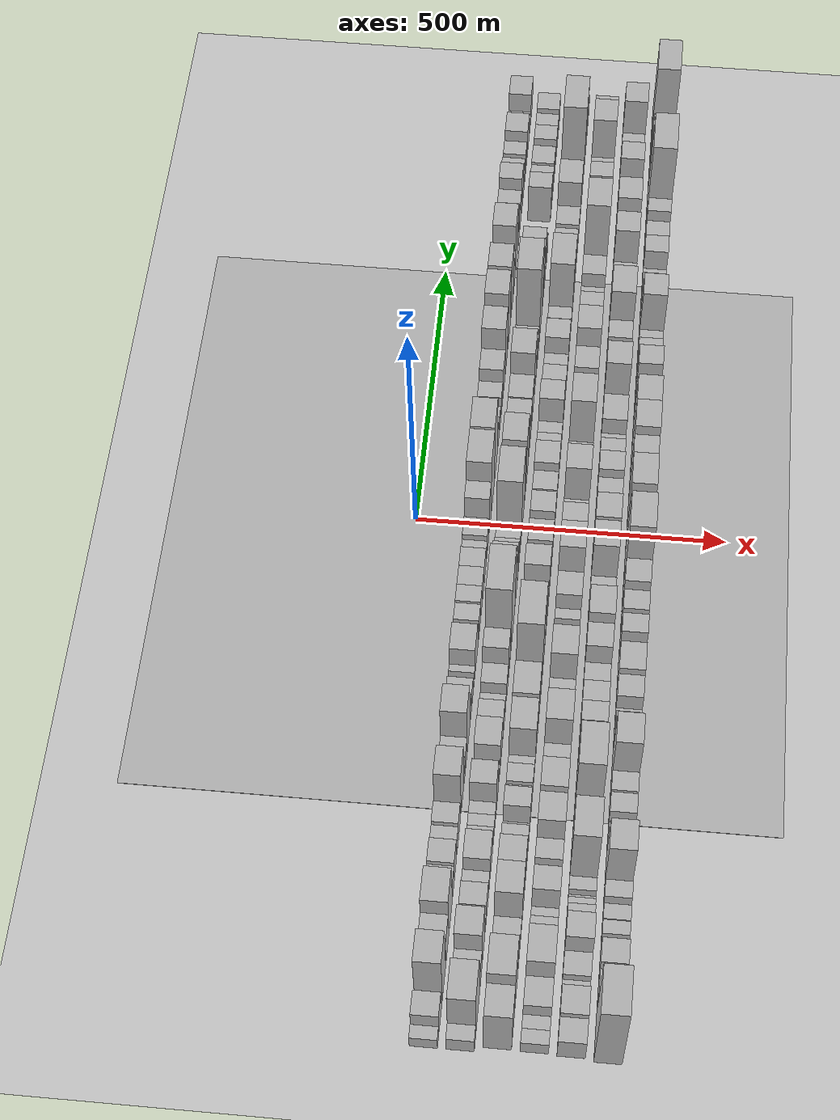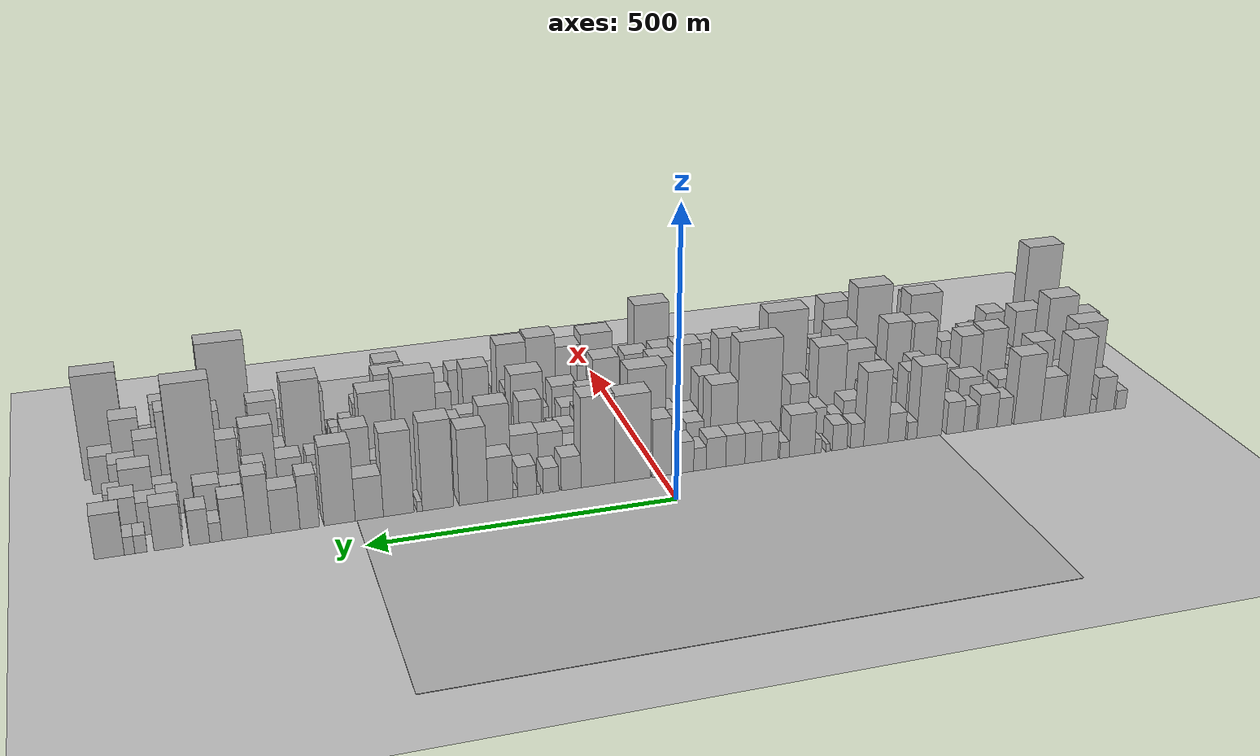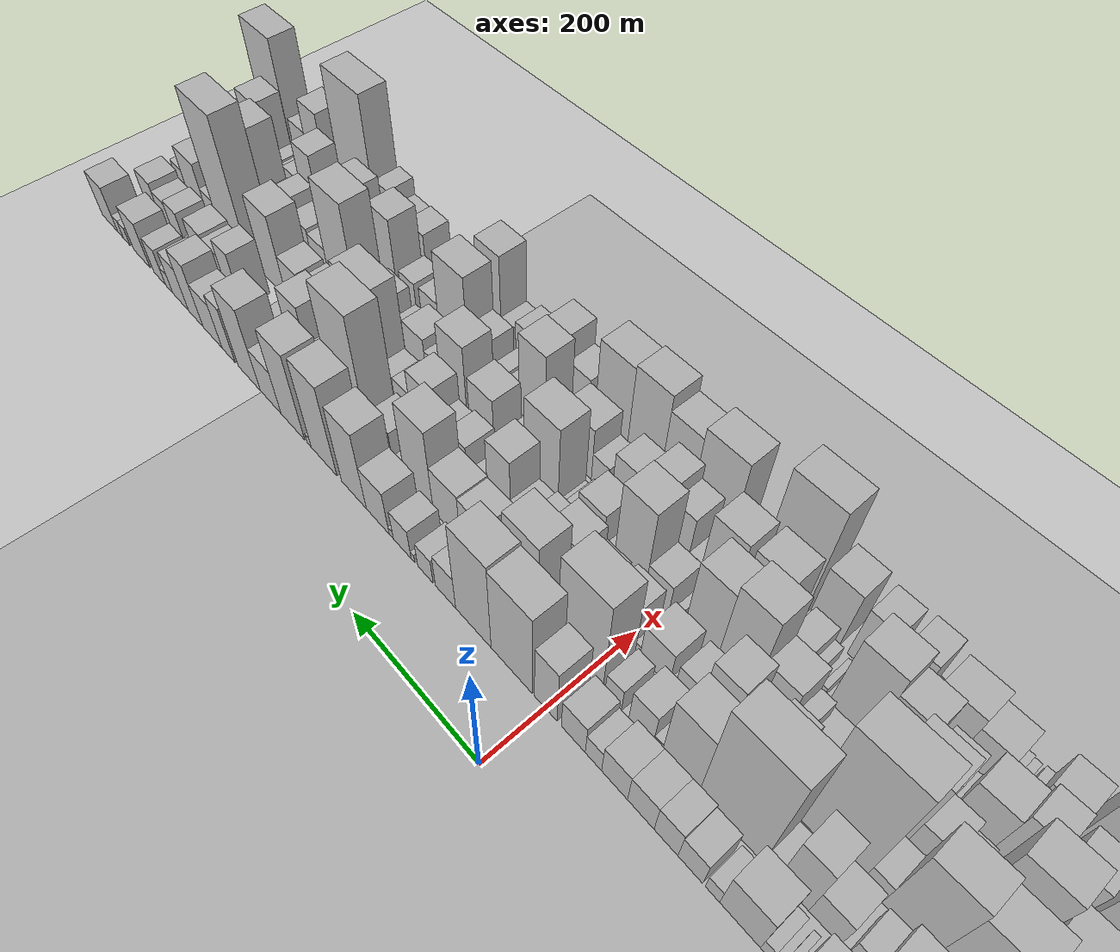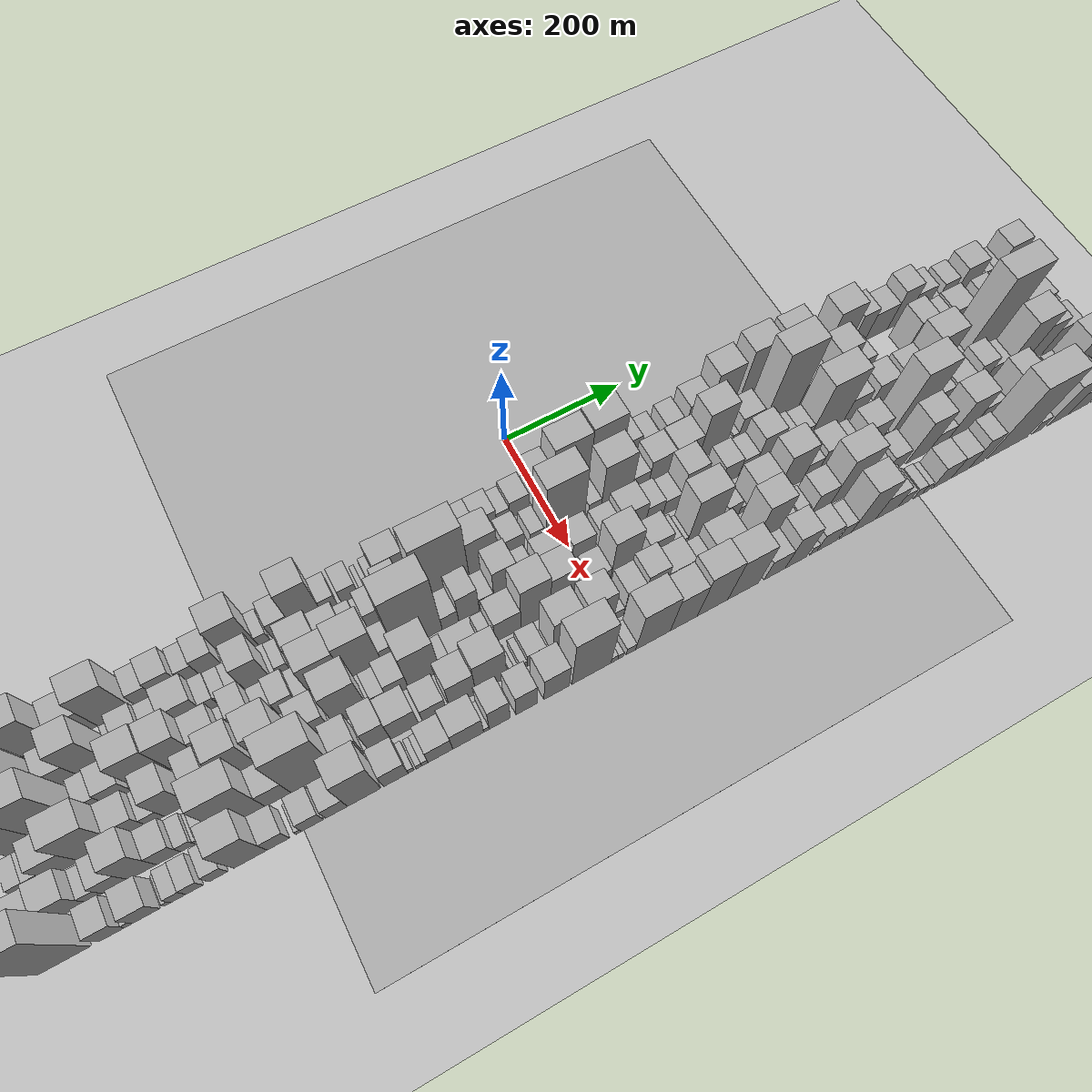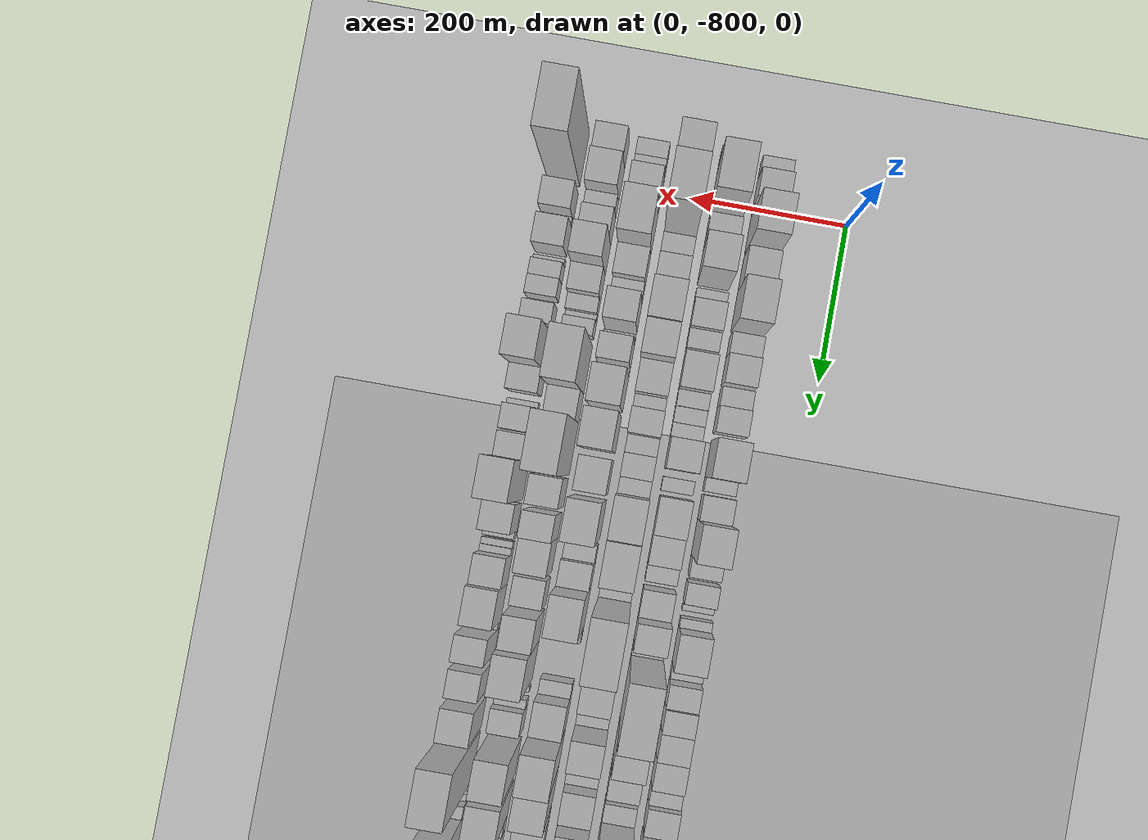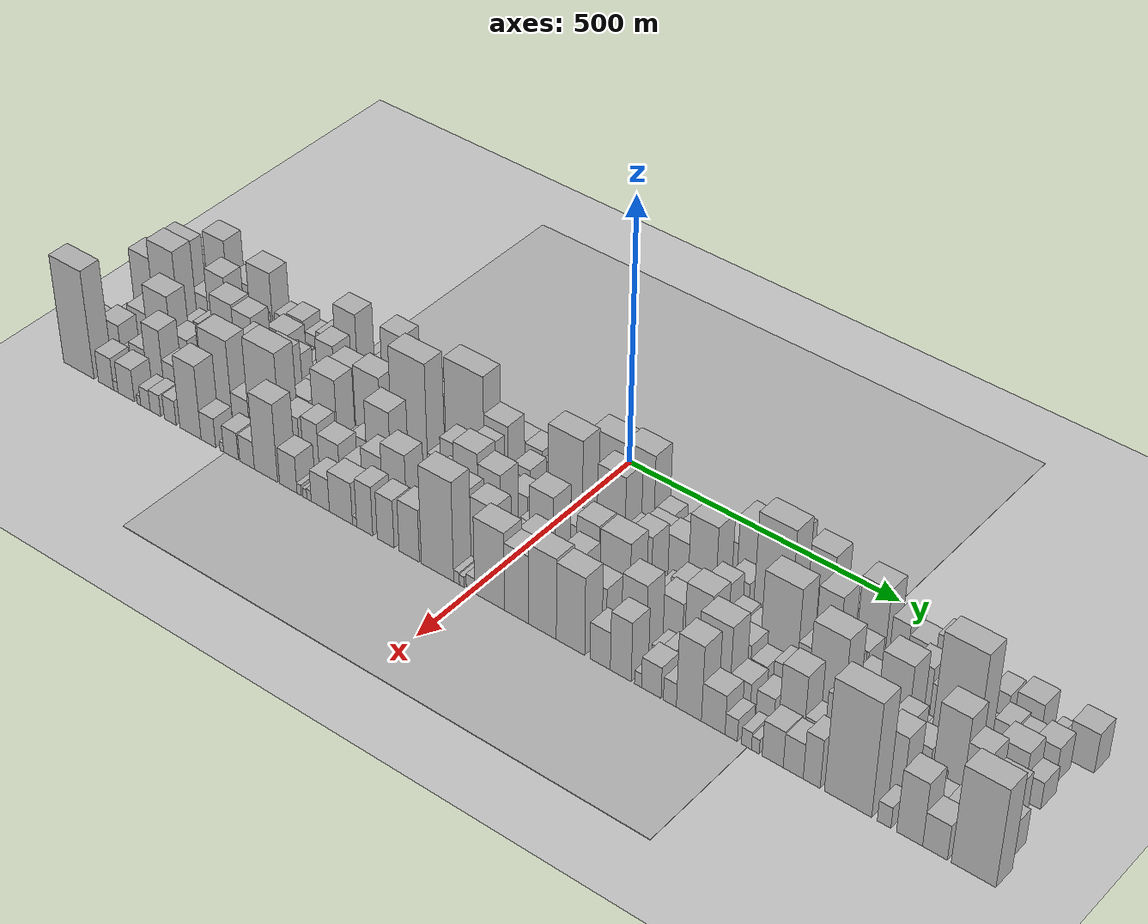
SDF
<?xml version="1.0" encoding="utf-8"?>

<sdf version="1.6">

   <world name="default">

      <gui fullscreen="0">

         <camera name="user_camera">

            <pose>-15 0 4.57585 0 0 0</pose>

            <view_controller>orbit</view_controller>

         </camera>

      </gui>

      <scene>

         <sky>

           <clouds>

             <speed>12</speed>

           </clouds>

         </sky>

         <ambient>0.4 0.4 0.4 1</ambient>

         <background>0.7 0.7 0.7 1</background>

         <shadows>1</shadows>

      </scene>

      <gravity>0 0 -9.8066</gravity>

      <magnetic_field>6e-06 2.3e-05 -4.2e-05</magnetic_field>

      <physics default="0" name="default_physics" type="ode">

         <ode>

            <solver>

               <type>quick</type>

               <iters>10</iters>

               <sor>1.0</sor>

               <use_dynamic_moi_rescaling>0</use_dynamic_moi_rescaling>

            </solver>

            <constraints>

               <cfm>0</cfm>

               <erp>0.2</erp>

               <contact_max_correcting_vel>100</contact_max_correcting_vel>

               <contact_surface_layer>0.001</contact_surface_layer>

            </constraints>

         </ode>

         <max_step_size>0.004</max_step_size>

         <real_time_factor>1</real_time_factor>

         <real_time_update_rate>250</real_time_update_rate>

      </physics>

      <light name="sun" type="directional">

         <cast_shadows>1</cast_shadows>

         <pose>0 0 10 0 0 0</pose>

         <diffuse>0.8 0.8 0.8 1</diffuse>

         <specular>0.2 0.2 0.2 1</specular>

         <attenuation>

            <range>1000</range>

            <constant>0.9</constant>

            <linear>0.01</linear>

            <quadratic>0.001</quadratic>

         </attenuation>

         <direction>-0.5 0.1 -0.9</direction>

      </light>

      <include>

         <name>ground_plane_1</name>

         <uri>model://HANNAS_ground_plane</uri>

         <pose>0 0 0  0 0 0</pose>

      </include>

      <include>

         <name>ground_plane_2</name>

         <uri>model://HANNAS_ground_plane</uri>

         <pose>100 0 0  0 0 0</pose>

      </include>

      <model name="building_1">

         <static>1</static>

         <pose frame="">100.0000 -850.1678 0 0.000000 0.000000 0.000000</pose>

         <link name="link">

            <pose frame="">0 0 18.00 0 0 0</pose>

            <collision name="collision">

               <geometry>

                  <box>

                     <size>40.0000 19.6644 36.0000</size>

                  </box>

               </geometry>

               <max_contacts>10</max_contacts>

               <surface>

                  <contact>

                     <ode/>

                  </contact>

                  <bounce/>

                  <friction>

                     <torsional>

                        <ode/>

                     </torsional>

                     <ode/>

                  </friction>

               </surface>

            </collision>

            <visual name="visual">

               <cast_shadows>0</cast_shadows>

               <geometry>

                  <box>

                     <size>40.0000 19.6644 36.0000</size>

                  </box>

               </geometry>

               <material>

                  <script>

                     <uri>model://HANNAS_wall/materials/scripts</uri>

                     <uri>model://HANNAS_wall/materials/textures</uri>

                     <name>vrc/HANNAS_wall</name>

                  </script>

               </material>

            </visual>

            <self_collide>0</self_collide>

            <enable_wind>0</enable_wind>

            <kinematic>0</kinematic>

         </link>

      </model>

      <model name="building_2">

         <static>1</static>

         <pose frame="">100.0000 -818.5363 0 0.000000 0.000000 0.000000</pose>

         <link name="link">

            <pose frame="">0 0 33.00 0 0 0</pose>

            <collision name="collision">

               <geometry>

                  <box>

                     <size>40.0000 35.5986 66.0000</size>

                  </box>

               </geometry>

               <max_contacts>10</max_contacts>

               <surface>

                  <contact>

                     <ode/>

                  </contact>

                  <bounce/>

                  <friction>

                     <torsional>

                        <ode/>

                     </torsional>

                     <ode/>

                  </friction>

               </surface>

            </collision>

            <visual name="visual">

               <cast_shadows>0</cast_shadows>

               <geometry>

                  <box>

                     <size>40.0000 35.5986 66.0000</size>

                  </box>

               </geometry>

               <material>

                  <script>

                     <uri>model://HANNAS_wall/materials/scripts</uri>

                     <uri>model://HANNAS_wall/materials/textures</uri>

                     <name>vrc/HANNAS_wall</name>

                  </script>

               </material>

            </visual>

            <self_collide>0</self_collide>

            <enable_wind>0</enable_wind>

            <kinematic>0</kinematic>

         </link>

      </model>

      <model name="building_3">

         <static>1</static>

         <pose frame="">100.0000 -794.4167 0 0.000000 0.000000 0.000000</pose>

         <link name="link">

            <pose frame="">0 0 13.50 0 0 0</pose>

            <collision name="collision">

               <geometry>

                  <box>

                     <size>40.0000 12.6405 27.0000</size>

                  </box>

               </geometry>

               <max_contacts>10</max_contacts>

               <surface>

                  <contact>

                     <ode/>

                  </contact>

                  <bounce/>

                  <friction>

                     <torsional>

                        <ode/>

                     </torsional>

                     <ode/>

                  </friction>

               </surface>

            </collision>

            <visual name="visual">

               <cast_shadows>0</cast_shadows>

               <geometry>

                  <box>

                     <size>40.0000 12.6405 27.0000</size>

                  </box>

               </geometry>

               <material>

                  <script>

                     <uri>model://HANNAS_wall/materials/scripts</uri>

                     <uri>model://HANNAS_wall/materials/textures</uri>

                     <name>vrc/HANNAS_wall</name>

                  </script>

               </material>

            </visual>

            <self_collide>0</self_collide>

            <enable_wind>0</enable_wind>

            <kinematic>0</kinematic>

         </link>

      </model>

      <model name="building_4">

         <static>1</static>

         <pose frame="">100.0000 -764.4303 0 0.000000 0.000000 0.000000</pose>

         <link name="link">

            <pose frame="">0 0 73.50 0 0 0</pose>

            <collision name="collision">

               <geometry>

                  <box>

                     <size>40.0000 47.3323 147.0000</size>

                  </box>

               </geometry>

               <max_contacts>10</max_contacts>

               <surface>

                  <contact>

                     <ode/>

                  </contact>

                  <bounce/>

                  <friction>

                     <torsional>

                        <ode/>

                     </torsional>

                     <ode/>

                  </friction>

               </surface>

            </collision>

            <visual name="visual">

               <cast_shadows>0</cast_shadows>

               <geometry>

                  <box>

                     <size>40.0000 47.3323 147.0000</size>

                  </box>

               </geometry>

               <material>

                  <script>

                     <uri>model://HANNAS_wall/materials/scripts</uri>

                     <uri>model://HANNAS_wall/materials/textures</uri>

                     <name>vrc/HANNAS_wall</name>

                  </script>

               </material>

            </visual>

            <self_collide>0</self_collide>

            <enable_wind>0</enable_wind>

            <kinematic>0</kinematic>

         </link>

      </model>

      <model name="building_5">

         <static>1</static>

         <pose frame="">100.0000 -714.7131 0 0.000000 0.000000 0.000000</pose>

         <link name="link">

            <pose frame="">0 0 40.50 0 0 0</pose>

            <collision name="collision">

               <geometry>

                  <box>

                     <size>40.0000 44.1021 81.0000</size>

                  </box>

               </geometry>

               <max_contacts>10</max_contacts>

               <surface>

                  <contact>

                     <ode/>

                  </contact>

                  <bounce/>

                  <friction>

                     <torsional>

                        <ode/>

                     </torsional>

                     <ode/>

                  </friction>

               </surface>

            </collision>

            <visual name="visual">

               <cast_shadows>0</cast_shadows>

               <geometry>

                  <box>

                     <size>40.0000 44.1021 81.0000</size>

                  </box>

               </geometry>

               <material>

                  <script>

                     <uri>model://HANNAS_wall/materials/scripts</uri>

                     <uri>model://HANNAS_wall/materials/textures</uri>

                     <name>vrc/HANNAS_wall</name>

                  </script>

               </material>

            </visual>

            <self_collide>0</self_collide>

            <enable_wind>0</enable_wind>

            <kinematic>0</kinematic>

         </link>

      </model>

      <model name="building_6">

         <static>1</static>

         <pose frame="">100.0000 -666.9803 0 0.000000 0.000000 0.000000</pose>

         <link name="link">

            <pose frame="">0 0 64.50 0 0 0</pose>

            <collision name="collision">

               <geometry>

                  <box>

                     <size>40.0000 51.3636 129.0000</size>

                  </box>

               </geometry>

               <max_contacts>10</max_contacts>

               <surface>

                  <contact>

                     <ode/>

                  </contact>

                  <bounce/>

                  <friction>

                     <torsional>

                        <ode/>

                     </torsional>

                     <ode/>

                  </friction>

               </surface>

            </collision>

            <visual name="visual">

               <cast_shadows>0</cast_shadows>

               <geometry>

                  <box>

                     <size>40.0000 51.3636 129.0000</size>

                  </box>

               </geometry>

               <material>

                  <script>

                     <uri>model://HANNAS_wall/materials/scripts</uri>

                     <uri>model://HANNAS_wall/materials/textures</uri>

                     <name>vrc/HANNAS_wall</name>

                  </script>

               </material>

            </visual>

            <self_collide>0</self_collide>

            <enable_wind>0</enable_wind>

            <kinematic>0</kinematic>

         </link>

      </model>

      <model name="building_7">

         <static>1</static>

         <pose frame="">100.0000 -622.5360 0 0.000000 0.000000 0.000000</pose>

         <link name="link">

            <pose frame="">0 0 27.00 0 0 0</pose>

            <collision name="collision">

               <geometry>

                  <box>

                     <size>40.0000 27.5249 54.0000</size>

                  </box>

               </geometry>

               <max_contacts>10</max_contacts>

               <surface>

                  <contact>

                     <ode/>

                  </contact>

                  <bounce/>

                  <friction>

                     <torsional>

                        <ode/>

                     </torsional>

                     <ode/>

                  </friction>

               </surface>

            </collision>

            <visual name="visual">

               <cast_shadows>0</cast_shadows>

               <geometry>

                  <box>

                     <size>40.0000 27.5249 54.0000</size>

                  </box>

               </geometry>

               <material>

                  <script>

                     <uri>model://HANNAS_wall/materials/scripts</uri>

                     <uri>model://HANNAS_wall/materials/textures</uri>

                     <name>vrc/HANNAS_wall</name>

                  </script>

               </material>

            </visual>

            <self_collide>0</self_collide>

            <enable_wind>0</enable_wind>

            <kinematic>0</kinematic>

         </link>

      </model>

      <model name="building_8">

         <static>1</static>

         <pose frame="">100.0000 -590.5916 0 0.000000 0.000000 0.000000</pose>

         <link name="link">

            <pose frame="">0 0 33.00 0 0 0</pose>

            <collision name="collision">

               <geometry>

                  <box>

                     <size>40.0000 36.3639 66.0000</size>

                  </box>

               </geometry>

               <max_contacts>10</max_contacts>

               <surface>

                  <contact>

                     <ode/>

                  </contact>

                  <bounce/>

                  <friction>

                     <torsional>

                        <ode/>

                     </torsional>

                     <ode/>

                  </friction>

               </surface>

            </collision>

            <visual name="visual">

               <cast_shadows>0</cast_shadows>

               <geometry>

                  <box>

                     <size>40.0000 36.3639 66.0000</size>

                  </box>

               </geometry>

               <material>

                  <script>

                     <uri>model://HANNAS_wall/materials/scripts</uri>

                     <uri>model://HANNAS_wall/materials/textures</uri>

                     <name>vrc/HANNAS_wall</name>

                  </script>

               </material>

            </visual>

            <self_collide>0</self_collide>

            <enable_wind>0</enable_wind>

            <kinematic>0</kinematic>

         </link>

      </model>

      <model name="building_9">

         <static>1</static>

         <pose frame="">100.0000 -557.1336 0 0.000000 0.000000 0.000000</pose>

         <link name="link">

            <pose frame="">0 0 24.00 0 0 0</pose>

            <collision name="collision">

               <geometry>

                  <box>

                     <size>40.0000 24.5523 48.0000</size>

                  </box>

               </geometry>

               <max_contacts>10</max_contacts>

               <surface>

                  <contact>

                     <ode/>

                  </contact>

                  <bounce/>

                  <friction>

                     <torsional>

                        <ode/>

                     </torsional>

                     <ode/>

                  </friction>

               </surface>

            </collision>

            <visual name="visual">

               <cast_shadows>0</cast_shadows>

               <geometry>

                  <box>

                     <size>40.0000 24.5523 48.0000</size>

                  </box>

               </geometry>

               <material>

                  <script>

                     <uri>model://HANNAS_wall/materials/scripts</uri>

                     <uri>model://HANNAS_wall/materials/textures</uri>

                     <name>vrc/HANNAS_wall</name>

                  </script>

               </material>

            </visual>

            <self_collide>0</self_collide>

            <enable_wind>0</enable_wind>

            <kinematic>0</kinematic>

         </link>

      </model>

      <model name="building_10">

         <static>1</static>

         <pose frame="">100.0000 -528.5953 0 0.000000 0.000000 0.000000</pose>

         <link name="link">

            <pose frame="">0 0 30.00 0 0 0</pose>

            <collision name="collision">

               <geometry>

                  <box>

                     <size>40.0000 32.5243 60.0000</size>

                  </box>

               </geometry>

               <max_contacts>10</max_contacts>

               <surface>

                  <contact>

                     <ode/>

                  </contact>

                  <bounce/>

                  <friction>

                     <torsional>

                        <ode/>

                     </torsional>

                     <ode/>

                  </friction>

               </surface>

            </collision>

            <visual name="visual">

               <cast_shadows>0</cast_shadows>

               <geometry>

                  <box>

                     <size>40.0000 32.5243 60.0000</size>

                  </box>

               </geometry>

               <material>

                  <script>

                     <uri>model://HANNAS_wall/materials/scripts</uri>

                     <uri>model://HANNAS_wall/materials/textures</uri>

                     <name>vrc/HANNAS_wall</name>

                  </script>

               </material>

            </visual>

            <self_collide>0</self_collide>

            <enable_wind>0</enable_wind>

            <kinematic>0</kinematic>

         </link>

      </model>

      <model name="building_11">

         <static>1</static>

         <pose frame="">100.0000 -480.1072 0 0.000000 0.000000 0.000000</pose>

         <link name="link">

            <pose frame="">0 0 67.50 0 0 0</pose>

            <collision name="collision">

               <geometry>

                  <box>

                     <size>40.0000 46.4518 135.0000</size>

                  </box>

               </geometry>

               <max_contacts>10</max_contacts>

               <surface>

                  <contact>

                     <ode/>

                  </contact>

                  <bounce/>

                  <friction>

                     <torsional>

                        <ode/>

                     </torsional>

                     <ode/>

                  </friction>

               </surface>

            </collision>

            <visual name="visual">

               <cast_shadows>0</cast_shadows>

               <geometry>

                  <box>

                     <size>40.0000 46.4518 135.0000</size>

                  </box>

               </geometry>

               <material>

                  <script>

                     <uri>model://HANNAS_wall/materials/scripts</uri>

                     <uri>model://HANNAS_wall/materials/textures</uri>

                     <name>vrc/HANNAS_wall</name>

                  </script>

               </material>

            </visual>

            <self_collide>0</self_collide>

            <enable_wind>0</enable_wind>

            <kinematic>0</kinematic>

         </link>

      </model>

      <model name="building_12">

         <static>1</static>

         <pose frame="">100.0000 -448.1927 0 0.000000 0.000000 0.000000</pose>

         <link name="link">

            <pose frame="">0 0 16.50 0 0 0</pose>

            <collision name="collision">

               <geometry>

                  <box>

                     <size>40.0000 17.3773 33.0000</size>

                  </box>

               </geometry>

               <max_contacts>10</max_contacts>

               <surface>

                  <contact>

                     <ode/>

                  </contact>

                  <bounce/>

                  <friction>

                     <torsional>

                        <ode/>

                     </torsional>

                     <ode/>

                  </friction>

               </surface>

            </collision>

            <visual name="visual">

               <cast_shadows>0</cast_shadows>

               <geometry>

                  <box>

                     <size>40.0000 17.3773 33.0000</size>

                  </box>

               </geometry>

               <material>

                  <script>

                     <uri>model://HANNAS_wall/materials/scripts</uri>

                     <uri>model://HANNAS_wall/materials/textures</uri>

                     <name>vrc/HANNAS_wall</name>

                  </script>

               </material>

            </visual>

            <self_collide>0</self_collide>

            <enable_wind>0</enable_wind>

            <kinematic>0</kinematic>

         </link>

      </model>

      <model name="building_13">

         <static>1</static>

         <pose frame="">100.0000 -419.7006 0 0.000000 0.000000 0.000000</pose>

         <link name="link">

            <pose frame="">0 0 27.00 0 0 0</pose>

            <collision name="collision">

               <geometry>

                  <box>

                     <size>40.0000 31.6068 54.0000</size>

                  </box>

               </geometry>

               <max_contacts>10</max_contacts>

               <surface>

                  <contact>

                     <ode/>

                  </contact>

                  <bounce/>

                  <friction>

                     <torsional>

                        <ode/>

                     </torsional>

                     <ode/>

                  </friction>

               </surface>

            </collision>

            <visual name="visual">

               <cast_shadows>0</cast_shadows>

               <geometry>

                  <box>

                     <size>40.0000 31.6068 54.0000</size>

                  </box>

               </geometry>

               <material>

                  <script>

                     <uri>model://HANNAS_wall/materials/scripts</uri>

                     <uri>model://HANNAS_wall/materials/textures</uri>

                     <name>vrc/HANNAS_wall</name>

                  </script>

               </material>

            </visual>

            <self_collide>0</self_collide>

            <enable_wind>0</enable_wind>

            <kinematic>0</kinematic>

         </link>

      </model>

      <model name="building_14">

         <static>1</static>

         <pose frame="">100.0000 -381.3172 0 0.000000 0.000000 0.000000</pose>

         <link name="link">

            <pose frame="">0 0 69.00 0 0 0</pose>

            <collision name="collision">

               <geometry>

                  <box>

                     <size>40.0000 45.1601 138.0000</size>

                  </box>

               </geometry>

               <max_contacts>10</max_contacts>

               <surface>

                  <contact>

                     <ode/>

                  </contact>

                  <bounce/>

                  <friction>

                     <torsional>

                        <ode/>

                     </torsional>

                     <ode/>

                  </friction>

               </surface>

            </collision>

            <visual name="visual">

               <cast_shadows>0</cast_shadows>

               <geometry>

                  <box>

                     <size>40.0000 45.1601 138.0000</size>

                  </box>

               </geometry>

               <material>

                  <script>

                     <uri>model://HANNAS_wall/materials/scripts</uri>

                     <uri>model://HANNAS_wall/materials/textures</uri>

                     <name>vrc/HANNAS_wall</name>

                  </script>

               </material>

            </visual>

            <self_collide>0</self_collide>

            <enable_wind>0</enable_wind>

            <kinematic>0</kinematic>

         </link>

      </model>

      <model name="building_15">

         <static>1</static>

         <pose frame="">100.0000 -346.4938 0 0.000000 0.000000 0.000000</pose>

         <link name="link">

            <pose frame="">0 0 22.50 0 0 0</pose>

            <collision name="collision">

               <geometry>

                  <box>

                     <size>40.0000 24.4866 45.0000</size>

                  </box>

               </geometry>

               <max_contacts>10</max_contacts>

               <surface>

                  <contact>

                     <ode/>

                  </contact>

                  <bounce/>

                  <friction>

                     <torsional>

                        <ode/>

                     </torsional>

                     <ode/>

                  </friction>

               </surface>

            </collision>

            <visual name="visual">

               <cast_shadows>0</cast_shadows>

               <geometry>

                  <box>

                     <size>40.0000 24.4866 45.0000</size>

                  </box>

               </geometry>

               <material>

                  <script>

                     <uri>model://HANNAS_wall/materials/scripts</uri>

                     <uri>model://HANNAS_wall/materials/textures</uri>

                     <name>vrc/HANNAS_wall</name>

                  </script>

               </material>

            </visual>

            <self_collide>0</self_collide>

            <enable_wind>0</enable_wind>

            <kinematic>0</kinematic>

         </link>

      </model>

      <model name="building_16">

         <static>1</static>

         <pose frame="">100.0000 -314.8308 0 0.000000 0.000000 0.000000</pose>

         <link name="link">

            <pose frame="">0 0 24.00 0 0 0</pose>

            <collision name="collision">

               <geometry>

                  <box>

                     <size>40.0000 26.8396 48.0000</size>

                  </box>

               </geometry>

               <max_contacts>10</max_contacts>

               <surface>

                  <contact>

                     <ode/>

                  </contact>

                  <bounce/>

                  <friction>

                     <torsional>

                        <ode/>

                     </torsional>

                     <ode/>

                  </friction>

               </surface>

            </collision>

            <visual name="visual">

               <cast_shadows>0</cast_shadows>

               <geometry>

                  <box>

                     <size>40.0000 26.8396 48.0000</size>

                  </box>

               </geometry>

               <material>

                  <script>

                     <uri>model://HANNAS_wall/materials/scripts</uri>

                     <uri>model://HANNAS_wall/materials/textures</uri>

                     <name>vrc/HANNAS_wall</name>

                  </script>

               </material>

            </visual>

            <self_collide>0</self_collide>

            <enable_wind>0</enable_wind>

            <kinematic>0</kinematic>

         </link>

      </model>

      <model name="building_17">

         <static>1</static>

         <pose frame="">100.0000 -293.7023 0 0.000000 0.000000 0.000000</pose>

         <link name="link">

            <pose frame="">0 0 7.50 0 0 0</pose>

            <collision name="collision">

               <geometry>

                  <box>

                     <size>40.0000 7.4174 15.0000</size>

                  </box>

               </geometry>

               <max_contacts>10</max_contacts>

               <surface>

                  <contact>

                     <ode/>

                  </contact>

                  <bounce/>

                  <friction>

                     <torsional>

                        <ode/>

                     </torsional>

                     <ode/>

                  </friction>

               </surface>

            </collision>

            <visual name="visual">

               <cast_shadows>0</cast_shadows>

               <geometry>

                  <box>

                     <size>40.0000 7.4174 15.0000</size>

                  </box>

               </geometry>

               <material>

                  <script>

                     <uri>model://HANNAS_wall/materials/scripts</uri>

                     <uri>model://HANNAS_wall/materials/textures</uri>

                     <name>vrc/HANNAS_wall</name>

                  </script>

               </material>

            </visual>

            <self_collide>0</self_collide>

            <enable_wind>0</enable_wind>

            <kinematic>0</kinematic>

         </link>

      </model>

      <model name="building_18">

         <static>1</static>

         <pose frame="">100.0000 -275.9032 0 0.000000 0.000000 0.000000</pose>

         <link name="link">

            <pose frame="">0 0 13.50 0 0 0</pose>

            <collision name="collision">

               <geometry>

                  <box>

                     <size>40.0000 12.1808 27.0000</size>

                  </box>

               </geometry>

               <max_contacts>10</max_contacts>

               <surface>

                  <contact>

                     <ode/>

                  </contact>

                  <bounce/>

                  <friction>

                     <torsional>

                        <ode/>

                     </torsional>

                     <ode/>

                  </friction>

               </surface>

            </collision>

            <visual name="visual">

               <cast_shadows>0</cast_shadows>

               <geometry>

                  <box>

                     <size>40.0000 12.1808 27.0000</size>

                  </box>

               </geometry>

               <material>

                  <script>

                     <uri>model://HANNAS_wall/materials/scripts</uri>

                     <uri>model://HANNAS_wall/materials/textures</uri>

                     <name>vrc/HANNAS_wall</name>

                  </script>

               </material>

            </visual>

            <self_collide>0</self_collide>

            <enable_wind>0</enable_wind>

            <kinematic>0</kinematic>

         </link>

      </model>

      <model name="building_19">

         <static>1</static>

         <pose frame="">100.0000 -246.8613 0 0.000000 0.000000 0.000000</pose>

         <link name="link">

            <pose frame="">0 0 39.00 0 0 0</pose>

            <collision name="collision">

               <geometry>

                  <box>

                     <size>40.0000 45.9031 78.0000</size>

                  </box>

               </geometry>

               <max_contacts>10</max_contacts>

               <surface>

                  <contact>

                     <ode/>

                  </contact>

                  <bounce/>

                  <friction>

                     <torsional>

                        <ode/>

                     </torsional>

                     <ode/>

                  </friction>

               </surface>

            </collision>

            <visual name="visual">

               <cast_shadows>0</cast_shadows>

               <geometry>

                  <box>

                     <size>40.0000 45.9031 78.0000</size>

                  </box>

               </geometry>

               <material>

                  <script>

                     <uri>model://HANNAS_wall/materials/scripts</uri>

                     <uri>model://HANNAS_wall/materials/textures</uri>

                     <name>vrc/HANNAS_wall</name>

                  </script>

               </material>

            </visual>

            <self_collide>0</self_collide>

            <enable_wind>0</enable_wind>

            <kinematic>0</kinematic>

         </link>

      </model>

      <model name="building_20">

         <static>1</static>

         <pose frame="">100.0000 -215.5407 0 0.000000 0.000000 0.000000</pose>

         <link name="link">

            <pose frame="">0 0 15.00 0 0 0</pose>

            <collision name="collision">

               <geometry>

                  <box>

                     <size>40.0000 16.7380 30.0000</size>

                  </box>

               </geometry>

               <max_contacts>10</max_contacts>

               <surface>

                  <contact>

                     <ode/>

                  </contact>

                  <bounce/>

                  <friction>

                     <torsional>

                        <ode/>

                     </torsional>

                     <ode/>

                  </friction>

               </surface>

            </collision>

            <visual name="visual">

               <cast_shadows>0</cast_shadows>

               <geometry>

                  <box>

                     <size>40.0000 16.7380 30.0000</size>

                  </box>

               </geometry>

               <material>

                  <script>

                     <uri>model://HANNAS_wall/materials/scripts</uri>

                     <uri>model://HANNAS_wall/materials/textures</uri>

                     <name>vrc/HANNAS_wall</name>

                  </script>

               </material>

            </visual>

            <self_collide>0</self_collide>

            <enable_wind>0</enable_wind>

            <kinematic>0</kinematic>

         </link>

      </model>

      <model name="building_21">

         <static>1</static>

         <pose frame="">100.0000 -189.4003 0 0.000000 0.000000 0.000000</pose>

         <link name="link">

            <pose frame="">0 0 25.50 0 0 0</pose>

            <collision name="collision">

               <geometry>

                  <box>

                     <size>40.0000 29.5428 51.0000</size>

                  </box>

               </geometry>

               <max_contacts>10</max_contacts>

               <surface>

                  <contact>

                     <ode/>

                  </contact>

                  <bounce/>

                  <friction>

                     <torsional>

                        <ode/>

                     </torsional>

                     <ode/>

                  </friction>

               </surface>

            </collision>

            <visual name="visual">

               <cast_shadows>0</cast_shadows>

               <geometry>

                  <box>

                     <size>40.0000 29.5428 51.0000</size>

                  </box>

               </geometry>

               <material>

                  <script>

                     <uri>model://HANNAS_wall/materials/scripts</uri>

                     <uri>model://HANNAS_wall/materials/textures</uri>

                     <name>vrc/HANNAS_wall</name>

                  </script>

               </material>

            </visual>

            <self_collide>0</self_collide>

            <enable_wind>0</enable_wind>

            <kinematic>0</kinematic>

         </link>

      </model>

      <model name="building_22">

         <static>1</static>

         <pose frame="">100.0000 -159.9750 0 0.000000 0.000000 0.000000</pose>

         <link name="link">

            <pose frame="">0 0 28.50 0 0 0</pose>

            <collision name="collision">

               <geometry>

                  <box>

                     <size>40.0000 29.3079 57.0000</size>

                  </box>

               </geometry>

               <max_contacts>10</max_contacts>

               <surface>

                  <contact>

                     <ode/>

                  </contact>

                  <bounce/>

                  <friction>

                     <torsional>

                        <ode/>

                     </torsional>

                     <ode/>

                  </friction>

               </surface>

            </collision>

            <visual name="visual">

               <cast_shadows>0</cast_shadows>

               <geometry>

                  <box>

                     <size>40.0000 29.3079 57.0000</size>

                  </box>

               </geometry>

               <material>

                  <script>

                     <uri>model://HANNAS_wall/materials/scripts</uri>

                     <uri>model://HANNAS_wall/materials/textures</uri>

                     <name>vrc/HANNAS_wall</name>

                  </script>

               </material>

            </visual>

            <self_collide>0</self_collide>

            <enable_wind>0</enable_wind>

            <kinematic>0</kinematic>

         </link>

      </model>

      <model name="building_23">

         <static>1</static>

         <pose frame="">100.0000 -128.4141 0 0.000000 0.000000 0.000000</pose>

         <link name="link">

            <pose frame="">0 0 28.50 0 0 0</pose>

            <collision name="collision">

               <geometry>

                  <box>

                     <size>40.0000 33.8138 57.0000</size>

                  </box>

               </geometry>

               <max_contacts>10</max_contacts>

               <surface>

                  <contact>

                     <ode/>

                  </contact>

                  <bounce/>

                  <friction>

                     <torsional>

                        <ode/>

                     </torsional>

                     <ode/>

                  </friction>

               </surface>

            </collision>

            <visual name="visual">

               <cast_shadows>0</cast_shadows>

               <geometry>

                  <box>

                     <size>40.0000 33.8138 57.0000</size>

                  </box>

               </geometry>

               <material>

                  <script>

                     <uri>model://HANNAS_wall/materials/scripts</uri>

                     <uri>model://HANNAS_wall/materials/textures</uri>

                     <name>vrc/HANNAS_wall</name>

                  </script>

               </material>

            </visual>

            <self_collide>0</self_collide>

            <enable_wind>0</enable_wind>

            <kinematic>0</kinematic>

         </link>

      </model>

      <model name="building_24">

         <static>1</static>

         <pose frame="">100.0000 -94.5212 0 0.000000 0.000000 0.000000</pose>

         <link name="link">

            <pose frame="">0 0 28.50 0 0 0</pose>

            <collision name="collision">

               <geometry>

                  <box>

                     <size>40.0000 33.9721 57.0000</size>

                  </box>

               </geometry>

               <max_contacts>10</max_contacts>

               <surface>

                  <contact>

                     <ode/>

                  </contact>

                  <bounce/>

                  <friction>

                     <torsional>

                        <ode/>

                     </torsional>

                     <ode/>

                  </friction>

               </surface>

            </collision>

            <visual name="visual">

               <cast_shadows>0</cast_shadows>

               <geometry>

                  <box>

                     <size>40.0000 33.9721 57.0000</size>

                  </box>

               </geometry>

               <material>

                  <script>

                     <uri>model://HANNAS_wall/materials/scripts</uri>

                     <uri>model://HANNAS_wall/materials/textures</uri>

                     <name>vrc/HANNAS_wall</name>

                  </script>

               </material>

            </visual>

            <self_collide>0</self_collide>

            <enable_wind>0</enable_wind>

            <kinematic>0</kinematic>

         </link>

      </model>

      <model name="building_25">

         <static>1</static>

         <pose frame="">100.0000 -66.5275 0 0.000000 0.000000 0.000000</pose>

         <link name="link">

            <pose frame="">0 0 21.00 0 0 0</pose>

            <collision name="collision">

               <geometry>

                  <box>

                     <size>40.0000 22.0153 42.0000</size>

                  </box>

               </geometry>

               <max_contacts>10</max_contacts>

               <surface>

                  <contact>

                     <ode/>

                  </contact>

                  <bounce/>

                  <friction>

                     <torsional>

                        <ode/>

                     </torsional>

                     <ode/>

                  </friction>

               </surface>

            </collision>

            <visual name="visual">

               <cast_shadows>0</cast_shadows>

               <geometry>

                  <box>

                     <size>40.0000 22.0153 42.0000</size>

                  </box>

               </geometry>

               <material>

                  <script>

                     <uri>model://HANNAS_wall/materials/scripts</uri>

                     <uri>model://HANNAS_wall/materials/textures</uri>

                     <name>vrc/HANNAS_wall</name>

                  </script>

               </material>

            </visual>

            <self_collide>0</self_collide>

            <enable_wind>0</enable_wind>

            <kinematic>0</kinematic>

         </link>

      </model>

      <model name="building_26">

         <static>1</static>

         <pose frame="">100.0000 -39.0222 0 0.000000 0.000000 0.000000</pose>

         <link name="link">

            <pose frame="">0 0 28.50 0 0 0</pose>

            <collision name="collision">

               <geometry>

                  <box>

                     <size>40.0000 32.9953 57.0000</size>

                  </box>

               </geometry>

               <max_contacts>10</max_contacts>

               <surface>

                  <contact>

                     <ode/>

                  </contact>

                  <bounce/>

                  <friction>

                     <torsional>

                        <ode/>

                     </torsional>

                     <ode/>

                  </friction>

               </surface>

            </collision>

            <visual name="visual">

               <cast_shadows>0</cast_shadows>

               <geometry>

                  <box>

                     <size>40.0000 32.9953 57.0000</size>

                  </box>

               </geometry>

               <material>

                  <script>

                     <uri>model://HANNAS_wall/materials/scripts</uri>

                     <uri>model://HANNAS_wall/materials/textures</uri>

                     <name>vrc/HANNAS_wall</name>

                  </script>

               </material>

            </visual>

            <self_collide>0</self_collide>

            <enable_wind>0</enable_wind>

            <kinematic>0</kinematic>

         </link>

      </model>

      <model name="building_27">

         <static>1</static>

         <pose frame="">100.0000 -0.3385 0 0.000000 0.000000 0.000000</pose>

         <link name="link">

            <pose frame="">0 0 52.50 0 0 0</pose>

            <collision name="collision">

               <geometry>

                  <box>

                     <size>40.0000 32.3721 105.0000</size>

                  </box>

               </geometry>

               <max_contacts>10</max_contacts>

               <surface>

                  <contact>

                     <ode/>

                  </contact>

                  <bounce/>

                  <friction>

                     <torsional>

                        <ode/>

                     </torsional>

                     <ode/>

                  </friction>

               </surface>

            </collision>

            <visual name="visual">

               <cast_shadows>0</cast_shadows>

               <geometry>

                  <box>

                     <size>40.0000 32.3721 105.0000</size>

                  </box>

               </geometry>

               <material>

                  <script>

                     <uri>model://HANNAS_wall/materials/scripts</uri>

                     <uri>model://HANNAS_wall/materials/textures</uri>

                     <name>vrc/HANNAS_wall</name>

                  </script>

               </material>

            </visual>

            <self_collide>0</self_collide>

            <enable_wind>0</enable_wind>

            <kinematic>0</kinematic>

         </link>

      </model>

      <model name="building_28">

         <static>1</static>

         <pose frame="">100.0000 49.6720 0 0.000000 0.000000 0.000000</pose>

         <link name="link">

            <pose frame="">0 0 78.00 0 0 0</pose>

            <collision name="collision">

               <geometry>

                  <box>

                     <size>40.0000 61.6490 156.0000</size>

                  </box>

               </geometry>

               <max_contacts>10</max_contacts>

               <surface>

                  <contact>

                     <ode/>

                  </contact>

                  <bounce/>

                  <friction>

                     <torsional>

                        <ode/>

                     </torsional>

                     <ode/>

                  </friction>

               </surface>

            </collision>

            <visual name="visual">

               <cast_shadows>0</cast_shadows>

               <geometry>

                  <box>

                     <size>40.0000 61.6490 156.0000</size>

                  </box>

               </geometry>

               <material>

                  <script>

                     <uri>model://HANNAS_wall/materials/scripts</uri>

                     <uri>model://HANNAS_wall/materials/textures</uri>

                     <name>vrc/HANNAS_wall</name>

                  </script>

               </material>

            </visual>

            <self_collide>0</self_collide>

            <enable_wind>0</enable_wind>

            <kinematic>0</kinematic>

         </link>

      </model>

      <model name="building_29">

         <static>1</static>

         <pose frame="">100.0000 108.5790 0 0.000000 0.000000 0.000000</pose>

         <link name="link">

            <pose frame="">0 0 81.00 0 0 0</pose>

            <collision name="collision">

               <geometry>

                  <box>

                     <size>40.0000 56.1650 162.0000</size>

                  </box>

               </geometry>

               <max_contacts>10</max_contacts>

               <surface>

                  <contact>

                     <ode/>

                  </contact>

                  <bounce/>

                  <friction>

                     <torsional>

                        <ode/>

                     </torsional>

                     <ode/>

                  </friction>

               </surface>

            </collision>

            <visual name="visual">

               <cast_shadows>0</cast_shadows>

               <geometry>

                  <box>

                     <size>40.0000 56.1650 162.0000</size>

                  </box>

               </geometry>

               <material>

                  <script>

                     <uri>model://HANNAS_wall/materials/scripts</uri>

                     <uri>model://HANNAS_wall/materials/textures</uri>

                     <name>vrc/HANNAS_wall</name>

                  </script>

               </material>

            </visual>

            <self_collide>0</self_collide>

            <enable_wind>0</enable_wind>

            <kinematic>0</kinematic>

         </link>

      </model>

      <model name="building_30">

         <static>1</static>

         <pose frame="">100.0000 153.1803 0 0.000000 0.000000 0.000000</pose>

         <link name="link">

            <pose frame="">0 0 30.00 0 0 0</pose>

            <collision name="collision">

               <geometry>

                  <box>

                     <size>40.0000 33.0377 60.0000</size>

                  </box>

               </geometry>

               <max_contacts>10</max_contacts>

               <surface>

                  <contact>

                     <ode/>

                  </contact>

                  <bounce/>

                  <friction>

                     <torsional>

                        <ode/>

                     </torsional>

                     <ode/>

                  </friction>

               </surface>

            </collision>

            <visual name="visual">

               <cast_shadows>0</cast_shadows>

               <geometry>

                  <box>

                     <size>40.0000 33.0377 60.0000</size>

                  </box>

               </geometry>

               <material>

                  <script>

                     <uri>model://HANNAS_wall/materials/scripts</uri>

                     <uri>model://HANNAS_wall/materials/textures</uri>

                     <name>vrc/HANNAS_wall</name>

                  </script>

               </material>

            </visual>

            <self_collide>0</self_collide>

            <enable_wind>0</enable_wind>

            <kinematic>0</kinematic>

         </link>

      </model>

      <model name="building_31">

         <static>1</static>

         <pose frame="">100.0000 186.6412 0 0.000000 0.000000 0.000000</pose>

         <link name="link">

            <pose frame="">0 0 22.50 0 0 0</pose>

            <collision name="collision">

               <geometry>

                  <box>

                     <size>40.0000 25.8840 45.0000</size>

                  </box>

               </geometry>

               <max_contacts>10</max_contacts>

               <surface>

                  <contact>

                     <ode/>

                  </contact>

                  <bounce/>

                  <friction>

                     <torsional>

                        <ode/>

                     </torsional>

                     <ode/>

                  </friction>

               </surface>

            </collision>

            <visual name="visual">

               <cast_shadows>0</cast_shadows>

               <geometry>

                  <box>

                     <size>40.0000 25.8840 45.0000</size>

                  </box>

               </geometry>

               <material>

                  <script>

                     <uri>model://HANNAS_wall/materials/scripts</uri>

                     <uri>model://HANNAS_wall/materials/textures</uri>

                     <name>vrc/HANNAS_wall</name>

                  </script>

               </material>

            </visual>

            <self_collide>0</self_collide>

            <enable_wind>0</enable_wind>

            <kinematic>0</kinematic>

         </link>

      </model>

      <model name="building_32">

         <static>1</static>

         <pose frame="">100.0000 207.7206 0 0.000000 0.000000 0.000000</pose>

         <link name="link">

            <pose frame="">0 0 7.50 0 0 0</pose>

            <collision name="collision">

               <geometry>

                  <box>

                     <size>40.0000 6.2748 15.0000</size>

                  </box>

               </geometry>

               <max_contacts>10</max_contacts>

               <surface>

                  <contact>

                     <ode/>

                  </contact>

                  <bounce/>

                  <friction>

                     <torsional>

                        <ode/>

                     </torsional>

                     <ode/>

                  </friction>

               </surface>

            </collision>

            <visual name="visual">

               <cast_shadows>0</cast_shadows>

               <geometry>

                  <box>

                     <size>40.0000 6.2748 15.0000</size>

                  </box>

               </geometry>

               <material>

                  <script>

                     <uri>model://HANNAS_wall/materials/scripts</uri>

                     <uri>model://HANNAS_wall/materials/textures</uri>

                     <name>vrc/HANNAS_wall</name>

                  </script>

               </material>

            </visual>

            <self_collide>0</self_collide>

            <enable_wind>0</enable_wind>

            <kinematic>0</kinematic>

         </link>

      </model>

      <model name="building_33">

         <static>1</static>

         <pose frame="">100.0000 226.3824 0 0.000000 0.000000 0.000000</pose>

         <link name="link">

            <pose frame="">0 0 27.00 0 0 0</pose>

            <collision name="collision">

               <geometry>

                  <box>

                     <size>40.0000 31.0487 54.0000</size>

                  </box>

               </geometry>

               <max_contacts>10</max_contacts>

               <surface>

                  <contact>

                     <ode/>

                  </contact>

                  <bounce/>

                  <friction>

                     <torsional>

                        <ode/>

                     </torsional>

                     <ode/>

                  </friction>

               </surface>

            </collision>

            <visual name="visual">

               <cast_shadows>0</cast_shadows>

               <geometry>

                  <box>

                     <size>40.0000 31.0487 54.0000</size>

                  </box>

               </geometry>

               <material>

                  <script>

                     <uri>model://HANNAS_wall/materials/scripts</uri>

                     <uri>model://HANNAS_wall/materials/textures</uri>

                     <name>vrc/HANNAS_wall</name>

                  </script>

               </material>

            </visual>

            <self_collide>0</self_collide>

            <enable_wind>0</enable_wind>

            <kinematic>0</kinematic>

         </link>

      </model>

      <model name="building_34">

         <static>1</static>

         <pose frame="">100.0000 245.6248 0 0.000000 0.000000 0.000000</pose>

         <link name="link">

            <pose frame="">0 0 7.50 0 0 0</pose>

            <collision name="collision">

               <geometry>

                  <box>

                     <size>40.0000 7.4362 15.0000</size>

                  </box>

               </geometry>

               <max_contacts>10</max_contacts>

               <surface>

                  <contact>

                     <ode/>

                  </contact>

                  <bounce/>

                  <friction>

                     <torsional>

                        <ode/>

                     </torsional>

                     <ode/>

                  </friction>

               </surface>

            </collision>

            <visual name="visual">

               <cast_shadows>0</cast_shadows>

               <geometry>

                  <box>

                     <size>40.0000 7.4362 15.0000</size>

                  </box>

               </geometry>

               <material>

                  <script>

                     <uri>model://HANNAS_wall/materials/scripts</uri>

                     <uri>model://HANNAS_wall/materials/textures</uri>

                     <name>vrc/HANNAS_wall</name>

                  </script>

               </material>

            </visual>

            <self_collide>0</self_collide>

            <enable_wind>0</enable_wind>

            <kinematic>0</kinematic>

         </link>

      </model>

      <model name="building_35">

         <static>1</static>

         <pose frame="">100.0000 269.9662 0 0.000000 0.000000 0.000000</pose>

         <link name="link">

            <pose frame="">0 0 39.00 0 0 0</pose>

            <collision name="collision">

               <geometry>

                  <box>

                     <size>40.0000 41.2466 78.0000</size>

                  </box>

               </geometry>

               <max_contacts>10</max_contacts>

               <surface>

                  <contact>

                     <ode/>

                  </contact>

                  <bounce/>

                  <friction>

                     <torsional>

                        <ode/>

                     </torsional>

                     <ode/>

                  </friction>

               </surface>

            </collision>

            <visual name="visual">

               <cast_shadows>0</cast_shadows>

               <geometry>

                  <box>

                     <size>40.0000 41.2466 78.0000</size>

                  </box>

               </geometry>

               <material>

                  <script>

                     <uri>model://HANNAS_wall/materials/scripts</uri>

                     <uri>model://HANNAS_wall/materials/textures</uri>

                     <name>vrc/HANNAS_wall</name>

                  </script>

               </material>

            </visual>

            <self_collide>0</self_collide>

            <enable_wind>0</enable_wind>

            <kinematic>0</kinematic>

         </link>

      </model>

      <model name="building_36">

         <static>1</static>

         <pose frame="">100.0000 313.8307 0 0.000000 0.000000 0.000000</pose>

         <link name="link">

            <pose frame="">0 0 67.50 0 0 0</pose>

            <collision name="collision">

               <geometry>

                  <box>

                     <size>40.0000 46.4823 135.0000</size>

                  </box>

               </geometry>

               <max_contacts>10</max_contacts>

               <surface>

                  <contact>

                     <ode/>

                  </contact>

                  <bounce/>

                  <friction>

                     <torsional>

                        <ode/>

                     </torsional>

                     <ode/>

                  </friction>

               </surface>

            </collision>

            <visual name="visual">

               <cast_shadows>0</cast_shadows>

               <geometry>

                  <box>

                     <size>40.0000 46.4823 135.0000</size>

                  </box>

               </geometry>

               <material>

                  <script>

                     <uri>model://HANNAS_wall/materials/scripts</uri>

                     <uri>model://HANNAS_wall/materials/textures</uri>

                     <name>vrc/HANNAS_wall</name>

                  </script>

               </material>

            </visual>

            <self_collide>0</self_collide>

            <enable_wind>0</enable_wind>

            <kinematic>0</kinematic>

         </link>

      </model>

      <model name="building_37">

         <static>1</static>

         <pose frame="">100.0000 371.2891 0 0.000000 0.000000 0.000000</pose>

         <link name="link">

            <pose frame="">0 0 78.00 0 0 0</pose>

            <collision name="collision">

               <geometry>

                  <box>

                     <size>40.0000 50.4343 156.0000</size>

                  </box>

               </geometry>

               <max_contacts>10</max_contacts>

               <surface>

                  <contact>

                     <ode/>

                  </contact>

                  <bounce/>

                  <friction>

                     <torsional>

                        <ode/>

                     </torsional>

                     <ode/>

                  </friction>

               </surface>

            </collision>

            <visual name="visual">

               <cast_shadows>0</cast_shadows>

               <geometry>

                  <box>

                     <size>40.0000 50.4343 156.0000</size>

                  </box>

               </geometry>

               <material>

                  <script>

                     <uri>model://HANNAS_wall/materials/scripts</uri>

                     <uri>model://HANNAS_wall/materials/textures</uri>

                     <name>vrc/HANNAS_wall</name>

                  </script>

               </material>

            </visual>

            <self_collide>0</self_collide>

            <enable_wind>0</enable_wind>

            <kinematic>0</kinematic>

         </link>

      </model>

      <model name="building_38">

         <static>1</static>

         <pose frame="">100.0000 400.6374 0 0.000000 0.000000 0.000000</pose>

         <link name="link">

            <pose frame="">0 0 9.00 0 0 0</pose>

            <collision name="collision">

               <geometry>

                  <box>

                     <size>40.0000 8.2623 18.0000</size>

                  </box>

               </geometry>

               <max_contacts>10</max_contacts>

               <surface>

                  <contact>

                     <ode/>

                  </contact>

                  <bounce/>

                  <friction>

                     <torsional>

                        <ode/>

                     </torsional>

                     <ode/>

                  </friction>

               </surface>

            </collision>

            <visual name="visual">

               <cast_shadows>0</cast_shadows>

               <geometry>

                  <box>

                     <size>40.0000 8.2623 18.0000</size>

                  </box>

               </geometry>

               <material>

                  <script>

                     <uri>model://HANNAS_wall/materials/scripts</uri>

                     <uri>model://HANNAS_wall/materials/textures</uri>

                     <name>vrc/HANNAS_wall</name>

                  </script>

               </material>

            </visual>

            <self_collide>0</self_collide>

            <enable_wind>0</enable_wind>

            <kinematic>0</kinematic>

         </link>

      </model>

      <model name="building_39">

         <static>1</static>

         <pose frame="">100.0000 434.0452 0 0.000000 0.000000 0.000000</pose>

         <link name="link">

            <pose frame="">0 0 73.50 0 0 0</pose>

            <collision name="collision">

               <geometry>

                  <box>

                     <size>40.0000 48.5534 147.0000</size>

                  </box>

               </geometry>

               <max_contacts>10</max_contacts>

               <surface>

                  <contact>

                     <ode/>

                  </contact>

                  <bounce/>

                  <friction>

                     <torsional>

                        <ode/>

                     </torsional>

                     <ode/>

                  </friction>

               </surface>

            </collision>

            <visual name="visual">

               <cast_shadows>0</cast_shadows>

               <geometry>

                  <box>

                     <size>40.0000 48.5534 147.0000</size>

                  </box>

               </geometry>

               <material>

                  <script>

                     <uri>model://HANNAS_wall/materials/scripts</uri>

                     <uri>model://HANNAS_wall/materials/textures</uri>

                     <name>vrc/HANNAS_wall</name>

                  </script>

               </material>

            </visual>

            <self_collide>0</self_collide>

            <enable_wind>0</enable_wind>

            <kinematic>0</kinematic>

         </link>

      </model>

      <model name="building_40">

         <static>1</static>

         <pose frame="">100.0000 480.4827 0 0.000000 0.000000 0.000000</pose>

         <link name="link">

            <pose frame="">0 0 37.50 0 0 0</pose>

            <collision name="collision">

               <geometry>

                  <box>

                     <size>40.0000 44.3215 75.0000</size>

                  </box>

               </geometry>

               <max_contacts>10</max_contacts>

               <surface>

                  <contact>

                     <ode/>

                  </contact>

                  <bounce/>

                  <friction>

                     <torsional>

                        <ode/>

                     </torsional>

                     <ode/>

                  </friction>

               </surface>

            </collision>

            <visual name="visual">

               <cast_shadows>0</cast_shadows>

               <geometry>

                  <box>

                     <size>40.0000 44.3215 75.0000</size>

                  </box>

               </geometry>

               <material>

                  <script>

                     <uri>model://HANNAS_wall/materials/scripts</uri>

                     <uri>model://HANNAS_wall/materials/textures</uri>

                     <name>vrc/HANNAS_wall</name>

                  </script>

               </material>

            </visual>

            <self_collide>0</self_collide>

            <enable_wind>0</enable_wind>

            <kinematic>0</kinematic>

         </link>

      </model>

      <model name="building_41">

         <static>1</static>

         <pose frame="">100.0000 527.0960 0 0.000000 0.000000 0.000000</pose>

         <link name="link">

            <pose frame="">0 0 69.00 0 0 0</pose>

            <collision name="collision">

               <geometry>

                  <box>

                     <size>40.0000 48.9052 138.0000</size>

                  </box>

               </geometry>

               <max_contacts>10</max_contacts>

               <surface>

                  <contact>

                     <ode/>

                  </contact>

                  <bounce/>

                  <friction>

                     <torsional>

                        <ode/>

                     </torsional>

                     <ode/>

                  </friction>

               </surface>

            </collision>

            <visual name="visual">

               <cast_shadows>0</cast_shadows>

               <geometry>

                  <box>

                     <size>40.0000 48.9052 138.0000</size>

                  </box>

               </geometry>

               <material>

                  <script>

                     <uri>model://HANNAS_wall/materials/scripts</uri>

                     <uri>model://HANNAS_wall/materials/textures</uri>

                     <name>vrc/HANNAS_wall</name>

                  </script>

               </material>

            </visual>

            <self_collide>0</self_collide>

            <enable_wind>0</enable_wind>

            <kinematic>0</kinematic>

         </link>

      </model>

      <model name="building_42">

         <static>1</static>

         <pose frame="">100.0000 573.4943 0 0.000000 0.000000 0.000000</pose>

         <link name="link">

            <pose frame="">0 0 46.50 0 0 0</pose>

            <collision name="collision">

               <geometry>

                  <box>

                     <size>40.0000 29.8914 93.0000</size>

                  </box>

               </geometry>

               <max_contacts>10</max_contacts>

               <surface>

                  <contact>

                     <ode/>

                  </contact>

                  <bounce/>

                  <friction>

                     <torsional>

                        <ode/>

                     </torsional>

                     <ode/>

                  </friction>

               </surface>

            </collision>

            <visual name="visual">

               <cast_shadows>0</cast_shadows>

               <geometry>

                  <box>

                     <size>40.0000 29.8914 93.0000</size>

                  </box>

               </geometry>

               <material>

                  <script>

                     <uri>model://HANNAS_wall/materials/scripts</uri>

                     <uri>model://HANNAS_wall/materials/textures</uri>

                     <name>vrc/HANNAS_wall</name>

                  </script>

               </material>

            </visual>

            <self_collide>0</self_collide>

            <enable_wind>0</enable_wind>

            <kinematic>0</kinematic>

         </link>

      </model>

      <model name="building_43">

         <static>1</static>

         <pose frame="">100.0000 610.7016 0 0.000000 0.000000 0.000000</pose>

         <link name="link">

            <pose frame="">0 0 37.50 0 0 0</pose>

            <collision name="collision">

               <geometry>

                  <box>

                     <size>40.0000 44.5233 75.0000</size>

                  </box>

               </geometry>

               <max_contacts>10</max_contacts>

               <surface>

                  <contact>

                     <ode/>

                  </contact>

                  <bounce/>

                  <friction>

                     <torsional>

                        <ode/>

                     </torsional>

                     <ode/>

                  </friction>

               </surface>

            </collision>

            <visual name="visual">

               <cast_shadows>0</cast_shadows>

               <geometry>

                  <box>

                     <size>40.0000 44.5233 75.0000</size>

                  </box>

               </geometry>

               <material>

                  <script>

                     <uri>model://HANNAS_wall/materials/scripts</uri>

                     <uri>model://HANNAS_wall/materials/textures</uri>

                     <name>vrc/HANNAS_wall</name>

                  </script>

               </material>

            </visual>

            <self_collide>0</self_collide>

            <enable_wind>0</enable_wind>

            <kinematic>0</kinematic>

         </link>

      </model>

      <model name="building_44">

         <static>1</static>

         <pose frame="">100.0000 650.6579 0 0.000000 0.000000 0.000000</pose>

         <link name="link">

            <pose frame="">0 0 52.50 0 0 0</pose>

            <collision name="collision">

               <geometry>

                  <box>

                     <size>40.0000 35.3893 105.0000</size>

                  </box>

               </geometry>

               <max_contacts>10</max_contacts>

               <surface>

                  <contact>

                     <ode/>

                  </contact>

                  <bounce/>

                  <friction>

                     <torsional>

                        <ode/>

                     </torsional>

                     <ode/>

                  </friction>

               </surface>

            </collision>

            <visual name="visual">

               <cast_shadows>0</cast_shadows>

               <geometry>

                  <box>

                     <size>40.0000 35.3893 105.0000</size>

                  </box>

               </geometry>

               <material>

                  <script>

                     <uri>model://HANNAS_wall/materials/scripts</uri>

                     <uri>model://HANNAS_wall/materials/textures</uri>

                     <name>vrc/HANNAS_wall</name>

                  </script>

               </material>

            </visual>

            <self_collide>0</self_collide>

            <enable_wind>0</enable_wind>

            <kinematic>0</kinematic>

         </link>

      </model>

      <model name="building_45">

         <static>1</static>

         <pose frame="">100.0000 687.8683 0 0.000000 0.000000 0.000000</pose>

         <link name="link">

            <pose frame="">0 0 36.00 0 0 0</pose>

            <collision name="collision">

               <geometry>

                  <box>

                     <size>40.0000 39.0315 72.0000</size>

                  </box>

               </geometry>

               <max_contacts>10</max_contacts>

               <surface>

                  <contact>

                     <ode/>

                  </contact>

                  <bounce/>

                  <friction>

                     <torsional>

                        <ode/>

                     </torsional>

                     <ode/>

                  </friction>

               </surface>

            </collision>

            <visual name="visual">

               <cast_shadows>0</cast_shadows>

               <geometry>

                  <box>

                     <size>40.0000 39.0315 72.0000</size>

                  </box>

               </geometry>

               <material>

                  <script>

                     <uri>model://HANNAS_wall/materials/scripts</uri>

                     <uri>model://HANNAS_wall/materials/textures</uri>

                     <name>vrc/HANNAS_wall</name>

                  </script>

               </material>

            </visual>

            <self_collide>0</self_collide>

            <enable_wind>0</enable_wind>

            <kinematic>0</kinematic>

         </link>

      </model>

      <model name="building_46">

         <static>1</static>

         <pose frame="">100.0000 716.6327 0 0.000000 0.000000 0.000000</pose>

         <link name="link">

            <pose frame="">0 0 16.50 0 0 0</pose>

            <collision name="collision">

               <geometry>

                  <box>

                     <size>40.0000 18.4973 33.0000</size>

                  </box>

               </geometry>

               <max_contacts>10</max_contacts>

               <surface>

                  <contact>

                     <ode/>

                  </contact>

                  <bounce/>

                  <friction>

                     <torsional>

                        <ode/>

                     </torsional>

                     <ode/>

                  </friction>

               </surface>

            </collision>

            <visual name="visual">

               <cast_shadows>0</cast_shadows>

               <geometry>

                  <box>

                     <size>40.0000 18.4973 33.0000</size>

                  </box>

               </geometry>

               <material>

                  <script>

                     <uri>model://HANNAS_wall/materials/scripts</uri>

                     <uri>model://HANNAS_wall/materials/textures</uri>

                     <name>vrc/HANNAS_wall</name>

                  </script>

               </material>

            </visual>

            <self_collide>0</self_collide>

            <enable_wind>0</enable_wind>

            <kinematic>0</kinematic>

         </link>

      </model>

      <model name="building_47">

         <static>1</static>

         <pose frame="">100.0000 740.8823 0 0.000000 0.000000 0.000000</pose>

         <link name="link">

            <pose frame="">0 0 30.00 0 0 0</pose>

            <collision name="collision">

               <geometry>

                  <box>

                     <size>40.0000 30.0018 60.0000</size>

                  </box>

               </geometry>

               <max_contacts>10</max_contacts>

               <surface>

                  <contact>

                     <ode/>

                  </contact>

                  <bounce/>

                  <friction>

                     <torsional>

                        <ode/>

                     </torsional>

                     <ode/>

                  </friction>

               </surface>

            </collision>

            <visual name="visual">

               <cast_shadows>0</cast_shadows>

               <geometry>

                  <box>

                     <size>40.0000 30.0018 60.0000</size>

                  </box>

               </geometry>

               <material>

                  <script>

                     <uri>model://HANNAS_wall/materials/scripts</uri>

                     <uri>model://HANNAS_wall/materials/textures</uri>

                     <name>vrc/HANNAS_wall</name>

                  </script>

               </material>

            </visual>

            <self_collide>0</self_collide>

            <enable_wind>0</enable_wind>

            <kinematic>0</kinematic>

         </link>

      </model>

      <model name="building_48">

         <static>1</static>

         <pose frame="">100.0000 787.5437 0 0.000000 0.000000 0.000000</pose>

         <link name="link">

            <pose frame="">0 0 37.50 0 0 0</pose>

            <collision name="collision">

               <geometry>

                  <box>

                     <size>40.0000 43.3210 75.0000</size>

                  </box>

               </geometry>

               <max_contacts>10</max_contacts>

               <surface>

                  <contact>

                     <ode/>

                  </contact>

                  <bounce/>

                  <friction>

                     <torsional>

                        <ode/>

                     </torsional>

                     <ode/>

                  </friction>

               </surface>

            </collision>

            <visual name="visual">

               <cast_shadows>0</cast_shadows>

               <geometry>

                  <box>

                     <size>40.0000 43.3210 75.0000</size>

                  </box>

               </geometry>

               <material>

                  <script>

                     <uri>model://HANNAS_wall/materials/scripts</uri>

                     <uri>model://HANNAS_wall/materials/textures</uri>

                     <name>vrc/HANNAS_wall</name>

                  </script>

               </material>

            </visual>

            <self_collide>0</self_collide>

            <enable_wind>0</enable_wind>

            <kinematic>0</kinematic>

         </link>

      </model>

      <model name="building_49">

         <static>1</static>

         <pose frame="">100.0000 828.1777 0 0.000000 0.000000 0.000000</pose>

         <link name="link">

            <pose frame="">0 0 15.00 0 0 0</pose>

            <collision name="collision">

               <geometry>

                  <box>

                     <size>40.0000 17.9471 30.0000</size>

                  </box>

               </geometry>

               <max_contacts>10</max_contacts>

               <surface>

                  <contact>

                     <ode/>

                  </contact>

                  <bounce/>

                  <friction>

                     <torsional>

                        <ode/>

                     </torsional>

                     <ode/>

                  </friction>

               </surface>

            </collision>

            <visual name="visual">

               <cast_shadows>0</cast_shadows>

               <geometry>

                  <box>

                     <size>40.0000 17.9471 30.0000</size>

                  </box>

               </geometry>

               <material>

                  <script>

                     <uri>model://HANNAS_wall/materials/scripts</uri>

                     <uri>model://HANNAS_wall/materials/textures</uri>

                     <name>vrc/HANNAS_wall</name>

                  </script>

               </material>

            </visual>

            <self_collide>0</self_collide>

            <enable_wind>0</enable_wind>

            <kinematic>0</kinematic>

         </link>

      </model>

      <model name="building_50">

         <static>1</static>

         <pose frame="">100.0000 844.9047 0 0.000000 0.000000 0.000000</pose>

         <link name="link">

            <pose frame="">0 0 15.00 0 0 0</pose>

            <collision name="collision">

               <geometry>

                  <box>

                     <size>40.0000 15.5069 30.0000</size>

                  </box>

               </geometry>

               <max_contacts>10</max_contacts>

               <surface>

                  <contact>

                     <ode/>

                  </contact>

                  <bounce/>

                  <friction>

                     <torsional>

                        <ode/>

                     </torsional>

                     <ode/>

                  </friction>

               </surface>

            </collision>

            <visual name="visual">

               <cast_shadows>0</cast_shadows>

               <geometry>

                  <box>

                     <size>40.0000 15.5069 30.0000</size>

                  </box>

               </geometry>

               <material>

                  <script>

                     <uri>model://HANNAS_wall/materials/scripts</uri>

                     <uri>model://HANNAS_wall/materials/textures</uri>

                     <name>vrc/HANNAS_wall</name>

                  </script>

               </material>

            </visual>

            <self_collide>0</self_collide>

            <enable_wind>0</enable_wind>

            <kinematic>0</kinematic>

         </link>

      </model>

      <model name="building_51">

         <static>1</static>

         <pose frame="">100.0000 874.6239 0 0.000000 0.000000 0.000000</pose>

         <link name="link">

            <pose frame="">0 0 37.50 0 0 0</pose>

            <collision name="collision">

               <geometry>

                  <box>

                     <size>40.0000 43.9314 75.0000</size>

                  </box>

               </geometry>

               <max_contacts>10</max_contacts>

               <surface>

                  <contact>

                     <ode/>

                  </contact>

                  <bounce/>

                  <friction>

                     <torsional>

                        <ode/>

                     </torsional>

                     <ode/>

                  </friction>

               </surface>

            </collision>

            <visual name="visual">

               <cast_shadows>0</cast_shadows>

               <geometry>

                  <box>

                     <size>40.0000 43.9314 75.0000</size>

                  </box>

               </geometry>

               <material>

                  <script>

                     <uri>model://HANNAS_wall/materials/scripts</uri>

                     <uri>model://HANNAS_wall/materials/textures</uri>

                     <name>vrc/HANNAS_wall</name>

                  </script>

               </material>

            </visual>

            <self_collide>0</self_collide>

            <enable_wind>0</enable_wind>

            <kinematic>0</kinematic>

         </link>

      </model>

      <model name="building_52">

         <static>1</static>

         <pose frame="">152.0000 -848.3504 0 0.000000 0.000000 0.000000</pose>

         <link name="link">

            <pose frame="">0 0 22.50 0 0 0</pose>

            <collision name="collision">

               <geometry>

                  <box>

                     <size>40.0000 23.2992 45.0000</size>

                  </box>

               </geometry>

               <max_contacts>10</max_contacts>

               <surface>

                  <contact>

                     <ode/>

                  </contact>

                  <bounce/>

                  <friction>

                     <torsional>

                        <ode/>

                     </torsional>

                     <ode/>

                  </friction>

               </surface>

            </collision>

            <visual name="visual">

               <cast_shadows>0</cast_shadows>

               <geometry>

                  <box>

                     <size>40.0000 23.2992 45.0000</size>

                  </box>

               </geometry>

               <material>

                  <script>

                     <uri>model://HANNAS_wall/materials/scripts</uri>

                     <uri>model://HANNAS_wall/materials/textures</uri>

                     <name>vrc/HANNAS_wall</name>

                  </script>

               </material>

            </visual>

            <self_collide>0</self_collide>

            <enable_wind>0</enable_wind>

            <kinematic>0</kinematic>

         </link>

      </model>

      <model name="building_53">

         <static>1</static>

         <pose frame="">152.0000 -807.8671 0 0.000000 0.000000 0.000000</pose>

         <link name="link">

            <pose frame="">0 0 75.00 0 0 0</pose>

            <collision name="collision">

               <geometry>

                  <box>

                     <size>40.0000 57.6673 150.0000</size>

                  </box>

               </geometry>

               <max_contacts>10</max_contacts>

               <surface>

                  <contact>

                     <ode/>

                  </contact>

                  <bounce/>

                  <friction>

                     <torsional>

                        <ode/>

                     </torsional>

                     <ode/>

                  </friction>

               </surface>

            </collision>

            <visual name="visual">

               <cast_shadows>0</cast_shadows>

               <geometry>

                  <box>

                     <size>40.0000 57.6673 150.0000</size>

                  </box>

               </geometry>

               <material>

                  <script>

                     <uri>model://HANNAS_wall/materials/scripts</uri>

                     <uri>model://HANNAS_wall/materials/textures</uri>

                     <name>vrc/HANNAS_wall</name>

                  </script>

               </material>

            </visual>

            <self_collide>0</self_collide>

            <enable_wind>0</enable_wind>

            <kinematic>0</kinematic>

         </link>

      </model>

      <model name="building_54">

         <static>1</static>

         <pose frame="">152.0000 -753.8461 0 0.000000 0.000000 0.000000</pose>

         <link name="link">

            <pose frame="">0 0 33.00 0 0 0</pose>

            <collision name="collision">

               <geometry>

                  <box>

                     <size>40.0000 36.3747 66.0000</size>

                  </box>

               </geometry>

               <max_contacts>10</max_contacts>

               <surface>

                  <contact>

                     <ode/>

                  </contact>

                  <bounce/>

                  <friction>

                     <torsional>

                        <ode/>

                     </torsional>

                     <ode/>

                  </friction>

               </surface>

            </collision>

            <visual name="visual">

               <cast_shadows>0</cast_shadows>

               <geometry>

                  <box>

                     <size>40.0000 36.3747 66.0000</size>

                  </box>

               </geometry>

               <material>

                  <script>

                     <uri>model://HANNAS_wall/materials/scripts</uri>

                     <uri>model://HANNAS_wall/materials/textures</uri>

                     <name>vrc/HANNAS_wall</name>

                  </script>

               </material>

            </visual>

            <self_collide>0</self_collide>

            <enable_wind>0</enable_wind>

            <kinematic>0</kinematic>

         </link>

      </model>

      <model name="building_55">

         <static>1</static>

         <pose frame="">152.0000 -714.4070 0 0.000000 0.000000 0.000000</pose>

         <link name="link">

            <pose frame="">0 0 63.00 0 0 0</pose>

            <collision name="collision">

               <geometry>

                  <box>

                     <size>40.0000 42.5034 126.0000</size>

                  </box>

               </geometry>

               <max_contacts>10</max_contacts>

               <surface>

                  <contact>

                     <ode/>

                  </contact>

                  <bounce/>

                  <friction>

                     <torsional>

                        <ode/>

                     </torsional>

                     <ode/>

                  </friction>

               </surface>

            </collision>

            <visual name="visual">

               <cast_shadows>0</cast_shadows>

               <geometry>

                  <box>

                     <size>40.0000 42.5034 126.0000</size>

                  </box>

               </geometry>

               <material>

                  <script>

                     <uri>model://HANNAS_wall/materials/scripts</uri>

                     <uri>model://HANNAS_wall/materials/textures</uri>

                     <name>vrc/HANNAS_wall</name>

                  </script>

               </material>

            </visual>

            <self_collide>0</self_collide>

            <enable_wind>0</enable_wind>

            <kinematic>0</kinematic>

         </link>

      </model>

      <model name="building_56">

         <static>1</static>

         <pose frame="">152.0000 -676.4483 0 0.000000 0.000000 0.000000</pose>

         <link name="link">

            <pose frame="">0 0 15.00 0 0 0</pose>

            <collision name="collision">

               <geometry>

                  <box>

                     <size>40.0000 17.4140 30.0000</size>

                  </box>

               </geometry>

               <max_contacts>10</max_contacts>

               <surface>

                  <contact>

                     <ode/>

                  </contact>

                  <bounce/>

                  <friction>

                     <torsional>

                        <ode/>

                     </torsional>

                     <ode/>

                  </friction>

               </surface>

            </collision>

            <visual name="visual">

               <cast_shadows>0</cast_shadows>

               <geometry>

                  <box>

                     <size>40.0000 17.4140 30.0000</size>

                  </box>

               </geometry>

               <material>

                  <script>

                     <uri>model://HANNAS_wall/materials/scripts</uri>

                     <uri>model://HANNAS_wall/materials/textures</uri>

                     <name>vrc/HANNAS_wall</name>

                  </script>

               </material>

            </visual>

            <self_collide>0</self_collide>

            <enable_wind>0</enable_wind>

            <kinematic>0</kinematic>

         </link>

      </model>

      <model name="building_57">

         <static>1</static>

         <pose frame="">152.0000 -650.3574 0 0.000000 0.000000 0.000000</pose>

         <link name="link">

            <pose frame="">0 0 31.50 0 0 0</pose>

            <collision name="collision">

               <geometry>

                  <box>

                     <size>40.0000 34.7679 63.0000</size>

                  </box>

               </geometry>

               <max_contacts>10</max_contacts>

               <surface>

                  <contact>

                     <ode/>

                  </contact>

                  <bounce/>

                  <friction>

                     <torsional>

                        <ode/>

                     </torsional>

                     <ode/>

                  </friction>

               </surface>

            </collision>

            <visual name="visual">

               <cast_shadows>0</cast_shadows>

               <geometry>

                  <box>

                     <size>40.0000 34.7679 63.0000</size>

                  </box>

               </geometry>

               <material>

                  <script>

                     <uri>model://HANNAS_wall/materials/scripts</uri>

                     <uri>model://HANNAS_wall/materials/textures</uri>

                     <name>vrc/HANNAS_wall</name>

                  </script>

               </material>

            </visual>

            <self_collide>0</self_collide>

            <enable_wind>0</enable_wind>

            <kinematic>0</kinematic>

         </link>

      </model>

      <model name="building_58">

         <static>1</static>

         <pose frame="">152.0000 -620.7284 0 0.000000 0.000000 0.000000</pose>

         <link name="link">

            <pose frame="">0 0 22.50 0 0 0</pose>

            <collision name="collision">

               <geometry>

                  <box>

                     <size>40.0000 24.4899 45.0000</size>

                  </box>

               </geometry>

               <max_contacts>10</max_contacts>

               <surface>

                  <contact>

                     <ode/>

                  </contact>

                  <bounce/>

                  <friction>

                     <torsional>

                        <ode/>

                     </torsional>

                     <ode/>

                  </friction>

               </surface>

            </collision>

            <visual name="visual">

               <cast_shadows>0</cast_shadows>

               <geometry>

                  <box>

                     <size>40.0000 24.4899 45.0000</size>

                  </box>

               </geometry>

               <material>

                  <script>

                     <uri>model://HANNAS_wall/materials/scripts</uri>

                     <uri>model://HANNAS_wall/materials/textures</uri>

                     <name>vrc/HANNAS_wall</name>

                  </script>

               </material>

            </visual>

            <self_collide>0</self_collide>

            <enable_wind>0</enable_wind>

            <kinematic>0</kinematic>

         </link>

      </model>

      <model name="building_59">

         <static>1</static>

         <pose frame="">152.0000 -579.9967 0 0.000000 0.000000 0.000000</pose>

         <link name="link">

            <pose frame="">0 0 37.50 0 0 0</pose>

            <collision name="collision">

               <geometry>

                  <box>

                     <size>40.0000 44.9736 75.0000</size>

                  </box>

               </geometry>

               <max_contacts>10</max_contacts>

               <surface>

                  <contact>

                     <ode/>

                  </contact>

                  <bounce/>

                  <friction>

                     <torsional>

                        <ode/>

                     </torsional>

                     <ode/>

                  </friction>

               </surface>

            </collision>

            <visual name="visual">

               <cast_shadows>0</cast_shadows>

               <geometry>

                  <box>

                     <size>40.0000 44.9736 75.0000</size>

                  </box>

               </geometry>

               <material>

                  <script>

                     <uri>model://HANNAS_wall/materials/scripts</uri>

                     <uri>model://HANNAS_wall/materials/textures</uri>

                     <name>vrc/HANNAS_wall</name>

                  </script>

               </material>

            </visual>

            <self_collide>0</self_collide>

            <enable_wind>0</enable_wind>

            <kinematic>0</kinematic>

         </link>

      </model>

      <model name="building_60">

         <static>1</static>

         <pose frame="">152.0000 -547.1147 0 0.000000 0.000000 0.000000</pose>

         <link name="link">

            <pose frame="">0 0 19.50 0 0 0</pose>

            <collision name="collision">

               <geometry>

                  <box>

                     <size>40.0000 20.7903 39.0000</size>

                  </box>

               </geometry>

               <max_contacts>10</max_contacts>

               <surface>

                  <contact>

                     <ode/>

                  </contact>

                  <bounce/>

                  <friction>

                     <torsional>

                        <ode/>

                     </torsional>

                     <ode/>

                  </friction>

               </surface>

            </collision>

            <visual name="visual">

               <cast_shadows>0</cast_shadows>

               <geometry>

                  <box>

                     <size>40.0000 20.7903 39.0000</size>

                  </box>

               </geometry>

               <material>

                  <script>

                     <uri>model://HANNAS_wall/materials/scripts</uri>

                     <uri>model://HANNAS_wall/materials/textures</uri>

                     <name>vrc/HANNAS_wall</name>

                  </script>

               </material>

            </visual>

            <self_collide>0</self_collide>

            <enable_wind>0</enable_wind>

            <kinematic>0</kinematic>

         </link>

      </model>

      <model name="building_61">

         <static>1</static>

         <pose frame="">152.0000 -526.5225 0 0.000000 0.000000 0.000000</pose>

         <link name="link">

            <pose frame="">0 0 18.00 0 0 0</pose>

            <collision name="collision">

               <geometry>

                  <box>

                     <size>40.0000 20.3941 36.0000</size>

                  </box>

               </geometry>

               <max_contacts>10</max_contacts>

               <surface>

                  <contact>

                     <ode/>

                  </contact>

                  <bounce/>

                  <friction>

                     <torsional>

                        <ode/>

                     </torsional>

                     <ode/>

                  </friction>

               </surface>

            </collision>

            <visual name="visual">

               <cast_shadows>0</cast_shadows>

               <geometry>

                  <box>

                     <size>40.0000 20.3941 36.0000</size>

                  </box>

               </geometry>

               <material>

                  <script>

                     <uri>model://HANNAS_wall/materials/scripts</uri>

                     <uri>model://HANNAS_wall/materials/textures</uri>

                     <name>vrc/HANNAS_wall</name>

                  </script>

               </material>

            </visual>

            <self_collide>0</self_collide>

            <enable_wind>0</enable_wind>

            <kinematic>0</kinematic>

         </link>

      </model>

      <model name="building_62">

         <static>1</static>

         <pose frame="">152.0000 -506.3344 0 0.000000 0.000000 0.000000</pose>

         <link name="link">

            <pose frame="">0 0 18.00 0 0 0</pose>

            <collision name="collision">

               <geometry>

                  <box>

                     <size>40.0000 19.9822 36.0000</size>

                  </box>

               </geometry>

               <max_contacts>10</max_contacts>

               <surface>

                  <contact>

                     <ode/>

                  </contact>

                  <bounce/>

                  <friction>

                     <torsional>

                        <ode/>

                     </torsional>

                     <ode/>

                  </friction>

               </surface>

            </collision>

            <visual name="visual">

               <cast_shadows>0</cast_shadows>

               <geometry>

                  <box>

                     <size>40.0000 19.9822 36.0000</size>

                  </box>

               </geometry>

               <material>

                  <script>

                     <uri>model://HANNAS_wall/materials/scripts</uri>

                     <uri>model://HANNAS_wall/materials/textures</uri>

                     <name>vrc/HANNAS_wall</name>

                  </script>

               </material>

            </visual>

            <self_collide>0</self_collide>

            <enable_wind>0</enable_wind>

            <kinematic>0</kinematic>

         </link>

      </model>

      <model name="building_63">

         <static>1</static>

         <pose frame="">152.0000 -477.5877 0 0.000000 0.000000 0.000000</pose>

         <link name="link">

            <pose frame="">0 0 51.00 0 0 0</pose>

            <collision name="collision">

               <geometry>

                  <box>

                     <size>40.0000 37.5112 102.0000</size>

                  </box>

               </geometry>

               <max_contacts>10</max_contacts>

               <surface>

                  <contact>

                     <ode/>

                  </contact>

                  <bounce/>

                  <friction>

                     <torsional>

                        <ode/>

                     </torsional>

                     <ode/>

                  </friction>

               </surface>

            </collision>

            <visual name="visual">

               <cast_shadows>0</cast_shadows>

               <geometry>

                  <box>

                     <size>40.0000 37.5112 102.0000</size>

                  </box>

               </geometry>

               <material>

                  <script>

                     <uri>model://HANNAS_wall/materials/scripts</uri>

                     <uri>model://HANNAS_wall/materials/textures</uri>

                     <name>vrc/HANNAS_wall</name>

                  </script>

               </material>

            </visual>

            <self_collide>0</self_collide>

            <enable_wind>0</enable_wind>

            <kinematic>0</kinematic>

         </link>

      </model>

      <model name="building_64">

         <static>1</static>

         <pose frame="">152.0000 -440.0525 0 0.000000 0.000000 0.000000</pose>

         <link name="link">

            <pose frame="">0 0 15.00 0 0 0</pose>

            <collision name="collision">

               <geometry>

                  <box>

                     <size>40.0000 17.5593 30.0000</size>

                  </box>

               </geometry>

               <max_contacts>10</max_contacts>

               <surface>

                  <contact>

                     <ode/>

                  </contact>

                  <bounce/>

                  <friction>

                     <torsional>

                        <ode/>

                     </torsional>

                     <ode/>

                  </friction>

               </surface>

            </collision>

            <visual name="visual">

               <cast_shadows>0</cast_shadows>

               <geometry>

                  <box>

                     <size>40.0000 17.5593 30.0000</size>

                  </box>

               </geometry>

               <material>

                  <script>

                     <uri>model://HANNAS_wall/materials/scripts</uri>

                     <uri>model://HANNAS_wall/materials/textures</uri>

                     <name>vrc/HANNAS_wall</name>

                  </script>

               </material>

            </visual>

            <self_collide>0</self_collide>

            <enable_wind>0</enable_wind>

            <kinematic>0</kinematic>

         </link>

      </model>

      <model name="building_65">

         <static>1</static>

         <pose frame="">152.0000 -402.0545 0 0.000000 0.000000 0.000000</pose>

         <link name="link">

            <pose frame="">0 0 40.50 0 0 0</pose>

            <collision name="collision">

               <geometry>

                  <box>

                     <size>40.0000 46.4367 81.0000</size>

                  </box>

               </geometry>

               <max_contacts>10</max_contacts>

               <surface>

                  <contact>

                     <ode/>

                  </contact>

                  <bounce/>

                  <friction>

                     <torsional>

                        <ode/>

                     </torsional>

                     <ode/>

                  </friction>

               </surface>

            </collision>

            <visual name="visual">

               <cast_shadows>0</cast_shadows>

               <geometry>

                  <box>

                     <size>40.0000 46.4367 81.0000</size>

                  </box>

               </geometry>

               <material>

                  <script>

                     <uri>model://HANNAS_wall/materials/scripts</uri>

                     <uri>model://HANNAS_wall/materials/textures</uri>

                     <name>vrc/HANNAS_wall</name>

                  </script>

               </material>

            </visual>

            <self_collide>0</self_collide>

            <enable_wind>0</enable_wind>

            <kinematic>0</kinematic>

         </link>

      </model>

      <model name="building_66">

         <static>1</static>

         <pose frame="">152.0000 -360.3025 0 0.000000 0.000000 0.000000</pose>

         <link name="link">

            <pose frame="">0 0 31.50 0 0 0</pose>

            <collision name="collision">

               <geometry>

                  <box>

                     <size>40.0000 37.0672 63.0000</size>

                  </box>

               </geometry>

               <max_contacts>10</max_contacts>

               <surface>

                  <contact>

                     <ode/>

                  </contact>

                  <bounce/>

                  <friction>

                     <torsional>

                        <ode/>

                     </torsional>

                     <ode/>

                  </friction>

               </surface>

            </collision>

            <visual name="visual">

               <cast_shadows>0</cast_shadows>

               <geometry>

                  <box>

                     <size>40.0000 37.0672 63.0000</size>

                  </box>

               </geometry>

               <material>

                  <script>

                     <uri>model://HANNAS_wall/materials/scripts</uri>

                     <uri>model://HANNAS_wall/materials/textures</uri>

                     <name>vrc/HANNAS_wall</name>

                  </script>

               </material>

            </visual>

            <self_collide>0</self_collide>

            <enable_wind>0</enable_wind>

            <kinematic>0</kinematic>

         </link>

      </model>

      <model name="building_67">

         <static>1</static>

         <pose frame="">152.0000 -330.6806 0 0.000000 0.000000 0.000000</pose>

         <link name="link">

            <pose frame="">0 0 19.50 0 0 0</pose>

            <collision name="collision">

               <geometry>

                  <box>

                     <size>40.0000 22.1766 39.0000</size>

                  </box>

               </geometry>

               <max_contacts>10</max_contacts>

               <surface>

                  <contact>

                     <ode/>

                  </contact>

                  <bounce/>

                  <friction>

                     <torsional>

                        <ode/>

                     </torsional>

                     <ode/>

                  </friction>

               </surface>

            </collision>

            <visual name="visual">

               <cast_shadows>0</cast_shadows>

               <geometry>

                  <box>

                     <size>40.0000 22.1766 39.0000</size>

                  </box>

               </geometry>

               <material>

                  <script>

                     <uri>model://HANNAS_wall/materials/scripts</uri>

                     <uri>model://HANNAS_wall/materials/textures</uri>

                     <name>vrc/HANNAS_wall</name>

                  </script>

               </material>

            </visual>

            <self_collide>0</self_collide>

            <enable_wind>0</enable_wind>

            <kinematic>0</kinematic>

         </link>

      </model>

      <model name="building_68">

         <static>1</static>

         <pose frame="">152.0000 -294.5357 0 0.000000 0.000000 0.000000</pose>

         <link name="link">

            <pose frame="">0 0 28.50 0 0 0</pose>

            <collision name="collision">

               <geometry>

                  <box>

                     <size>40.0000 34.1132 57.0000</size>

                  </box>

               </geometry>

               <max_contacts>10</max_contacts>

               <surface>

                  <contact>

                     <ode/>

                  </contact>

                  <bounce/>

                  <friction>

                     <torsional>

                        <ode/>

                     </torsional>

                     <ode/>

                  </friction>

               </surface>

            </collision>

            <visual name="visual">

               <cast_shadows>0</cast_shadows>

               <geometry>

                  <box>

                     <size>40.0000 34.1132 57.0000</size>

                  </box>

               </geometry>

               <material>

                  <script>

                     <uri>model://HANNAS_wall/materials/scripts</uri>

                     <uri>model://HANNAS_wall/materials/textures</uri>

                     <name>vrc/HANNAS_wall</name>

                  </script>

               </material>

            </visual>

            <self_collide>0</self_collide>

            <enable_wind>0</enable_wind>

            <kinematic>0</kinematic>

         </link>

      </model>

      <model name="building_69">

         <static>1</static>

         <pose frame="">152.0000 -260.5243 0 0.000000 0.000000 0.000000</pose>

         <link name="link">

            <pose frame="">0 0 54.00 0 0 0</pose>

            <collision name="collision">

               <geometry>

                  <box>

                     <size>40.0000 33.9095 108.0000</size>

                  </box>

               </geometry>

               <max_contacts>10</max_contacts>

               <surface>

                  <contact>

                     <ode/>

                  </contact>

                  <bounce/>

                  <friction>

                     <torsional>

                        <ode/>

                     </torsional>

                     <ode/>

                  </friction>

               </surface>

            </collision>

            <visual name="visual">

               <cast_shadows>0</cast_shadows>

               <geometry>

                  <box>

                     <size>40.0000 33.9095 108.0000</size>

                  </box>

               </geometry>

               <material>

                  <script>

                     <uri>model://HANNAS_wall/materials/scripts</uri>

                     <uri>model://HANNAS_wall/materials/textures</uri>

                     <name>vrc/HANNAS_wall</name>

                  </script>

               </material>

            </visual>

            <self_collide>0</self_collide>

            <enable_wind>0</enable_wind>

            <kinematic>0</kinematic>

         </link>

      </model>

      <model name="building_70">

         <static>1</static>

         <pose frame="">152.0000 -235.2691 0 0.000000 0.000000 0.000000</pose>

         <link name="link">

            <pose frame="">0 0 15.00 0 0 0</pose>

            <collision name="collision">

               <geometry>

                  <box>

                     <size>40.0000 16.6010 30.0000</size>

                  </box>

               </geometry>

               <max_contacts>10</max_contacts>

               <surface>

                  <contact>

                     <ode/>

                  </contact>

                  <bounce/>

                  <friction>

                     <torsional>

                        <ode/>

                     </torsional>

                     <ode/>

                  </friction>

               </surface>

            </collision>

            <visual name="visual">

               <cast_shadows>0</cast_shadows>

               <geometry>

                  <box>

                     <size>40.0000 16.6010 30.0000</size>

                  </box>

               </geometry>

               <material>

                  <script>

                     <uri>model://HANNAS_wall/materials/scripts</uri>

                     <uri>model://HANNAS_wall/materials/textures</uri>

                     <name>vrc/HANNAS_wall</name>

                  </script>

               </material>

            </visual>

            <self_collide>0</self_collide>

            <enable_wind>0</enable_wind>

            <kinematic>0</kinematic>

         </link>

      </model>

      <model name="building_71">

         <static>1</static>

         <pose frame="">152.0000 -188.2205 0 0.000000 0.000000 0.000000</pose>

         <link name="link">

            <pose frame="">0 0 99.00 0 0 0</pose>

            <collision name="collision">

               <geometry>

                  <box>

                     <size>40.0000 77.4962 198.0000</size>

                  </box>

               </geometry>

               <max_contacts>10</max_contacts>

               <surface>

                  <contact>

                     <ode/>

                  </contact>

                  <bounce/>

                  <friction>

                     <torsional>

                        <ode/>

                     </torsional>

                     <ode/>

                  </friction>

               </surface>

            </collision>

            <visual name="visual">

               <cast_shadows>0</cast_shadows>

               <geometry>

                  <box>

                     <size>40.0000 77.4962 198.0000</size>

                  </box>

               </geometry>

               <material>

                  <script>

                     <uri>model://HANNAS_wall/materials/scripts</uri>

                     <uri>model://HANNAS_wall/materials/textures</uri>

                     <name>vrc/HANNAS_wall</name>

                  </script>

               </material>

            </visual>

            <self_collide>0</self_collide>

            <enable_wind>0</enable_wind>

            <kinematic>0</kinematic>

         </link>

      </model>

      <model name="building_72">

         <static>1</static>

         <pose frame="">152.0000 -125.9959 0 0.000000 0.000000 0.000000</pose>

         <link name="link">

            <pose frame="">0 0 63.00 0 0 0</pose>

            <collision name="collision">

               <geometry>

                  <box>

                     <size>40.0000 46.9530 126.0000</size>

                  </box>

               </geometry>

               <max_contacts>10</max_contacts>

               <surface>

                  <contact>

                     <ode/>

                  </contact>

                  <bounce/>

                  <friction>

                     <torsional>

                        <ode/>

                     </torsional>

                     <ode/>

                  </friction>

               </surface>

            </collision>

            <visual name="visual">

               <cast_shadows>0</cast_shadows>

               <geometry>

                  <box>

                     <size>40.0000 46.9530 126.0000</size>

                  </box>

               </geometry>

               <material>

                  <script>

                     <uri>model://HANNAS_wall/materials/scripts</uri>

                     <uri>model://HANNAS_wall/materials/textures</uri>

                     <name>vrc/HANNAS_wall</name>

                  </script>

               </material>

            </visual>

            <self_collide>0</self_collide>

            <enable_wind>0</enable_wind>

            <kinematic>0</kinematic>

         </link>

      </model>

      <model name="building_73">

         <static>1</static>

         <pose frame="">152.0000 -96.8353 0 0.000000 0.000000 0.000000</pose>

         <link name="link">

            <pose frame="">0 0 12.00 0 0 0</pose>

            <collision name="collision">

               <geometry>

                  <box>

                     <size>40.0000 11.3681 24.0000</size>

                  </box>

               </geometry>

               <max_contacts>10</max_contacts>

               <surface>

                  <contact>

                     <ode/>

                  </contact>

                  <bounce/>

                  <friction>

                     <torsional>

                        <ode/>

                     </torsional>

                     <ode/>

                  </friction>

               </surface>

            </collision>

            <visual name="visual">

               <cast_shadows>0</cast_shadows>

               <geometry>

                  <box>

                     <size>40.0000 11.3681 24.0000</size>

                  </box>

               </geometry>

               <material>

                  <script>

                     <uri>model://HANNAS_wall/materials/scripts</uri>

                     <uri>model://HANNAS_wall/materials/textures</uri>

                     <name>vrc/HANNAS_wall</name>

                  </script>

               </material>

            </visual>

            <self_collide>0</self_collide>

            <enable_wind>0</enable_wind>

            <kinematic>0</kinematic>

         </link>

      </model>

      <model name="building_74">

         <static>1</static>

         <pose frame="">152.0000 -75.0683 0 0.000000 0.000000 0.000000</pose>

         <link name="link">

            <pose frame="">0 0 31.50 0 0 0</pose>

            <collision name="collision">

               <geometry>

                  <box>

                     <size>40.0000 32.1659 63.0000</size>

                  </box>

               </geometry>

               <max_contacts>10</max_contacts>

               <surface>

                  <contact>

                     <ode/>

                  </contact>

                  <bounce/>

                  <friction>

                     <torsional>

                        <ode/>

                     </torsional>

                     <ode/>

                  </friction>

               </surface>

            </collision>

            <visual name="visual">

               <cast_shadows>0</cast_shadows>

               <geometry>

                  <box>

                     <size>40.0000 32.1659 63.0000</size>

                  </box>

               </geometry>

               <material>

                  <script>

                     <uri>model://HANNAS_wall/materials/scripts</uri>

                     <uri>model://HANNAS_wall/materials/textures</uri>

                     <name>vrc/HANNAS_wall</name>

                  </script>

               </material>

            </visual>

            <self_collide>0</self_collide>

            <enable_wind>0</enable_wind>

            <kinematic>0</kinematic>

         </link>

      </model>

      <model name="building_75">

         <static>1</static>

         <pose frame="">152.0000 -37.6213 0 0.000000 0.000000 0.000000</pose>

         <link name="link">

            <pose frame="">0 0 22.50 0 0 0</pose>

            <collision name="collision">

               <geometry>

                  <box>

                     <size>40.0000 22.7282 45.0000</size>

                  </box>

               </geometry>

               <max_contacts>10</max_contacts>

               <surface>

                  <contact>

                     <ode/>

                  </contact>

                  <bounce/>

                  <friction>

                     <torsional>

                        <ode/>

                     </torsional>

                     <ode/>

                  </friction>

               </surface>

            </collision>

            <visual name="visual">

               <cast_shadows>0</cast_shadows>

               <geometry>

                  <box>

                     <size>40.0000 22.7282 45.0000</size>

                  </box>

               </geometry>

               <material>

                  <script>

                     <uri>model://HANNAS_wall/materials/scripts</uri>

                     <uri>model://HANNAS_wall/materials/textures</uri>

                     <name>vrc/HANNAS_wall</name>

                  </script>

               </material>

            </visual>

            <self_collide>0</self_collide>

            <enable_wind>0</enable_wind>

            <kinematic>0</kinematic>

         </link>

      </model>

      <model name="building_76">

         <static>1</static>

         <pose frame="">152.0000 9.4014 0 0.000000 0.000000 0.000000</pose>

         <link name="link">

            <pose frame="">0 0 87.00 0 0 0</pose>

            <collision name="collision">

               <geometry>

                  <box>

                     <size>40.0000 65.3171 174.0000</size>

                  </box>

               </geometry>

               <max_contacts>10</max_contacts>

               <surface>

                  <contact>

                     <ode/>

                  </contact>

                  <bounce/>

                  <friction>

                     <torsional>

                        <ode/>

                     </torsional>

                     <ode/>

                  </friction>

               </surface>

            </collision>

            <visual name="visual">

               <cast_shadows>0</cast_shadows>

               <geometry>

                  <box>

                     <size>40.0000 65.3171 174.0000</size>

                  </box>

               </geometry>

               <material>

                  <script>

                     <uri>model://HANNAS_wall/materials/scripts</uri>

                     <uri>model://HANNAS_wall/materials/textures</uri>

                     <name>vrc/HANNAS_wall</name>

                  </script>

               </material>

            </visual>

            <self_collide>0</self_collide>

            <enable_wind>0</enable_wind>

            <kinematic>0</kinematic>

         </link>

      </model>

      <model name="building_77">

         <static>1</static>

         <pose frame="">152.0000 59.0993 0 0.000000 0.000000 0.000000</pose>

         <link name="link">

            <pose frame="">0 0 21.00 0 0 0</pose>

            <collision name="collision">

               <geometry>

                  <box>

                     <size>40.0000 22.0787 42.0000</size>

                  </box>

               </geometry>

               <max_contacts>10</max_contacts>

               <surface>

                  <contact>

                     <ode/>

                  </contact>

                  <bounce/>

                  <friction>

                     <torsional>

                        <ode/>

                     </torsional>

                     <ode/>

                  </friction>

               </surface>

            </collision>

            <visual name="visual">

               <cast_shadows>0</cast_shadows>

               <geometry>

                  <box>

                     <size>40.0000 22.0787 42.0000</size>

                  </box>

               </geometry>

               <material>

                  <script>

                     <uri>model://HANNAS_wall/materials/scripts</uri>

                     <uri>model://HANNAS_wall/materials/textures</uri>

                     <name>vrc/HANNAS_wall</name>

                  </script>

               </material>

            </visual>

            <self_collide>0</self_collide>

            <enable_wind>0</enable_wind>

            <kinematic>0</kinematic>

         </link>

      </model>

      <model name="building_78">

         <static>1</static>

         <pose frame="">152.0000 96.3847 0 0.000000 0.000000 0.000000</pose>

         <link name="link">

            <pose frame="">0 0 73.50 0 0 0</pose>

            <collision name="collision">

               <geometry>

                  <box>

                     <size>40.0000 52.4920 147.0000</size>

                  </box>

               </geometry>

               <max_contacts>10</max_contacts>

               <surface>

                  <contact>

                     <ode/>

                  </contact>

                  <bounce/>

                  <friction>

                     <torsional>

                        <ode/>

                     </torsional>

                     <ode/>

                  </friction>

               </surface>

            </collision>

            <visual name="visual">

               <cast_shadows>0</cast_shadows>

               <geometry>

                  <box>

                     <size>40.0000 52.4920 147.0000</size>

                  </box>

               </geometry>

               <material>

                  <script>

                     <uri>model://HANNAS_wall/materials/scripts</uri>

                     <uri>model://HANNAS_wall/materials/textures</uri>

                     <name>vrc/HANNAS_wall</name>

                  </script>

               </material>

            </visual>

            <self_collide>0</self_collide>

            <enable_wind>0</enable_wind>

            <kinematic>0</kinematic>

         </link>

      </model>

      <model name="building_79">

         <static>1</static>

         <pose frame="">152.0000 137.4373 0 0.000000 0.000000 0.000000</pose>

         <link name="link">

            <pose frame="">0 0 27.00 0 0 0</pose>

            <collision name="collision">

               <geometry>

                  <box>

                     <size>40.0000 29.6134 54.0000</size>

                  </box>

               </geometry>

               <max_contacts>10</max_contacts>

               <surface>

                  <contact>

                     <ode/>

                  </contact>

                  <bounce/>

                  <friction>

                     <torsional>

                        <ode/>

                     </torsional>

                     <ode/>

                  </friction>

               </surface>

            </collision>

            <visual name="visual">

               <cast_shadows>0</cast_shadows>

               <geometry>

                  <box>

                     <size>40.0000 29.6134 54.0000</size>

                  </box>

               </geometry>

               <material>

                  <script>

                     <uri>model://HANNAS_wall/materials/scripts</uri>

                     <uri>model://HANNAS_wall/materials/textures</uri>

                     <name>vrc/HANNAS_wall</name>

                  </script>

               </material>

            </visual>

            <self_collide>0</self_collide>

            <enable_wind>0</enable_wind>

            <kinematic>0</kinematic>

         </link>

      </model>

      <model name="building_80">

         <static>1</static>

         <pose frame="">152.0000 173.2506 0 0.000000 0.000000 0.000000</pose>

         <link name="link">

            <pose frame="">0 0 40.50 0 0 0</pose>

            <collision name="collision">

               <geometry>

                  <box>

                     <size>40.0000 42.0132 81.0000</size>

                  </box>

               </geometry>

               <max_contacts>10</max_contacts>

               <surface>

                  <contact>

                     <ode/>

                  </contact>

                  <bounce/>

                  <friction>

                     <torsional>

                        <ode/>

                     </torsional>

                     <ode/>

                  </friction>

               </surface>

            </collision>

            <visual name="visual">

               <cast_shadows>0</cast_shadows>

               <geometry>

                  <box>

                     <size>40.0000 42.0132 81.0000</size>

                  </box>

               </geometry>

               <material>

                  <script>

                     <uri>model://HANNAS_wall/materials/scripts</uri>

                     <uri>model://HANNAS_wall/materials/textures</uri>

                     <name>vrc/HANNAS_wall</name>

                  </script>

               </material>

            </visual>

            <self_collide>0</self_collide>

            <enable_wind>0</enable_wind>

            <kinematic>0</kinematic>

         </link>

      </model>

      <model name="building_81">

         <static>1</static>

         <pose frame="">152.0000 217.4096 0 0.000000 0.000000 0.000000</pose>

         <link name="link">

            <pose frame="">0 0 42.00 0 0 0</pose>

            <collision name="collision">

               <geometry>

                  <box>

                     <size>40.0000 46.3047 84.0000</size>

                  </box>

               </geometry>

               <max_contacts>10</max_contacts>

               <surface>

                  <contact>

                     <ode/>

                  </contact>

                  <bounce/>

                  <friction>

                     <torsional>

                        <ode/>

                     </torsional>

                     <ode/>

                  </friction>

               </surface>

            </collision>

            <visual name="visual">

               <cast_shadows>0</cast_shadows>

               <geometry>

                  <box>

                     <size>40.0000 46.3047 84.0000</size>

                  </box>

               </geometry>

               <material>

                  <script>

                     <uri>model://HANNAS_wall/materials/scripts</uri>

                     <uri>model://HANNAS_wall/materials/textures</uri>

                     <name>vrc/HANNAS_wall</name>

                  </script>

               </material>

            </visual>

            <self_collide>0</self_collide>

            <enable_wind>0</enable_wind>

            <kinematic>0</kinematic>

         </link>

      </model>

      <model name="building_82">

         <static>1</static>

         <pose frame="">152.0000 265.3764 0 0.000000 0.000000 0.000000</pose>

         <link name="link">

            <pose frame="">0 0 72.00 0 0 0</pose>

            <collision name="collision">

               <geometry>

                  <box>

                     <size>40.0000 49.6288 144.0000</size>

                  </box>

               </geometry>

               <max_contacts>10</max_contacts>

               <surface>

                  <contact>

                     <ode/>

                  </contact>

                  <bounce/>

                  <friction>

                     <torsional>

                        <ode/>

                     </torsional>

                     <ode/>

                  </friction>

               </surface>

            </collision>

            <visual name="visual">

               <cast_shadows>0</cast_shadows>

               <geometry>

                  <box>

                     <size>40.0000 49.6288 144.0000</size>

                  </box>

               </geometry>

               <material>

                  <script>

                     <uri>model://HANNAS_wall/materials/scripts</uri>

                     <uri>model://HANNAS_wall/materials/textures</uri>

                     <name>vrc/HANNAS_wall</name>

                  </script>

               </material>

            </visual>

            <self_collide>0</self_collide>

            <enable_wind>0</enable_wind>

            <kinematic>0</kinematic>

         </link>

      </model>

      <model name="building_83">

         <static>1</static>

         <pose frame="">152.0000 295.2473 0 0.000000 0.000000 0.000000</pose>

         <link name="link">

            <pose frame="">0 0 10.50 0 0 0</pose>

            <collision name="collision">

               <geometry>

                  <box>

                     <size>40.0000 10.1131 21.0000</size>

                  </box>

               </geometry>

               <max_contacts>10</max_contacts>

               <surface>

                  <contact>

                     <ode/>

                  </contact>

                  <bounce/>

                  <friction>

                     <torsional>

                        <ode/>

                     </torsional>

                     <ode/>

                  </friction>

               </surface>

            </collision>

            <visual name="visual">

               <cast_shadows>0</cast_shadows>

               <geometry>

                  <box>

                     <size>40.0000 10.1131 21.0000</size>

                  </box>

               </geometry>

               <material>

                  <script>

                     <uri>model://HANNAS_wall/materials/scripts</uri>

                     <uri>model://HANNAS_wall/materials/textures</uri>

                     <name>vrc/HANNAS_wall</name>

                  </script>

               </material>

            </visual>

            <self_collide>0</self_collide>

            <enable_wind>0</enable_wind>

            <kinematic>0</kinematic>

         </link>

      </model>

      <model name="building_84">

         <static>1</static>

         <pose frame="">152.0000 305.7134 0 0.000000 0.000000 0.000000</pose>

         <link name="link">

            <pose frame="">0 0 13.50 0 0 0</pose>

            <collision name="collision">

               <geometry>

                  <box>

                     <size>40.0000 10.8191 27.0000</size>

                  </box>

               </geometry>

               <max_contacts>10</max_contacts>

               <surface>

                  <contact>

                     <ode/>

                  </contact>

                  <bounce/>

                  <friction>

                     <torsional>

                        <ode/>

                     </torsional>

                     <ode/>

                  </friction>

               </surface>

            </collision>

            <visual name="visual">

               <cast_shadows>0</cast_shadows>

               <geometry>

                  <box>

                     <size>40.0000 10.8191 27.0000</size>

                  </box>

               </geometry>

               <material>

                  <script>

                     <uri>model://HANNAS_wall/materials/scripts</uri>

                     <uri>model://HANNAS_wall/materials/textures</uri>

                     <name>vrc/HANNAS_wall</name>

                  </script>

               </material>

            </visual>

            <self_collide>0</self_collide>

            <enable_wind>0</enable_wind>

            <kinematic>0</kinematic>

         </link>

      </model>

      <model name="building_85">

         <static>1</static>

         <pose frame="">152.0000 330.2927 0 0.000000 0.000000 0.000000</pose>

         <link name="link">

            <pose frame="">0 0 34.50 0 0 0</pose>

            <collision name="collision">

               <geometry>

                  <box>

                     <size>40.0000 38.3396 69.0000</size>

                  </box>

               </geometry>

               <max_contacts>10</max_contacts>

               <surface>

                  <contact>

                     <ode/>

                  </contact>

                  <bounce/>

                  <friction>

                     <torsional>

                        <ode/>

                     </torsional>

                     <ode/>

                  </friction>

               </surface>

            </collision>

            <visual name="visual">

               <cast_shadows>0</cast_shadows>

               <geometry>

                  <box>

                     <size>40.0000 38.3396 69.0000</size>

                  </box>

               </geometry>

               <material>

                  <script>

                     <uri>model://HANNAS_wall/materials/scripts</uri>

                     <uri>model://HANNAS_wall/materials/textures</uri>

                     <name>vrc/HANNAS_wall</name>

                  </script>

               </material>

            </visual>

            <self_collide>0</self_collide>

            <enable_wind>0</enable_wind>

            <kinematic>0</kinematic>

         </link>

      </model>

      <model name="building_86">

         <static>1</static>

         <pose frame="">152.0000 389.9390 0 0.000000 0.000000 0.000000</pose>

         <link name="link">

            <pose frame="">0 0 106.50 0 0 0</pose>

            <collision name="collision">

               <geometry>

                  <box>

                     <size>40.0000 64.9530 213.0000</size>

                  </box>

               </geometry>

               <max_contacts>10</max_contacts>

               <surface>

                  <contact>

                     <ode/>

                  </contact>

                  <bounce/>

                  <friction>

                     <torsional>

                        <ode/>

                     </torsional>

                     <ode/>

                  </friction>

               </surface>

            </collision>

            <visual name="visual">

               <cast_shadows>0</cast_shadows>

               <geometry>

                  <box>

                     <size>40.0000 64.9530 213.0000</size>

                  </box>

               </geometry>

               <material>

                  <script>

                     <uri>model://HANNAS_wall/materials/scripts</uri>

                     <uri>model://HANNAS_wall/materials/textures</uri>

                     <name>vrc/HANNAS_wall</name>

                  </script>

               </material>

            </visual>

            <self_collide>0</self_collide>

            <enable_wind>0</enable_wind>

            <kinematic>0</kinematic>

         </link>

      </model>

      <model name="building_87">

         <static>1</static>

         <pose frame="">152.0000 444.2324 0 0.000000 0.000000 0.000000</pose>

         <link name="link">

            <pose frame="">0 0 37.50 0 0 0</pose>

            <collision name="collision">

               <geometry>

                  <box>

                     <size>40.0000 43.6338 75.0000</size>

                  </box>

               </geometry>

               <max_contacts>10</max_contacts>

               <surface>

                  <contact>

                     <ode/>

                  </contact>

                  <bounce/>

                  <friction>

                     <torsional>

                        <ode/>

                     </torsional>

                     <ode/>

                  </friction>

               </surface>

            </collision>

            <visual name="visual">

               <cast_shadows>0</cast_shadows>

               <geometry>

                  <box>

                     <size>40.0000 43.6338 75.0000</size>

                  </box>

               </geometry>

               <material>

                  <script>

                     <uri>model://HANNAS_wall/materials/scripts</uri>

                     <uri>model://HANNAS_wall/materials/textures</uri>

                     <name>vrc/HANNAS_wall</name>

                  </script>

               </material>

            </visual>

            <self_collide>0</self_collide>

            <enable_wind>0</enable_wind>

            <kinematic>0</kinematic>

         </link>

      </model>

      <model name="building_88">

         <static>1</static>

         <pose frame="">152.0000 486.6848 0 0.000000 0.000000 0.000000</pose>

         <link name="link">

            <pose frame="">0 0 67.50 0 0 0</pose>

            <collision name="collision">

               <geometry>

                  <box>

                     <size>40.0000 41.2710 135.0000</size>

                  </box>

               </geometry>

               <max_contacts>10</max_contacts>

               <surface>

                  <contact>

                     <ode/>

                  </contact>

                  <bounce/>

                  <friction>

                     <torsional>

                        <ode/>

                     </torsional>

                     <ode/>

                  </friction>

               </surface>

            </collision>

            <visual name="visual">

               <cast_shadows>0</cast_shadows>

               <geometry>

                  <box>

                     <size>40.0000 41.2710 135.0000</size>

                  </box>

               </geometry>

               <material>

                  <script>

                     <uri>model://HANNAS_wall/materials/scripts</uri>

                     <uri>model://HANNAS_wall/materials/textures</uri>

                     <name>vrc/HANNAS_wall</name>

                  </script>

               </material>

            </visual>

            <self_collide>0</self_collide>

            <enable_wind>0</enable_wind>

            <kinematic>0</kinematic>

         </link>

      </model>

      <model name="building_89">

         <static>1</static>

         <pose frame="">152.0000 510.3654 0 0.000000 0.000000 0.000000</pose>

         <link name="link">

            <pose frame="">0 0 7.50 0 0 0</pose>

            <collision name="collision">

               <geometry>

                  <box>

                     <size>40.0000 6.0902 15.0000</size>

                  </box>

               </geometry>

               <max_contacts>10</max_contacts>

               <surface>

                  <contact>

                     <ode/>

                  </contact>

                  <bounce/>

                  <friction>

                     <torsional>

                        <ode/>

                     </torsional>

                     <ode/>

                  </friction>

               </surface>

            </collision>

            <visual name="visual">

               <cast_shadows>0</cast_shadows>

               <geometry>

                  <box>

                     <size>40.0000 6.0902 15.0000</size>

                  </box>

               </geometry>

               <material>

                  <script>

                     <uri>model://HANNAS_wall/materials/scripts</uri>

                     <uri>model://HANNAS_wall/materials/textures</uri>

                     <name>vrc/HANNAS_wall</name>

                  </script>

               </material>

            </visual>

            <self_collide>0</self_collide>

            <enable_wind>0</enable_wind>

            <kinematic>0</kinematic>

         </link>

      </model>

      <model name="building_90">

         <static>1</static>

         <pose frame="">152.0000 539.6230 0 0.000000 0.000000 0.000000</pose>

         <link name="link">

            <pose frame="">0 0 30.00 0 0 0</pose>

            <collision name="collision">

               <geometry>

                  <box>

                     <size>40.0000 32.4252 60.0000</size>

                  </box>

               </geometry>

               <max_contacts>10</max_contacts>

               <surface>

                  <contact>

                     <ode/>

                  </contact>

                  <bounce/>

                  <friction>

                     <torsional>

                        <ode/>

                     </torsional>

                     <ode/>

                  </friction>

               </surface>

            </collision>

            <visual name="visual">

               <cast_shadows>0</cast_shadows>

               <geometry>

                  <box>

                     <size>40.0000 32.4252 60.0000</size>

                  </box>

               </geometry>

               <material>

                  <script>

                     <uri>model://HANNAS_wall/materials/scripts</uri>

                     <uri>model://HANNAS_wall/materials/textures</uri>

                     <name>vrc/HANNAS_wall</name>

                  </script>

               </material>

            </visual>

            <self_collide>0</self_collide>

            <enable_wind>0</enable_wind>

            <kinematic>0</kinematic>

         </link>

      </model>

      <model name="building_91">

         <static>1</static>

         <pose frame="">152.0000 644.8274 0 0.000000 0.000000 0.000000</pose>

         <link name="link">

            <pose frame="">0 0 46.50 0 0 0</pose>

            <collision name="collision">

               <geometry>

                  <box>

                     <size>40.0000 33.9945 93.0000</size>

                  </box>

               </geometry>

               <max_contacts>10</max_contacts>

               <surface>

                  <contact>

                     <ode/>

                  </contact>

                  <bounce/>

                  <friction>

                     <torsional>

                        <ode/>

                     </torsional>

                     <ode/>

                  </friction>

               </surface>

            </collision>

            <visual name="visual">

               <cast_shadows>0</cast_shadows>

               <geometry>

                  <box>

                     <size>40.0000 33.9945 93.0000</size>

                  </box>

               </geometry>

               <material>

                  <script>

                     <uri>model://HANNAS_wall/materials/scripts</uri>

                     <uri>model://HANNAS_wall/materials/textures</uri>

                     <name>vrc/HANNAS_wall</name>

                  </script>

               </material>

            </visual>

            <self_collide>0</self_collide>

            <enable_wind>0</enable_wind>

            <kinematic>0</kinematic>

         </link>

      </model>

      <model name="building_92">

         <static>1</static>

         <pose frame="">152.0000 680.9987 0 0.000000 0.000000 0.000000</pose>

         <link name="link">

            <pose frame="">0 0 33.00 0 0 0</pose>

            <collision name="collision">

               <geometry>

                  <box>

                     <size>40.0000 38.3481 66.0000</size>

                  </box>

               </geometry>

               <max_contacts>10</max_contacts>

               <surface>

                  <contact>

                     <ode/>

                  </contact>

                  <bounce/>

                  <friction>

                     <torsional>

                        <ode/>

                     </torsional>

                     <ode/>

                  </friction>

               </surface>

            </collision>

            <visual name="visual">

               <cast_shadows>0</cast_shadows>

               <geometry>

                  <box>

                     <size>40.0000 38.3481 66.0000</size>

                  </box>

               </geometry>

               <material>

                  <script>

                     <uri>model://HANNAS_wall/materials/scripts</uri>

                     <uri>model://HANNAS_wall/materials/textures</uri>

                     <name>vrc/HANNAS_wall</name>

                  </script>

               </material>

            </visual>

            <self_collide>0</self_collide>

            <enable_wind>0</enable_wind>

            <kinematic>0</kinematic>

         </link>

      </model>

      <model name="building_93">

         <static>1</static>

         <pose frame="">152.0000 719.9692 0 0.000000 0.000000 0.000000</pose>

         <link name="link">

            <pose frame="">0 0 36.00 0 0 0</pose>

            <collision name="collision">

               <geometry>

                  <box>

                     <size>40.0000 39.5930 72.0000</size>

                  </box>

               </geometry>

               <max_contacts>10</max_contacts>

               <surface>

                  <contact>

                     <ode/>

                  </contact>

                  <bounce/>

                  <friction>

                     <torsional>

                        <ode/>

                     </torsional>

                     <ode/>

                  </friction>

               </surface>

            </collision>

            <visual name="visual">

               <cast_shadows>0</cast_shadows>

               <geometry>

                  <box>

                     <size>40.0000 39.5930 72.0000</size>

                  </box>

               </geometry>

               <material>

                  <script>

                     <uri>model://HANNAS_wall/materials/scripts</uri>

                     <uri>model://HANNAS_wall/materials/textures</uri>

                     <name>vrc/HANNAS_wall</name>

                  </script>

               </material>

            </visual>

            <self_collide>0</self_collide>

            <enable_wind>0</enable_wind>

            <kinematic>0</kinematic>

         </link>

      </model>

      <model name="building_94">

         <static>1</static>

         <pose frame="">152.0000 747.7922 0 0.000000 0.000000 0.000000</pose>

         <link name="link">

            <pose frame="">0 0 15.00 0 0 0</pose>

            <collision name="collision">

               <geometry>

                  <box>

                     <size>40.0000 16.0530 30.0000</size>

                  </box>

               </geometry>

               <max_contacts>10</max_contacts>

               <surface>

                  <contact>

                     <ode/>

                  </contact>

                  <bounce/>

                  <friction>

                     <torsional>

                        <ode/>

                     </torsional>

                     <ode/>

                  </friction>

               </surface>

            </collision>

            <visual name="visual">

               <cast_shadows>0</cast_shadows>

               <geometry>

                  <box>

                     <size>40.0000 16.0530 30.0000</size>

                  </box>

               </geometry>

               <material>

                  <script>

                     <uri>model://HANNAS_wall/materials/scripts</uri>

                     <uri>model://HANNAS_wall/materials/textures</uri>

                     <name>vrc/HANNAS_wall</name>

                  </script>

               </material>

            </visual>

            <self_collide>0</self_collide>

            <enable_wind>0</enable_wind>

            <kinematic>0</kinematic>

         </link>

      </model>

      <model name="building_95">

         <static>1</static>

         <pose frame="">152.0000 779.2537 0 0.000000 0.000000 0.000000</pose>

         <link name="link">

            <pose frame="">0 0 31.50 0 0 0</pose>

            <collision name="collision">

               <geometry>

                  <box>

                     <size>40.0000 32.8700 63.0000</size>

                  </box>

               </geometry>

               <max_contacts>10</max_contacts>

               <surface>

                  <contact>

                     <ode/>

                  </contact>

                  <bounce/>

                  <friction>

                     <torsional>

                        <ode/>

                     </torsional>

                     <ode/>

                  </friction>

               </surface>

            </collision>

            <visual name="visual">

               <cast_shadows>0</cast_shadows>

               <geometry>

                  <box>

                     <size>40.0000 32.8700 63.0000</size>

                  </box>

               </geometry>

               <material>

                  <script>

                     <uri>model://HANNAS_wall/materials/scripts</uri>

                     <uri>model://HANNAS_wall/materials/textures</uri>

                     <name>vrc/HANNAS_wall</name>

                  </script>

               </material>

            </visual>

            <self_collide>0</self_collide>

            <enable_wind>0</enable_wind>

            <kinematic>0</kinematic>

         </link>

      </model>

      <model name="building_96">

         <static>1</static>

         <pose frame="">152.0000 811.8018 0 0.000000 0.000000 0.000000</pose>

         <link name="link">

            <pose frame="">0 0 28.50 0 0 0</pose>

            <collision name="collision">

               <geometry>

                  <box>

                     <size>40.0000 32.2261 57.0000</size>

                  </box>

               </geometry>

               <max_contacts>10</max_contacts>

               <surface>

                  <contact>

                     <ode/>

                  </contact>

                  <bounce/>

                  <friction>

                     <torsional>

                        <ode/>

                     </torsional>

                     <ode/>

                  </friction>

               </surface>

            </collision>

            <visual name="visual">

               <cast_shadows>0</cast_shadows>

               <geometry>

                  <box>

                     <size>40.0000 32.2261 57.0000</size>

                  </box>

               </geometry>

               <material>

                  <script>

                     <uri>model://HANNAS_wall/materials/scripts</uri>

                     <uri>model://HANNAS_wall/materials/textures</uri>

                     <name>vrc/HANNAS_wall</name>

                  </script>

               </material>

            </visual>

            <self_collide>0</self_collide>

            <enable_wind>0</enable_wind>

            <kinematic>0</kinematic>

         </link>

      </model>

      <model name="building_97">

         <static>1</static>

         <pose frame="">152.0000 846.9671 0 0.000000 0.000000 0.000000</pose>

         <link name="link">

            <pose frame="">0 0 34.50 0 0 0</pose>

            <collision name="collision">

               <geometry>

                  <box>

                     <size>40.0000 38.1047 69.0000</size>

                  </box>

               </geometry>

               <max_contacts>10</max_contacts>

               <surface>

                  <contact>

                     <ode/>

                  </contact>

                  <bounce/>

                  <friction>

                     <torsional>

                        <ode/>

                     </torsional>

                     <ode/>

                  </friction>

               </surface>

            </collision>

            <visual name="visual">

               <cast_shadows>0</cast_shadows>

               <geometry>

                  <box>

                     <size>40.0000 38.1047 69.0000</size>

                  </box>

               </geometry>

               <material>

                  <script>

                     <uri>model://HANNAS_wall/materials/scripts</uri>

                     <uri>model://HANNAS_wall/materials/textures</uri>

                     <name>vrc/HANNAS_wall</name>

                  </script>

               </material>

            </visual>

            <self_collide>0</self_collide>

            <enable_wind>0</enable_wind>

            <kinematic>0</kinematic>

         </link>

      </model>

      <model name="building_98">

         <static>1</static>

         <pose frame="">204.0000 -829.9922 0 0.000000 0.000000 0.000000</pose>

         <link name="link">

            <pose frame="">0 0 70.50 0 0 0</pose>

            <collision name="collision">

               <geometry>

                  <box>

                     <size>40.0000 46.0157 141.0000</size>

                  </box>

               </geometry>

               <max_contacts>10</max_contacts>

               <surface>

                  <contact>

                     <ode/>

                  </contact>

                  <bounce/>

                  <friction>

                     <torsional>

                        <ode/>

                     </torsional>

                     <ode/>

                  </friction>

               </surface>

            </collision>

            <visual name="visual">

               <cast_shadows>0</cast_shadows>

               <geometry>

                  <box>

                     <size>40.0000 46.0157 141.0000</size>

                  </box>

               </geometry>

               <material>

                  <script>

                     <uri>model://HANNAS_wall/materials/scripts</uri>

                     <uri>model://HANNAS_wall/materials/textures</uri>

                     <name>vrc/HANNAS_wall</name>

                  </script>

               </material>

            </visual>

            <self_collide>0</self_collide>

            <enable_wind>0</enable_wind>

            <kinematic>0</kinematic>

         </link>

      </model>

      <model name="building_99">

         <static>1</static>

         <pose frame="">204.0000 -778.2849 0 0.000000 0.000000 0.000000</pose>

         <link name="link">

            <pose frame="">0 0 90.00 0 0 0</pose>

            <collision name="collision">

               <geometry>

                  <box>

                     <size>40.0000 57.3989 180.0000</size>

                  </box>

               </geometry>

               <max_contacts>10</max_contacts>

               <surface>

                  <contact>

                     <ode/>

                  </contact>

                  <bounce/>

                  <friction>

                     <torsional>

                        <ode/>

                     </torsional>

                     <ode/>

                  </friction>

               </surface>

            </collision>

            <visual name="visual">

               <cast_shadows>0</cast_shadows>

               <geometry>

                  <box>

                     <size>40.0000 57.3989 180.0000</size>

                  </box>

               </geometry>

               <material>

                  <script>

                     <uri>model://HANNAS_wall/materials/scripts</uri>

                     <uri>model://HANNAS_wall/materials/textures</uri>

                     <name>vrc/HANNAS_wall</name>

                  </script>

               </material>

            </visual>

            <self_collide>0</self_collide>

            <enable_wind>0</enable_wind>

            <kinematic>0</kinematic>

         </link>

      </model>

      <model name="building_100">

         <static>1</static>

         <pose frame="">204.0000 -728.6867 0 0.000000 0.000000 0.000000</pose>

         <link name="link">

            <pose frame="">0 0 25.50 0 0 0</pose>

            <collision name="collision">

               <geometry>

                  <box>

                     <size>40.0000 25.7973 51.0000</size>

                  </box>

               </geometry>

               <max_contacts>10</max_contacts>

               <surface>

                  <contact>

                     <ode/>

                  </contact>

                  <bounce/>

                  <friction>

                     <torsional>

                        <ode/>

                     </torsional>

                     <ode/>

                  </friction>

               </surface>

            </collision>

            <visual name="visual">

               <cast_shadows>0</cast_shadows>

               <geometry>

                  <box>

                     <size>40.0000 25.7973 51.0000</size>

                  </box>

               </geometry>

               <material>

                  <script>

                     <uri>model://HANNAS_wall/materials/scripts</uri>

                     <uri>model://HANNAS_wall/materials/textures</uri>

                     <name>vrc/HANNAS_wall</name>

                  </script>

               </material>

            </visual>

            <self_collide>0</self_collide>

            <enable_wind>0</enable_wind>

            <kinematic>0</kinematic>

         </link>

      </model>

      <model name="building_101">

         <static>1</static>

         <pose frame="">204.0000 -698.0632 0 0.000000 0.000000 0.000000</pose>

         <link name="link">

            <pose frame="">0 0 30.00 0 0 0</pose>

            <collision name="collision">

               <geometry>

                  <box>

                     <size>40.0000 35.4496 60.0000</size>

                  </box>

               </geometry>

               <max_contacts>10</max_contacts>

               <surface>

                  <contact>

                     <ode/>

                  </contact>

                  <bounce/>

                  <friction>

                     <torsional>

                        <ode/>

                     </torsional>

                     <ode/>

                  </friction>

               </surface>

            </collision>

            <visual name="visual">

               <cast_shadows>0</cast_shadows>

               <geometry>

                  <box>

                     <size>40.0000 35.4496 60.0000</size>

                  </box>

               </geometry>

               <material>

                  <script>

                     <uri>model://HANNAS_wall/materials/scripts</uri>

                     <uri>model://HANNAS_wall/materials/textures</uri>

                     <name>vrc/HANNAS_wall</name>

                  </script>

               </material>

            </visual>

            <self_collide>0</self_collide>

            <enable_wind>0</enable_wind>

            <kinematic>0</kinematic>

         </link>

      </model>

      <model name="building_102">

         <static>1</static>

         <pose frame="">204.0000 -676.5887 0 0.000000 0.000000 0.000000</pose>

         <link name="link">

            <pose frame="">0 0 7.50 0 0 0</pose>

            <collision name="collision">

               <geometry>

                  <box>

                     <size>40.0000 7.4994 15.0000</size>

                  </box>

               </geometry>

               <max_contacts>10</max_contacts>

               <surface>

                  <contact>

                     <ode/>

                  </contact>

                  <bounce/>

                  <friction>

                     <torsional>

                        <ode/>

                     </torsional>

                     <ode/>

                  </friction>

               </surface>

            </collision>

            <visual name="visual">

               <cast_shadows>0</cast_shadows>

               <geometry>

                  <box>

                     <size>40.0000 7.4994 15.0000</size>

                  </box>

               </geometry>

               <material>

                  <script>

                     <uri>model://HANNAS_wall/materials/scripts</uri>

                     <uri>model://HANNAS_wall/materials/textures</uri>

                     <name>vrc/HANNAS_wall</name>

                  </script>

               </material>

            </visual>

            <self_collide>0</self_collide>

            <enable_wind>0</enable_wind>

            <kinematic>0</kinematic>

         </link>

      </model>

      <model name="building_103">

         <static>1</static>

         <pose frame="">204.0000 -648.7740 0 0.000000 0.000000 0.000000</pose>

         <link name="link">

            <pose frame="">0 0 67.50 0 0 0</pose>

            <collision name="collision">

               <geometry>

                  <box>

                     <size>40.0000 48.1301 135.0000</size>

                  </box>

               </geometry>

               <max_contacts>10</max_contacts>

               <surface>

                  <contact>

                     <ode/>

                  </contact>

                  <bounce/>

                  <friction>

                     <torsional>

                        <ode/>

                     </torsional>

                     <ode/>

                  </friction>

               </surface>

            </collision>

            <visual name="visual">

               <cast_shadows>0</cast_shadows>

               <geometry>

                  <box>

                     <size>40.0000 48.1301 135.0000</size>

                  </box>

               </geometry>

               <material>

                  <script>

                     <uri>model://HANNAS_wall/materials/scripts</uri>

                     <uri>model://HANNAS_wall/materials/textures</uri>

                     <name>vrc/HANNAS_wall</name>

                  </script>

               </material>

            </visual>

            <self_collide>0</self_collide>

            <enable_wind>0</enable_wind>

            <kinematic>0</kinematic>

         </link>

      </model>

      <model name="building_104">

         <static>1</static>

         <pose frame="">204.0000 -604.0319 0 0.000000 0.000000 0.000000</pose>

         <link name="link">

            <pose frame="">0 0 64.50 0 0 0</pose>

            <collision name="collision">

               <geometry>

                  <box>

                     <size>40.0000 41.3541 129.0000</size>

                  </box>

               </geometry>

               <max_contacts>10</max_contacts>

               <surface>

                  <contact>

                     <ode/>

                  </contact>

                  <bounce/>

                  <friction>

                     <torsional>

                        <ode/>

                     </torsional>

                     <ode/>

                  </friction>

               </surface>

            </collision>

            <visual name="visual">

               <cast_shadows>0</cast_shadows>

               <geometry>

                  <box>

                     <size>40.0000 41.3541 129.0000</size>

                  </box>

               </geometry>

               <material>

                  <script>

                     <uri>model://HANNAS_wall/materials/scripts</uri>

                     <uri>model://HANNAS_wall/materials/textures</uri>

                     <name>vrc/HANNAS_wall</name>

                  </script>

               </material>

            </visual>

            <self_collide>0</self_collide>

            <enable_wind>0</enable_wind>

            <kinematic>0</kinematic>

         </link>

      </model>

      <model name="building_105">

         <static>1</static>

         <pose frame="">204.0000 -563.1245 0 0.000000 0.000000 0.000000</pose>

         <link name="link">

            <pose frame="">0 0 36.00 0 0 0</pose>

            <collision name="collision">

               <geometry>

                  <box>

                     <size>40.0000 40.4606 72.0000</size>

                  </box>

               </geometry>

               <max_contacts>10</max_contacts>

               <surface>

                  <contact>

                     <ode/>

                  </contact>

                  <bounce/>

                  <friction>

                     <torsional>

                        <ode/>

                     </torsional>

                     <ode/>

                  </friction>

               </surface>

            </collision>

            <visual name="visual">

               <cast_shadows>0</cast_shadows>

               <geometry>

                  <box>

                     <size>40.0000 40.4606 72.0000</size>

                  </box>

               </geometry>

               <material>

                  <script>

                     <uri>model://HANNAS_wall/materials/scripts</uri>

                     <uri>model://HANNAS_wall/materials/textures</uri>

                     <name>vrc/HANNAS_wall</name>

                  </script>

               </material>

            </visual>

            <self_collide>0</self_collide>

            <enable_wind>0</enable_wind>

            <kinematic>0</kinematic>

         </link>

      </model>

      <model name="building_106">

         <static>1</static>

         <pose frame="">204.0000 -533.3424 0 0.000000 0.000000 0.000000</pose>

         <link name="link">

            <pose frame="">0 0 16.50 0 0 0</pose>

            <collision name="collision">

               <geometry>

                  <box>

                     <size>40.0000 19.1036 33.0000</size>

                  </box>

               </geometry>

               <max_contacts>10</max_contacts>

               <surface>

                  <contact>

                     <ode/>

                  </contact>

                  <bounce/>

                  <friction>

                     <torsional>

                        <ode/>

                     </torsional>

                     <ode/>

                  </friction>

               </surface>

            </collision>

            <visual name="visual">

               <cast_shadows>0</cast_shadows>

               <geometry>

                  <box>

                     <size>40.0000 19.1036 33.0000</size>

                  </box>

               </geometry>

               <material>

                  <script>

                     <uri>model://HANNAS_wall/materials/scripts</uri>

                     <uri>model://HANNAS_wall/materials/textures</uri>

                     <name>vrc/HANNAS_wall</name>

                  </script>

               </material>

            </visual>

            <self_collide>0</self_collide>

            <enable_wind>0</enable_wind>

            <kinematic>0</kinematic>

         </link>

      </model>

      <model name="building_107">

         <static>1</static>

         <pose frame="">204.0000 -508.0473 0 0.000000 0.000000 0.000000</pose>

         <link name="link">

            <pose frame="">0 0 46.50 0 0 0</pose>

            <collision name="collision">

               <geometry>

                  <box>

                     <size>40.0000 31.4866 93.0000</size>

                  </box>

               </geometry>

               <max_contacts>10</max_contacts>

               <surface>

                  <contact>

                     <ode/>

                  </contact>

                  <bounce/>

                  <friction>

                     <torsional>

                        <ode/>

                     </torsional>

                     <ode/>

                  </friction>

               </surface>

            </collision>

            <visual name="visual">

               <cast_shadows>0</cast_shadows>

               <geometry>

                  <box>

                     <size>40.0000 31.4866 93.0000</size>

                  </box>

               </geometry>

               <material>

                  <script>

                     <uri>model://HANNAS_wall/materials/scripts</uri>

                     <uri>model://HANNAS_wall/materials/textures</uri>

                     <name>vrc/HANNAS_wall</name>

                  </script>

               </material>

            </visual>

            <self_collide>0</self_collide>

            <enable_wind>0</enable_wind>

            <kinematic>0</kinematic>

         </link>

      </model>

      <model name="building_108">

         <static>1</static>

         <pose frame="">204.0000 -480.8521 0 0.000000 0.000000 0.000000</pose>

         <link name="link">

            <pose frame="">0 0 22.50 0 0 0</pose>

            <collision name="collision">

               <geometry>

                  <box>

                     <size>40.0000 22.9038 45.0000</size>

                  </box>

               </geometry>

               <max_contacts>10</max_contacts>

               <surface>

                  <contact>

                     <ode/>

                  </contact>

                  <bounce/>

                  <friction>

                     <torsional>

                        <ode/>

                     </torsional>

                     <ode/>

                  </friction>

               </surface>

            </collision>

            <visual name="visual">

               <cast_shadows>0</cast_shadows>

               <geometry>

                  <box>

                     <size>40.0000 22.9038 45.0000</size>

                  </box>

               </geometry>

               <material>

                  <script>

                     <uri>model://HANNAS_wall/materials/scripts</uri>

                     <uri>model://HANNAS_wall/materials/textures</uri>

                     <name>vrc/HANNAS_wall</name>

                  </script>

               </material>

            </visual>

            <self_collide>0</self_collide>

            <enable_wind>0</enable_wind>

            <kinematic>0</kinematic>

         </link>

      </model>

      <model name="building_109">

         <static>1</static>

         <pose frame="">204.0000 -454.4886 0 0.000000 0.000000 0.000000</pose>

         <link name="link">

            <pose frame="">0 0 28.50 0 0 0</pose>

            <collision name="collision">

               <geometry>

                  <box>

                     <size>40.0000 29.8233 57.0000</size>

                  </box>

               </geometry>

               <max_contacts>10</max_contacts>

               <surface>

                  <contact>

                     <ode/>

                  </contact>

                  <bounce/>

                  <friction>

                     <torsional>

                        <ode/>

                     </torsional>

                     <ode/>

                  </friction>

               </surface>

            </collision>

            <visual name="visual">

               <cast_shadows>0</cast_shadows>

               <geometry>

                  <box>

                     <size>40.0000 29.8233 57.0000</size>

                  </box>

               </geometry>

               <material>

                  <script>

                     <uri>model://HANNAS_wall/materials/scripts</uri>

                     <uri>model://HANNAS_wall/materials/textures</uri>

                     <name>vrc/HANNAS_wall</name>

                  </script>

               </material>

            </visual>

            <self_collide>0</self_collide>

            <enable_wind>0</enable_wind>

            <kinematic>0</kinematic>

         </link>

      </model>

      <model name="building_110">

         <static>1</static>

         <pose frame="">204.0000 -429.1990 0 0.000000 0.000000 0.000000</pose>

         <link name="link">

            <pose frame="">0 0 19.50 0 0 0</pose>

            <collision name="collision">

               <geometry>

                  <box>

                     <size>40.0000 20.7558 39.0000</size>

                  </box>

               </geometry>

               <max_contacts>10</max_contacts>

               <surface>

                  <contact>

                     <ode/>

                  </contact>

                  <bounce/>

                  <friction>

                     <torsional>

                        <ode/>

                     </torsional>

                     <ode/>

                  </friction>

               </surface>

            </collision>

            <visual name="visual">

               <cast_shadows>0</cast_shadows>

               <geometry>

                  <box>

                     <size>40.0000 20.7558 39.0000</size>

                  </box>

               </geometry>

               <material>

                  <script>

                     <uri>model://HANNAS_wall/materials/scripts</uri>

                     <uri>model://HANNAS_wall/materials/textures</uri>

                     <name>vrc/HANNAS_wall</name>

                  </script>

               </material>

            </visual>

            <self_collide>0</self_collide>

            <enable_wind>0</enable_wind>

            <kinematic>0</kinematic>

         </link>

      </model>

      <model name="building_111">

         <static>1</static>

         <pose frame="">204.0000 -392.9264 0 0.000000 0.000000 0.000000</pose>

         <link name="link">

            <pose frame="">0 0 66.00 0 0 0</pose>

            <collision name="collision">

               <geometry>

                  <box>

                     <size>40.0000 51.7894 132.0000</size>

                  </box>

               </geometry>

               <max_contacts>10</max_contacts>

               <surface>

                  <contact>

                     <ode/>

                  </contact>

                  <bounce/>

                  <friction>

                     <torsional>

                        <ode/>

                     </torsional>

                     <ode/>

                  </friction>

               </surface>

            </collision>

            <visual name="visual">

               <cast_shadows>0</cast_shadows>

               <geometry>

                  <box>

                     <size>40.0000 51.7894 132.0000</size>

                  </box>

               </geometry>

               <material>

                  <script>

                     <uri>model://HANNAS_wall/materials/scripts</uri>

                     <uri>model://HANNAS_wall/materials/textures</uri>

                     <name>vrc/HANNAS_wall</name>

                  </script>

               </material>

            </visual>

            <self_collide>0</self_collide>

            <enable_wind>0</enable_wind>

            <kinematic>0</kinematic>

         </link>

      </model>

      <model name="building_112">

         <static>1</static>

         <pose frame="">204.0000 -340.4823 0 0.000000 0.000000 0.000000</pose>

         <link name="link">

            <pose frame="">0 0 72.00 0 0 0</pose>

            <collision name="collision">

               <geometry>

                  <box>

                     <size>40.0000 53.0989 144.0000</size>

                  </box>

               </geometry>

               <max_contacts>10</max_contacts>

               <surface>

                  <contact>

                     <ode/>

                  </contact>

                  <bounce/>

                  <friction>

                     <torsional>

                        <ode/>

                     </torsional>

                     <ode/>

                  </friction>

               </surface>

            </collision>

            <visual name="visual">

               <cast_shadows>0</cast_shadows>

               <geometry>

                  <box>

                     <size>40.0000 53.0989 144.0000</size>

                  </box>

               </geometry>

               <material>

                  <script>

                     <uri>model://HANNAS_wall/materials/scripts</uri>

                     <uri>model://HANNAS_wall/materials/textures</uri>

                     <name>vrc/HANNAS_wall</name>

                  </script>

               </material>

            </visual>

            <self_collide>0</self_collide>

            <enable_wind>0</enable_wind>

            <kinematic>0</kinematic>

         </link>

      </model>

      <model name="building_113">

         <static>1</static>

         <pose frame="">204.0000 -302.6719 0 0.000000 0.000000 0.000000</pose>

         <link name="link">

            <pose frame="">0 0 22.50 0 0 0</pose>

            <collision name="collision">

               <geometry>

                  <box>

                     <size>40.0000 22.5219 45.0000</size>

                  </box>

               </geometry>

               <max_contacts>10</max_contacts>

               <surface>

                  <contact>

                     <ode/>

                  </contact>

                  <bounce/>

                  <friction>

                     <torsional>

                        <ode/>

                     </torsional>

                     <ode/>

                  </friction>

               </surface>

            </collision>

            <visual name="visual">

               <cast_shadows>0</cast_shadows>

               <geometry>

                  <box>

                     <size>40.0000 22.5219 45.0000</size>

                  </box>

               </geometry>

               <material>

                  <script>

                     <uri>model://HANNAS_wall/materials/scripts</uri>

                     <uri>model://HANNAS_wall/materials/textures</uri>

                     <name>vrc/HANNAS_wall</name>

                  </script>

               </material>

            </visual>

            <self_collide>0</self_collide>

            <enable_wind>0</enable_wind>

            <kinematic>0</kinematic>

         </link>

      </model>

      <model name="building_114">

         <static>1</static>

         <pose frame="">204.0000 -255.2475 0 0.000000 0.000000 0.000000</pose>

         <link name="link">

            <pose frame="">0 0 109.50 0 0 0</pose>

            <collision name="collision">

               <geometry>

                  <box>

                     <size>40.0000 72.3268 219.0000</size>

                  </box>

               </geometry>

               <max_contacts>10</max_contacts>

               <surface>

                  <contact>

                     <ode/>

                  </contact>

                  <bounce/>

                  <friction>

                     <torsional>

                        <ode/>

                     </torsional>

                     <ode/>

                  </friction>

               </surface>

            </collision>

            <visual name="visual">

               <cast_shadows>0</cast_shadows>

               <geometry>

                  <box>

                     <size>40.0000 72.3268 219.0000</size>

                  </box>

               </geometry>

               <material>

                  <script>

                     <uri>model://HANNAS_wall/materials/scripts</uri>

                     <uri>model://HANNAS_wall/materials/textures</uri>

                     <name>vrc/HANNAS_wall</name>

                  </script>

               </material>

            </visual>

            <self_collide>0</self_collide>

            <enable_wind>0</enable_wind>

            <kinematic>0</kinematic>

         </link>

      </model>

      <model name="building_115">

         <static>1</static>

         <pose frame="">204.0000 -206.0007 0 0.000000 0.000000 0.000000</pose>

         <link name="link">

            <pose frame="">0 0 24.00 0 0 0</pose>

            <collision name="collision">

               <geometry>

                  <box>

                     <size>40.0000 26.1669 48.0000</size>

                  </box>

               </geometry>

               <max_contacts>10</max_contacts>

               <surface>

                  <contact>

                     <ode/>

                  </contact>

                  <bounce/>

                  <friction>

                     <torsional>

                        <ode/>

                     </torsional>

                     <ode/>

                  </friction>

               </surface>

            </collision>

            <visual name="visual">

               <cast_shadows>0</cast_shadows>

               <geometry>

                  <box>

                     <size>40.0000 26.1669 48.0000</size>

                  </box>

               </geometry>

               <material>

                  <script>

                     <uri>model://HANNAS_wall/materials/scripts</uri>

                     <uri>model://HANNAS_wall/materials/textures</uri>

                     <name>vrc/HANNAS_wall</name>

                  </script>

               </material>

            </visual>

            <self_collide>0</self_collide>

            <enable_wind>0</enable_wind>

            <kinematic>0</kinematic>

         </link>

      </model>

      <model name="building_116">

         <static>1</static>

         <pose frame="">204.0000 -176.4094 0 0.000000 0.000000 0.000000</pose>

         <link name="link">

            <pose frame="">0 0 46.50 0 0 0</pose>

            <collision name="collision">

               <geometry>

                  <box>

                     <size>40.0000 33.0156 93.0000</size>

                  </box>

               </geometry>

               <max_contacts>10</max_contacts>

               <surface>

                  <contact>

                     <ode/>

                  </contact>

                  <bounce/>

                  <friction>

                     <torsional>

                        <ode/>

                     </torsional>

                     <ode/>

                  </friction>

               </surface>

            </collision>

            <visual name="visual">

               <cast_shadows>0</cast_shadows>

               <geometry>

                  <box>

                     <size>40.0000 33.0156 93.0000</size>

                  </box>

               </geometry>

               <material>

                  <script>

                     <uri>model://HANNAS_wall/materials/scripts</uri>

                     <uri>model://HANNAS_wall/materials/textures</uri>

                     <name>vrc/HANNAS_wall</name>

                  </script>

               </material>

            </visual>

            <self_collide>0</self_collide>

            <enable_wind>0</enable_wind>

            <kinematic>0</kinematic>

         </link>

      </model>

      <model name="building_117">

         <static>1</static>

         <pose frame="">204.0000 -147.8134 0 0.000000 0.000000 0.000000</pose>

         <link name="link">

            <pose frame="">0 0 22.50 0 0 0</pose>

            <collision name="collision">

               <geometry>

                  <box>

                     <size>40.0000 24.1765 45.0000</size>

                  </box>

               </geometry>

               <max_contacts>10</max_contacts>

               <surface>

                  <contact>

                     <ode/>

                  </contact>

                  <bounce/>

                  <friction>

                     <torsional>

                        <ode/>

                     </torsional>

                     <ode/>

                  </friction>

               </surface>

            </collision>

            <visual name="visual">

               <cast_shadows>0</cast_shadows>

               <geometry>

                  <box>

                     <size>40.0000 24.1765 45.0000</size>

                  </box>

               </geometry>

               <material>

                  <script>

                     <uri>model://HANNAS_wall/materials/scripts</uri>

                     <uri>model://HANNAS_wall/materials/textures</uri>

                     <name>vrc/HANNAS_wall</name>

                  </script>

               </material>

            </visual>

            <self_collide>0</self_collide>

            <enable_wind>0</enable_wind>

            <kinematic>0</kinematic>

         </link>

      </model>

      <model name="building_118">

         <static>1</static>

         <pose frame="">204.0000 -117.0614 0 0.000000 0.000000 0.000000</pose>

         <link name="link">

            <pose frame="">0 0 60.00 0 0 0</pose>

            <collision name="collision">

               <geometry>

                  <box>

                     <size>40.0000 37.3274 120.0000</size>

                  </box>

               </geometry>

               <max_contacts>10</max_contacts>

               <surface>

                  <contact>

                     <ode/>

                  </contact>

                  <bounce/>

                  <friction>

                     <torsional>

                        <ode/>

                     </torsional>

                     <ode/>

                  </friction>

               </surface>

            </collision>

            <visual name="visual">

               <cast_shadows>0</cast_shadows>

               <geometry>

                  <box>

                     <size>40.0000 37.3274 120.0000</size>

                  </box>

               </geometry>

               <material>

                  <script>

                     <uri>model://HANNAS_wall/materials/scripts</uri>

                     <uri>model://HANNAS_wall/materials/textures</uri>

                     <name>vrc/HANNAS_wall</name>

                  </script>

               </material>

            </visual>

            <self_collide>0</self_collide>

            <enable_wind>0</enable_wind>

            <kinematic>0</kinematic>

         </link>

      </model>

      <model name="building_119">

         <static>1</static>

         <pose frame="">204.0000 -83.0047 0 0.000000 0.000000 0.000000</pose>

         <link name="link">

            <pose frame="">0 0 28.50 0 0 0</pose>

            <collision name="collision">

               <geometry>

                  <box>

                     <size>40.0000 30.7859 57.0000</size>

                  </box>

               </geometry>

               <max_contacts>10</max_contacts>

               <surface>

                  <contact>

                     <ode/>

                  </contact>

                  <bounce/>

                  <friction>

                     <torsional>

                        <ode/>

                     </torsional>

                     <ode/>

                  </friction>

               </surface>

            </collision>

            <visual name="visual">

               <cast_shadows>0</cast_shadows>

               <geometry>

                  <box>

                     <size>40.0000 30.7859 57.0000</size>

                  </box>

               </geometry>

               <material>

                  <script>

                     <uri>model://HANNAS_wall/materials/scripts</uri>

                     <uri>model://HANNAS_wall/materials/textures</uri>

                     <name>vrc/HANNAS_wall</name>

                  </script>

               </material>

            </visual>

            <self_collide>0</self_collide>

            <enable_wind>0</enable_wind>

            <kinematic>0</kinematic>

         </link>

      </model>

      <model name="building_120">

         <static>1</static>

         <pose frame="">204.0000 -63.9904 0 0.000000 0.000000 0.000000</pose>

         <link name="link">

            <pose frame="">0 0 9.00 0 0 0</pose>

            <collision name="collision">

               <geometry>

                  <box>

                     <size>40.0000 7.2428 18.0000</size>

                  </box>

               </geometry>

               <max_contacts>10</max_contacts>

               <surface>

                  <contact>

                     <ode/>

                  </contact>

                  <bounce/>

                  <friction>

                     <torsional>

                        <ode/>

                     </torsional>

                     <ode/>

                  </friction>

               </surface>

            </collision>

            <visual name="visual">

               <cast_shadows>0</cast_shadows>

               <geometry>

                  <box>

                     <size>40.0000 7.2428 18.0000</size>

                  </box>

               </geometry>

               <material>

                  <script>

                     <uri>model://HANNAS_wall/materials/scripts</uri>

                     <uri>model://HANNAS_wall/materials/textures</uri>

                     <name>vrc/HANNAS_wall</name>

                  </script>

               </material>

            </visual>

            <self_collide>0</self_collide>

            <enable_wind>0</enable_wind>

            <kinematic>0</kinematic>

         </link>

      </model>

      <model name="building_121">

         <static>1</static>

         <pose frame="">204.0000 -40.7648 0 0.000000 0.000000 0.000000</pose>

         <link name="link">

            <pose frame="">0 0 33.00 0 0 0</pose>

            <collision name="collision">

               <geometry>

                  <box>

                     <size>40.0000 39.2086 66.0000</size>

                  </box>

               </geometry>

               <max_contacts>10</max_contacts>

               <surface>

                  <contact>

                     <ode/>

                  </contact>

                  <bounce/>

                  <friction>

                     <torsional>

                        <ode/>

                     </torsional>

                     <ode/>

                  </friction>

               </surface>

            </collision>

            <visual name="visual">

               <cast_shadows>0</cast_shadows>

               <geometry>

                  <box>

                     <size>40.0000 39.2086 66.0000</size>

                  </box>

               </geometry>

               <material>

                  <script>

                     <uri>model://HANNAS_wall/materials/scripts</uri>

                     <uri>model://HANNAS_wall/materials/textures</uri>

                     <name>vrc/HANNAS_wall</name>

                  </script>

               </material>

            </visual>

            <self_collide>0</self_collide>

            <enable_wind>0</enable_wind>

            <kinematic>0</kinematic>

         </link>

      </model>

      <model name="building_122">

         <static>1</static>

         <pose frame="">204.0000 -16.7862 0 0.000000 0.000000 0.000000</pose>

         <link name="link">

            <pose frame="">0 0 10.50 0 0 0</pose>

            <collision name="collision">

               <geometry>

                  <box>

                     <size>40.0000 8.7486 21.0000</size>

                  </box>

               </geometry>

               <max_contacts>10</max_contacts>

               <surface>

                  <contact>

                     <ode/>

                  </contact>

                  <bounce/>

                  <friction>

                     <torsional>

                        <ode/>

                     </torsional>

                     <ode/>

                  </friction>

               </surface>

            </collision>

            <visual name="visual">

               <cast_shadows>0</cast_shadows>

               <geometry>

                  <box>

                     <size>40.0000 8.7486 21.0000</size>

                  </box>

               </geometry>

               <material>

                  <script>

                     <uri>model://HANNAS_wall/materials/scripts</uri>

                     <uri>model://HANNAS_wall/materials/textures</uri>

                     <name>vrc/HANNAS_wall</name>

                  </script>

               </material>

            </visual>

            <self_collide>0</self_collide>

            <enable_wind>0</enable_wind>

            <kinematic>0</kinematic>

         </link>

      </model>

      <model name="building_123">

         <static>1</static>

         <pose frame="">204.0000 10.6278 0 0.000000 0.000000 0.000000</pose>

         <link name="link">

            <pose frame="">0 0 34.50 0 0 0</pose>

            <collision name="collision">

               <geometry>

                  <box>

                     <size>40.0000 38.0793 69.0000</size>

                  </box>

               </geometry>

               <max_contacts>10</max_contacts>

               <surface>

                  <contact>

                     <ode/>

                  </contact>

                  <bounce/>

                  <friction>

                     <torsional>

                        <ode/>

                     </torsional>

                     <ode/>

                  </friction>

               </surface>

            </collision>

            <visual name="visual">

               <cast_shadows>0</cast_shadows>

               <geometry>

                  <box>

                     <size>40.0000 38.0793 69.0000</size>

                  </box>

               </geometry>

               <material>

                  <script>

                     <uri>model://HANNAS_wall/materials/scripts</uri>

                     <uri>model://HANNAS_wall/materials/textures</uri>

                     <name>vrc/HANNAS_wall</name>

                  </script>

               </material>

            </visual>

            <self_collide>0</self_collide>

            <enable_wind>0</enable_wind>

            <kinematic>0</kinematic>

         </link>

      </model>

      <model name="building_124">

         <static>1</static>

         <pose frame="">204.0000 55.2662 0 0.000000 0.000000 0.000000</pose>

         <link name="link">

            <pose frame="">0 0 30.00 0 0 0</pose>

            <collision name="collision">

               <geometry>

                  <box>

                     <size>40.0000 35.1975 60.0000</size>

                  </box>

               </geometry>

               <max_contacts>10</max_contacts>

               <surface>

                  <contact>

                     <ode/>

                  </contact>

                  <bounce/>

                  <friction>

                     <torsional>

                        <ode/>

                     </torsional>

                     <ode/>

                  </friction>

               </surface>

            </collision>

            <visual name="visual">

               <cast_shadows>0</cast_shadows>

               <geometry>

                  <box>

                     <size>40.0000 35.1975 60.0000</size>

                  </box>

               </geometry>

               <material>

                  <script>

                     <uri>model://HANNAS_wall/materials/scripts</uri>

                     <uri>model://HANNAS_wall/materials/textures</uri>

                     <name>vrc/HANNAS_wall</name>

                  </script>

               </material>

            </visual>

            <self_collide>0</self_collide>

            <enable_wind>0</enable_wind>

            <kinematic>0</kinematic>

         </link>

      </model>

      <model name="building_125">

         <static>1</static>

         <pose frame="">204.0000 94.1316 0 0.000000 0.000000 0.000000</pose>

         <link name="link">

            <pose frame="">0 0 42.00 0 0 0</pose>

            <collision name="collision">

               <geometry>

                  <box>

                     <size>40.0000 42.5333 84.0000</size>

                  </box>

               </geometry>

               <max_contacts>10</max_contacts>

               <surface>

                  <contact>

                     <ode/>

                  </contact>

                  <bounce/>

                  <friction>

                     <torsional>

                        <ode/>

                     </torsional>

                     <ode/>

                  </friction>

               </surface>

            </collision>

            <visual name="visual">

               <cast_shadows>0</cast_shadows>

               <geometry>

                  <box>

                     <size>40.0000 42.5333 84.0000</size>

                  </box>

               </geometry>

               <material>

                  <script>

                     <uri>model://HANNAS_wall/materials/scripts</uri>

                     <uri>model://HANNAS_wall/materials/textures</uri>

                     <name>vrc/HANNAS_wall</name>

                  </script>

               </material>

            </visual>

            <self_collide>0</self_collide>

            <enable_wind>0</enable_wind>

            <kinematic>0</kinematic>

         </link>

      </model>

      <model name="building_126">

         <static>1</static>

         <pose frame="">204.0000 130.6679 0 0.000000 0.000000 0.000000</pose>

         <link name="link">

            <pose frame="">0 0 30.00 0 0 0</pose>

            <collision name="collision">

               <geometry>

                  <box>

                     <size>40.0000 30.5393 60.0000</size>

                  </box>

               </geometry>

               <max_contacts>10</max_contacts>

               <surface>

                  <contact>

                     <ode/>

                  </contact>

                  <bounce/>

                  <friction>

                     <torsional>

                        <ode/>

                     </torsional>

                     <ode/>

                  </friction>

               </surface>

            </collision>

            <visual name="visual">

               <cast_shadows>0</cast_shadows>

               <geometry>

                  <box>

                     <size>40.0000 30.5393 60.0000</size>

                  </box>

               </geometry>

               <material>

                  <script>

                     <uri>model://HANNAS_wall/materials/scripts</uri>

                     <uri>model://HANNAS_wall/materials/textures</uri>

                     <name>vrc/HANNAS_wall</name>

                  </script>

               </material>

            </visual>

            <self_collide>0</self_collide>

            <enable_wind>0</enable_wind>

            <kinematic>0</kinematic>

         </link>

      </model>

      <model name="building_127">

         <static>1</static>

         <pose frame="">204.0000 159.8805 0 0.000000 0.000000 0.000000</pose>

         <link name="link">

            <pose frame="">0 0 25.50 0 0 0</pose>

            <collision name="collision">

               <geometry>

                  <box>

                     <size>40.0000 27.8859 51.0000</size>

                  </box>

               </geometry>

               <max_contacts>10</max_contacts>

               <surface>

                  <contact>

                     <ode/>

                  </contact>

                  <bounce/>

                  <friction>

                     <torsional>

                        <ode/>

                     </torsional>

                     <ode/>

                  </friction>

               </surface>

            </collision>

            <visual name="visual">

               <cast_shadows>0</cast_shadows>

               <geometry>

                  <box>

                     <size>40.0000 27.8859 51.0000</size>

                  </box>

               </geometry>

               <material>

                  <script>

                     <uri>model://HANNAS_wall/materials/scripts</uri>

                     <uri>model://HANNAS_wall/materials/textures</uri>

                     <name>vrc/HANNAS_wall</name>

                  </script>

               </material>

            </visual>

            <self_collide>0</self_collide>

            <enable_wind>0</enable_wind>

            <kinematic>0</kinematic>

         </link>

      </model>

      <model name="building_128">

         <static>1</static>

         <pose frame="">204.0000 192.9003 0 0.000000 0.000000 0.000000</pose>

         <link name="link">

            <pose frame="">0 0 58.50 0 0 0</pose>

            <collision name="collision">

               <geometry>

                  <box>

                     <size>40.0000 38.1537 117.0000</size>

                  </box>

               </geometry>

               <max_contacts>10</max_contacts>

               <surface>

                  <contact>

                     <ode/>

                  </contact>

                  <bounce/>

                  <friction>

                     <torsional>

                        <ode/>

                     </torsional>

                     <ode/>

                  </friction>

               </surface>

            </collision>

            <visual name="visual">

               <cast_shadows>0</cast_shadows>

               <geometry>

                  <box>

                     <size>40.0000 38.1537 117.0000</size>

                  </box>

               </geometry>

               <material>

                  <script>

                     <uri>model://HANNAS_wall/materials/scripts</uri>

                     <uri>model://HANNAS_wall/materials/textures</uri>

                     <name>vrc/HANNAS_wall</name>

                  </script>

               </material>

            </visual>

            <self_collide>0</self_collide>

            <enable_wind>0</enable_wind>

            <kinematic>0</kinematic>

         </link>

      </model>

      <model name="building_129">

         <static>1</static>

         <pose frame="">204.0000 231.1745 0 0.000000 0.000000 0.000000</pose>

         <link name="link">

            <pose frame="">0 0 16.50 0 0 0</pose>

            <collision name="collision">

               <geometry>

                  <box>

                     <size>40.0000 18.3946 33.0000</size>

                  </box>

               </geometry>

               <max_contacts>10</max_contacts>

               <surface>

                  <contact>

                     <ode/>

                  </contact>

                  <bounce/>

                  <friction>

                     <torsional>

                        <ode/>

                     </torsional>

                     <ode/>

                  </friction>

               </surface>

            </collision>

            <visual name="visual">

               <cast_shadows>0</cast_shadows>

               <geometry>

                  <box>

                     <size>40.0000 18.3946 33.0000</size>

                  </box>

               </geometry>

               <material>

                  <script>

                     <uri>model://HANNAS_wall/materials/scripts</uri>

                     <uri>model://HANNAS_wall/materials/textures</uri>

                     <name>vrc/HANNAS_wall</name>

                  </script>

               </material>

            </visual>

            <self_collide>0</self_collide>

            <enable_wind>0</enable_wind>

            <kinematic>0</kinematic>

         </link>

      </model>

      <model name="building_130">

         <static>1</static>

         <pose frame="">204.0000 263.5412 0 0.000000 0.000000 0.000000</pose>

         <link name="link">

            <pose frame="">0 0 31.50 0 0 0</pose>

            <collision name="collision">

               <geometry>

                  <box>

                     <size>40.0000 32.3388 63.0000</size>

                  </box>

               </geometry>

               <max_contacts>10</max_contacts>

               <surface>

                  <contact>

                     <ode/>

                  </contact>

                  <bounce/>

                  <friction>

                     <torsional>

                        <ode/>

                     </torsional>

                     <ode/>

                  </friction>

               </surface>

            </collision>

            <visual name="visual">

               <cast_shadows>0</cast_shadows>

               <geometry>

                  <box>

                     <size>40.0000 32.3388 63.0000</size>

                  </box>

               </geometry>

               <material>

                  <script>

                     <uri>model://HANNAS_wall/materials/scripts</uri>

                     <uri>model://HANNAS_wall/materials/textures</uri>

                     <name>vrc/HANNAS_wall</name>

                  </script>

               </material>

            </visual>

            <self_collide>0</self_collide>

            <enable_wind>0</enable_wind>

            <kinematic>0</kinematic>

         </link>

      </model>

      <model name="building_131">

         <static>1</static>

         <pose frame="">204.0000 293.8722 0 0.000000 0.000000 0.000000</pose>

         <link name="link">

            <pose frame="">0 0 27.00 0 0 0</pose>

            <collision name="collision">

               <geometry>

                  <box>

                     <size>40.0000 28.3230 54.0000</size>

                  </box>

               </geometry>

               <max_contacts>10</max_contacts>

               <surface>

                  <contact>

                     <ode/>

                  </contact>

                  <bounce/>

                  <friction>

                     <torsional>

                        <ode/>

                     </torsional>

                     <ode/>

                  </friction>

               </surface>

            </collision>

            <visual name="visual">

               <cast_shadows>0</cast_shadows>

               <geometry>

                  <box>

                     <size>40.0000 28.3230 54.0000</size>

                  </box>

               </geometry>

               <material>

                  <script>

                     <uri>model://HANNAS_wall/materials/scripts</uri>

                     <uri>model://HANNAS_wall/materials/textures</uri>

                     <name>vrc/HANNAS_wall</name>

                  </script>

               </material>

            </visual>

            <self_collide>0</self_collide>

            <enable_wind>0</enable_wind>

            <kinematic>0</kinematic>

         </link>

      </model>

      <model name="building_132">

         <static>1</static>

         <pose frame="">204.0000 327.5562 0 0.000000 0.000000 0.000000</pose>

         <link name="link">

            <pose frame="">0 0 49.50 0 0 0</pose>

            <collision name="collision">

               <geometry>

                  <box>

                     <size>40.0000 39.0451 99.0000</size>

                  </box>

               </geometry>

               <max_contacts>10</max_contacts>

               <surface>

                  <contact>

                     <ode/>

                  </contact>

                  <bounce/>

                  <friction>

                     <torsional>

                        <ode/>

                     </torsional>

                     <ode/>

                  </friction>

               </surface>

            </collision>

            <visual name="visual">

               <cast_shadows>0</cast_shadows>

               <geometry>

                  <box>

                     <size>40.0000 39.0451 99.0000</size>

                  </box>

               </geometry>

               <material>

                  <script>

                     <uri>model://HANNAS_wall/materials/scripts</uri>

                     <uri>model://HANNAS_wall/materials/textures</uri>

                     <name>vrc/HANNAS_wall</name>

                  </script>

               </material>

            </visual>

            <self_collide>0</self_collide>

            <enable_wind>0</enable_wind>

            <kinematic>0</kinematic>

         </link>

      </model>

      <model name="building_133">

         <static>1</static>

         <pose frame="">204.0000 362.6404 0 0.000000 0.000000 0.000000</pose>

         <link name="link">

            <pose frame="">0 0 28.50 0 0 0</pose>

            <collision name="collision">

               <geometry>

                  <box>

                     <size>40.0000 31.1232 57.0000</size>

                  </box>

               </geometry>

               <max_contacts>10</max_contacts>

               <surface>

                  <contact>

                     <ode/>

                  </contact>

                  <bounce/>

                  <friction>

                     <torsional>

                        <ode/>

                     </torsional>

                     <ode/>

                  </friction>

               </surface>

            </collision>

            <visual name="visual">

               <cast_shadows>0</cast_shadows>

               <geometry>

                  <box>

                     <size>40.0000 31.1232 57.0000</size>

                  </box>

               </geometry>

               <material>

                  <script>

                     <uri>model://HANNAS_wall/materials/scripts</uri>

                     <uri>model://HANNAS_wall/materials/textures</uri>

                     <name>vrc/HANNAS_wall</name>

                  </script>

               </material>

            </visual>

            <self_collide>0</self_collide>

            <enable_wind>0</enable_wind>

            <kinematic>0</kinematic>

         </link>

      </model>

      <model name="building_134">

         <static>1</static>

         <pose frame="">204.0000 392.9193 0 0.000000 0.000000 0.000000</pose>

         <link name="link">

            <pose frame="">0 0 25.50 0 0 0</pose>

            <collision name="collision">

               <geometry>

                  <box>

                     <size>40.0000 29.4346 51.0000</size>

                  </box>

               </geometry>

               <max_contacts>10</max_contacts>

               <surface>

                  <contact>

                     <ode/>

                  </contact>

                  <bounce/>

                  <friction>

                     <torsional>

                        <ode/>

                     </torsional>

                     <ode/>

                  </friction>

               </surface>

            </collision>

            <visual name="visual">

               <cast_shadows>0</cast_shadows>

               <geometry>

                  <box>

                     <size>40.0000 29.4346 51.0000</size>

                  </box>

               </geometry>

               <material>

                  <script>

                     <uri>model://HANNAS_wall/materials/scripts</uri>

                     <uri>model://HANNAS_wall/materials/textures</uri>

                     <name>vrc/HANNAS_wall</name>

                  </script>

               </material>

            </visual>

            <self_collide>0</self_collide>

            <enable_wind>0</enable_wind>

            <kinematic>0</kinematic>

         </link>

      </model>

      <model name="building_135">

         <static>1</static>

         <pose frame="">204.0000 439.9268 0 0.000000 0.000000 0.000000</pose>

         <link name="link">

            <pose frame="">0 0 84.00 0 0 0</pose>

            <collision name="collision">

               <geometry>

                  <box>

                     <size>40.0000 64.5803 168.0000</size>

                  </box>

               </geometry>

               <max_contacts>10</max_contacts>

               <surface>

                  <contact>

                     <ode/>

                  </contact>

                  <bounce/>

                  <friction>

                     <torsional>

                        <ode/>

                     </torsional>

                     <ode/>

                  </friction>

               </surface>

            </collision>

            <visual name="visual">

               <cast_shadows>0</cast_shadows>

               <geometry>

                  <box>

                     <size>40.0000 64.5803 168.0000</size>

                  </box>

               </geometry>

               <material>

                  <script>

                     <uri>model://HANNAS_wall/materials/scripts</uri>

                     <uri>model://HANNAS_wall/materials/textures</uri>

                     <name>vrc/HANNAS_wall</name>

                  </script>

               </material>

            </visual>

            <self_collide>0</self_collide>

            <enable_wind>0</enable_wind>

            <kinematic>0</kinematic>

         </link>

      </model>

      <model name="building_136">

         <static>1</static>

         <pose frame="">204.0000 490.7470 0 0.000000 0.000000 0.000000</pose>

         <link name="link">

            <pose frame="">0 0 34.50 0 0 0</pose>

            <collision name="collision">

               <geometry>

                  <box>

                     <size>40.0000 37.0600 69.0000</size>

                  </box>

               </geometry>

               <max_contacts>10</max_contacts>

               <surface>

                  <contact>

                     <ode/>

                  </contact>

                  <bounce/>

                  <friction>

                     <torsional>

                        <ode/>

                     </torsional>

                     <ode/>

                  </friction>

               </surface>

            </collision>

            <visual name="visual">

               <cast_shadows>0</cast_shadows>

               <geometry>

                  <box>

                     <size>40.0000 37.0600 69.0000</size>

                  </box>

               </geometry>

               <material>

                  <script>

                     <uri>model://HANNAS_wall/materials/scripts</uri>

                     <uri>model://HANNAS_wall/materials/textures</uri>

                     <name>vrc/HANNAS_wall</name>

                  </script>

               </material>

            </visual>

            <self_collide>0</self_collide>

            <enable_wind>0</enable_wind>

            <kinematic>0</kinematic>

         </link>

      </model>

      <model name="building_137">

         <static>1</static>

         <pose frame="">204.0000 514.8238 0 0.000000 0.000000 0.000000</pose>

         <link name="link">

            <pose frame="">0 0 13.50 0 0 0</pose>

            <collision name="collision">

               <geometry>

                  <box>

                     <size>40.0000 11.0937 27.0000</size>

                  </box>

               </geometry>

               <max_contacts>10</max_contacts>

               <surface>

                  <contact>

                     <ode/>

                  </contact>

                  <bounce/>

                  <friction>

                     <torsional>

                        <ode/>

                     </torsional>

                     <ode/>

                  </friction>

               </surface>

            </collision>

            <visual name="visual">

               <cast_shadows>0</cast_shadows>

               <geometry>

                  <box>

                     <size>40.0000 11.0937 27.0000</size>

                  </box>

               </geometry>

               <material>

                  <script>

                     <uri>model://HANNAS_wall/materials/scripts</uri>

                     <uri>model://HANNAS_wall/materials/textures</uri>

                     <name>vrc/HANNAS_wall</name>

                  </script>

               </material>

            </visual>

            <self_collide>0</self_collide>

            <enable_wind>0</enable_wind>

            <kinematic>0</kinematic>

         </link>

      </model>

      <model name="building_138">

         <static>1</static>

         <pose frame="">204.0000 539.9787 0 0.000000 0.000000 0.000000</pose>

         <link name="link">

            <pose frame="">0 0 36.00 0 0 0</pose>

            <collision name="collision">

               <geometry>

                  <box>

                     <size>40.0000 39.2160 72.0000</size>

                  </box>

               </geometry>

               <max_contacts>10</max_contacts>

               <surface>

                  <contact>

                     <ode/>

                  </contact>

                  <bounce/>

                  <friction>

                     <torsional>

                        <ode/>

                     </torsional>

                     <ode/>

                  </friction>

               </surface>

            </collision>

            <visual name="visual">

               <cast_shadows>0</cast_shadows>

               <geometry>

                  <box>

                     <size>40.0000 39.2160 72.0000</size>

                  </box>

               </geometry>

               <material>

                  <script>

                     <uri>model://HANNAS_wall/materials/scripts</uri>

                     <uri>model://HANNAS_wall/materials/textures</uri>

                     <name>vrc/HANNAS_wall</name>

                  </script>

               </material>

            </visual>

            <self_collide>0</self_collide>

            <enable_wind>0</enable_wind>

            <kinematic>0</kinematic>

         </link>

      </model>

      <model name="building_139">

         <static>1</static>

         <pose frame="">204.0000 587.8857 0 0.000000 0.000000 0.000000</pose>

         <link name="link">

            <pose frame="">0 0 36.00 0 0 0</pose>

            <collision name="collision">

               <geometry>

                  <box>

                     <size>40.0000 40.5982 72.0000</size>

                  </box>

               </geometry>

               <max_contacts>10</max_contacts>

               <surface>

                  <contact>

                     <ode/>

                  </contact>

                  <bounce/>

                  <friction>

                     <torsional>

                        <ode/>

                     </torsional>

                     <ode/>

                  </friction>

               </surface>

            </collision>

            <visual name="visual">

               <cast_shadows>0</cast_shadows>

               <geometry>

                  <box>

                     <size>40.0000 40.5982 72.0000</size>

                  </box>

               </geometry>

               <material>

                  <script>

                     <uri>model://HANNAS_wall/materials/scripts</uri>

                     <uri>model://HANNAS_wall/materials/textures</uri>

                     <name>vrc/HANNAS_wall</name>

                  </script>

               </material>

            </visual>

            <self_collide>0</self_collide>

            <enable_wind>0</enable_wind>

            <kinematic>0</kinematic>

         </link>

      </model>

      <model name="building_140">

         <static>1</static>

         <pose frame="">204.0000 633.7564 0 0.000000 0.000000 0.000000</pose>

         <link name="link">

            <pose frame="">0 0 67.50 0 0 0</pose>

            <collision name="collision">

               <geometry>

                  <box>

                     <size>40.0000 51.1432 135.0000</size>

                  </box>

               </geometry>

               <max_contacts>10</max_contacts>

               <surface>

                  <contact>

                     <ode/>

                  </contact>

                  <bounce/>

                  <friction>

                     <torsional>

                        <ode/>

                     </torsional>

                     <ode/>

                  </friction>

               </surface>

            </collision>

            <visual name="visual">

               <cast_shadows>0</cast_shadows>

               <geometry>

                  <box>

                     <size>40.0000 51.1432 135.0000</size>

                  </box>

               </geometry>

               <material>

                  <script>

                     <uri>model://HANNAS_wall/materials/scripts</uri>

                     <uri>model://HANNAS_wall/materials/textures</uri>

                     <name>vrc/HANNAS_wall</name>

                  </script>

               </material>

            </visual>

            <self_collide>0</self_collide>

            <enable_wind>0</enable_wind>

            <kinematic>0</kinematic>

         </link>

      </model>

      <model name="building_141">

         <static>1</static>

         <pose frame="">204.0000 672.1844 0 0.000000 0.000000 0.000000</pose>

         <link name="link">

            <pose frame="">0 0 9.00 0 0 0</pose>

            <collision name="collision">

               <geometry>

                  <box>

                     <size>40.0000 7.7126 18.0000</size>

                  </box>

               </geometry>

               <max_contacts>10</max_contacts>

               <surface>

                  <contact>

                     <ode/>

                  </contact>

                  <bounce/>

                  <friction>

                     <torsional>

                        <ode/>

                     </torsional>

                     <ode/>

                  </friction>

               </surface>

            </collision>

            <visual name="visual">

               <cast_shadows>0</cast_shadows>

               <geometry>

                  <box>

                     <size>40.0000 7.7126 18.0000</size>

                  </box>

               </geometry>

               <material>

                  <script>

                     <uri>model://HANNAS_wall/materials/scripts</uri>

                     <uri>model://HANNAS_wall/materials/textures</uri>

                     <name>vrc/HANNAS_wall</name>

                  </script>

               </material>

            </visual>

            <self_collide>0</self_collide>

            <enable_wind>0</enable_wind>

            <kinematic>0</kinematic>

         </link>

      </model>

      <model name="building_142">

         <static>1</static>

         <pose frame="">204.0000 689.0211 0 0.000000 0.000000 0.000000</pose>

         <link name="link">

            <pose frame="">0 0 15.00 0 0 0</pose>

            <collision name="collision">

               <geometry>

                  <box>

                     <size>40.0000 15.9609 30.0000</size>

                  </box>

               </geometry>

               <max_contacts>10</max_contacts>

               <surface>

                  <contact>

                     <ode/>

                  </contact>

                  <bounce/>

                  <friction>

                     <torsional>

                        <ode/>

                     </torsional>

                     <ode/>

                  </friction>

               </surface>

            </collision>

            <visual name="visual">

               <cast_shadows>0</cast_shadows>

               <geometry>

                  <box>

                     <size>40.0000 15.9609 30.0000</size>

                  </box>

               </geometry>

               <material>

                  <script>

                     <uri>model://HANNAS_wall/materials/scripts</uri>

                     <uri>model://HANNAS_wall/materials/textures</uri>

                     <name>vrc/HANNAS_wall</name>

                  </script>

               </material>

            </visual>

            <self_collide>0</self_collide>

            <enable_wind>0</enable_wind>

            <kinematic>0</kinematic>

         </link>

      </model>

      <model name="building_143">

         <static>1</static>

         <pose frame="">204.0000 733.0021 0 0.000000 0.000000 0.000000</pose>

         <link name="link">

            <pose frame="">0 0 112.50 0 0 0</pose>

            <collision name="collision">

               <geometry>

                  <box>

                     <size>40.0000 72.0011 225.0000</size>

                  </box>

               </geometry>

               <max_contacts>10</max_contacts>

               <surface>

                  <contact>

                     <ode/>

                  </contact>

                  <bounce/>

                  <friction>

                     <torsional>

                        <ode/>

                     </torsional>

                     <ode/>

                  </friction>

               </surface>

            </collision>

            <visual name="visual">

               <cast_shadows>0</cast_shadows>

               <geometry>

                  <box>

                     <size>40.0000 72.0011 225.0000</size>

                  </box>

               </geometry>

               <material>

                  <script>

                     <uri>model://HANNAS_wall/materials/scripts</uri>

                     <uri>model://HANNAS_wall/materials/textures</uri>

                     <name>vrc/HANNAS_wall</name>

                  </script>

               </material>

            </visual>

            <self_collide>0</self_collide>

            <enable_wind>0</enable_wind>

            <kinematic>0</kinematic>

         </link>

      </model>

      <model name="building_144">

         <static>1</static>

         <pose frame="">204.0000 783.9326 0 0.000000 0.000000 0.000000</pose>

         <link name="link">

            <pose frame="">0 0 25.50 0 0 0</pose>

            <collision name="collision">

               <geometry>

                  <box>

                     <size>40.0000 29.8598 51.0000</size>

                  </box>

               </geometry>

               <max_contacts>10</max_contacts>

               <surface>

                  <contact>

                     <ode/>

                  </contact>

                  <bounce/>

                  <friction>

                     <torsional>

                        <ode/>

                     </torsional>

                     <ode/>

                  </friction>

               </surface>

            </collision>

            <visual name="visual">

               <cast_shadows>0</cast_shadows>

               <geometry>

                  <box>

                     <size>40.0000 29.8598 51.0000</size>

                  </box>

               </geometry>

               <material>

                  <script>

                     <uri>model://HANNAS_wall/materials/scripts</uri>

                     <uri>model://HANNAS_wall/materials/textures</uri>

                     <name>vrc/HANNAS_wall</name>

                  </script>

               </material>

            </visual>

            <self_collide>0</self_collide>

            <enable_wind>0</enable_wind>

            <kinematic>0</kinematic>

         </link>

      </model>

      <model name="building_145">

         <static>1</static>

         <pose frame="">204.0000 823.3946 0 0.000000 0.000000 0.000000</pose>

         <link name="link">

            <pose frame="">0 0 45.00 0 0 0</pose>

            <collision name="collision">

               <geometry>

                  <box>

                     <size>40.0000 49.0642 90.0000</size>

                  </box>

               </geometry>

               <max_contacts>10</max_contacts>

               <surface>

                  <contact>

                     <ode/>

                  </contact>

                  <bounce/>

                  <friction>

                     <torsional>

                        <ode/>

                     </torsional>

                     <ode/>

                  </friction>

               </surface>

            </collision>

            <visual name="visual">

               <cast_shadows>0</cast_shadows>

               <geometry>

                  <box>

                     <size>40.0000 49.0642 90.0000</size>

                  </box>

               </geometry>

               <material>

                  <script>

                     <uri>model://HANNAS_wall/materials/scripts</uri>

                     <uri>model://HANNAS_wall/materials/textures</uri>

                     <name>vrc/HANNAS_wall</name>

                  </script>

               </material>

            </visual>

            <self_collide>0</self_collide>

            <enable_wind>0</enable_wind>

            <kinematic>0</kinematic>

         </link>

      </model>

      <model name="building_146">

         <static>1</static>

         <pose frame="">204.0000 861.4885 0 0.000000 0.000000 0.000000</pose>

         <link name="link">

            <pose frame="">0 0 25.50 0 0 0</pose>

            <collision name="collision">

               <geometry>

                  <box>

                     <size>40.0000 27.1237 51.0000</size>

                  </box>

               </geometry>

               <max_contacts>10</max_contacts>

               <surface>

                  <contact>

                     <ode/>

                  </contact>

                  <bounce/>

                  <friction>

                     <torsional>

                        <ode/>

                     </torsional>

                     <ode/>

                  </friction>

               </surface>

            </collision>

            <visual name="visual">

               <cast_shadows>0</cast_shadows>

               <geometry>

                  <box>

                     <size>40.0000 27.1237 51.0000</size>

                  </box>

               </geometry>

               <material>

                  <script>

                     <uri>model://HANNAS_wall/materials/scripts</uri>

                     <uri>model://HANNAS_wall/materials/textures</uri>

                     <name>vrc/HANNAS_wall</name>

                  </script>

               </material>

            </visual>

            <self_collide>0</self_collide>

            <enable_wind>0</enable_wind>

            <kinematic>0</kinematic>

         </link>

      </model>

      <model name="building_147">

         <static>1</static>

         <pose frame="">256.0000 -843.4149 0 0.000000 0.000000 0.000000</pose>

         <link name="link">

            <pose frame="">0 0 19.50 0 0 0</pose>

            <collision name="collision">

               <geometry>

                  <box>

                     <size>40.0000 21.1702 39.0000</size>

                  </box>

               </geometry>

               <max_contacts>10</max_contacts>

               <surface>

                  <contact>

                     <ode/>

                  </contact>

                  <bounce/>

                  <friction>

                     <torsional>

                        <ode/>

                     </torsional>

                     <ode/>

                  </friction>

               </surface>

            </collision>

            <visual name="visual">

               <cast_shadows>0</cast_shadows>

               <geometry>

                  <box>

                     <size>40.0000 21.1702 39.0000</size>

                  </box>

               </geometry>

               <material>

                  <script>

                     <uri>model://HANNAS_wall/materials/scripts</uri>

                     <uri>model://HANNAS_wall/materials/textures</uri>

                     <name>vrc/HANNAS_wall</name>

                  </script>

               </material>

            </visual>

            <self_collide>0</self_collide>

            <enable_wind>0</enable_wind>

            <kinematic>0</kinematic>

         </link>

      </model>

      <model name="building_148">

         <static>1</static>

         <pose frame="">256.0000 -822.8124 0 0.000000 0.000000 0.000000</pose>

         <link name="link">

            <pose frame="">0 0 19.50 0 0 0</pose>

            <collision name="collision">

               <geometry>

                  <box>

                     <size>40.0000 20.0347 39.0000</size>

                  </box>

               </geometry>

               <max_contacts>10</max_contacts>

               <surface>

                  <contact>

                     <ode/>

                  </contact>

                  <bounce/>

                  <friction>

                     <torsional>

                        <ode/>

                     </torsional>

                     <ode/>

                  </friction>

               </surface>

            </collision>

            <visual name="visual">

               <cast_shadows>0</cast_shadows>

               <geometry>

                  <box>

                     <size>40.0000 20.0347 39.0000</size>

                  </box>

               </geometry>

               <material>

                  <script>

                     <uri>model://HANNAS_wall/materials/scripts</uri>

                     <uri>model://HANNAS_wall/materials/textures</uri>

                     <name>vrc/HANNAS_wall</name>

                  </script>

               </material>

            </visual>

            <self_collide>0</self_collide>

            <enable_wind>0</enable_wind>

            <kinematic>0</kinematic>

         </link>

      </model>

      <model name="building_149">

         <static>1</static>

         <pose frame="">256.0000 -791.3528 0 0.000000 0.000000 0.000000</pose>

         <link name="link">

            <pose frame="">0 0 39.00 0 0 0</pose>

            <collision name="collision">

               <geometry>

                  <box>

                     <size>40.0000 42.8846 78.0000</size>

                  </box>

               </geometry>

               <max_contacts>10</max_contacts>

               <surface>

                  <contact>

                     <ode/>

                  </contact>

                  <bounce/>

                  <friction>

                     <torsional>

                        <ode/>

                     </torsional>

                     <ode/>

                  </friction>

               </surface>

            </collision>

            <visual name="visual">

               <cast_shadows>0</cast_shadows>

               <geometry>

                  <box>

                     <size>40.0000 42.8846 78.0000</size>

                  </box>

               </geometry>

               <material>

                  <script>

                     <uri>model://HANNAS_wall/materials/scripts</uri>

                     <uri>model://HANNAS_wall/materials/textures</uri>

                     <name>vrc/HANNAS_wall</name>

                  </script>

               </material>

            </visual>

            <self_collide>0</self_collide>

            <enable_wind>0</enable_wind>

            <kinematic>0</kinematic>

         </link>

      </model>

      <model name="building_150">

         <static>1</static>

         <pose frame="">256.0000 -742.7159 0 0.000000 0.000000 0.000000</pose>

         <link name="link">

            <pose frame="">0 0 69.00 0 0 0</pose>

            <collision name="collision">

               <geometry>

                  <box>

                     <size>40.0000 54.3893 138.0000</size>

                  </box>

               </geometry>

               <max_contacts>10</max_contacts>

               <surface>

                  <contact>

                     <ode/>

                  </contact>

                  <bounce/>

                  <friction>

                     <torsional>

                        <ode/>

                     </torsional>

                     <ode/>

                  </friction>

               </surface>

            </collision>

            <visual name="visual">

               <cast_shadows>0</cast_shadows>

               <geometry>

                  <box>

                     <size>40.0000 54.3893 138.0000</size>

                  </box>

               </geometry>

               <material>

                  <script>

                     <uri>model://HANNAS_wall/materials/scripts</uri>

                     <uri>model://HANNAS_wall/materials/textures</uri>

                     <name>vrc/HANNAS_wall</name>

                  </script>

               </material>

            </visual>

            <self_collide>0</self_collide>

            <enable_wind>0</enable_wind>

            <kinematic>0</kinematic>

         </link>

      </model>

      <model name="building_151">

         <static>1</static>

         <pose frame="">256.0000 -696.8389 0 0.000000 0.000000 0.000000</pose>

         <link name="link">

            <pose frame="">0 0 34.50 0 0 0</pose>

            <collision name="collision">

               <geometry>

                  <box>

                     <size>40.0000 37.3646 69.0000</size>

                  </box>

               </geometry>

               <max_contacts>10</max_contacts>

               <surface>

                  <contact>

                     <ode/>

                  </contact>

                  <bounce/>

                  <friction>

                     <torsional>

                        <ode/>

                     </torsional>

                     <ode/>

                  </friction>

               </surface>

            </collision>

            <visual name="visual">

               <cast_shadows>0</cast_shadows>

               <geometry>

                  <box>

                     <size>40.0000 37.3646 69.0000</size>

                  </box>

               </geometry>

               <material>

                  <script>

                     <uri>model://HANNAS_wall/materials/scripts</uri>

                     <uri>model://HANNAS_wall/materials/textures</uri>

                     <name>vrc/HANNAS_wall</name>

                  </script>

               </material>

            </visual>

            <self_collide>0</self_collide>

            <enable_wind>0</enable_wind>

            <kinematic>0</kinematic>

         </link>

      </model>

      <model name="building_152">

         <static>1</static>

         <pose frame="">256.0000 -666.3272 0 0.000000 0.000000 0.000000</pose>

         <link name="link">

            <pose frame="">0 0 21.00 0 0 0</pose>

            <collision name="collision">

               <geometry>

                  <box>

                     <size>40.0000 23.6589 42.0000</size>

                  </box>

               </geometry>

               <max_contacts>10</max_contacts>

               <surface>

                  <contact>

                     <ode/>

                  </contact>

                  <bounce/>

                  <friction>

                     <torsional>

                        <ode/>

                     </torsional>

                     <ode/>

                  </friction>

               </surface>

            </collision>

            <visual name="visual">

               <cast_shadows>0</cast_shadows>

               <geometry>

                  <box>

                     <size>40.0000 23.6589 42.0000</size>

                  </box>

               </geometry>

               <material>

                  <script>

                     <uri>model://HANNAS_wall/materials/scripts</uri>

                     <uri>model://HANNAS_wall/materials/textures</uri>

                     <name>vrc/HANNAS_wall</name>

                  </script>

               </material>

            </visual>

            <self_collide>0</self_collide>

            <enable_wind>0</enable_wind>

            <kinematic>0</kinematic>

         </link>

      </model>

      <model name="building_153">

         <static>1</static>

         <pose frame="">256.0000 -636.1584 0 0.000000 0.000000 0.000000</pose>

         <link name="link">

            <pose frame="">0 0 55.50 0 0 0</pose>

            <collision name="collision">

               <geometry>

                  <box>

                     <size>40.0000 36.6788 111.0000</size>

                  </box>

               </geometry>

               <max_contacts>10</max_contacts>

               <surface>

                  <contact>

                     <ode/>

                  </contact>

                  <bounce/>

                  <friction>

                     <torsional>

                        <ode/>

                     </torsional>

                     <ode/>

                  </friction>

               </surface>

            </collision>

            <visual name="visual">

               <cast_shadows>0</cast_shadows>

               <geometry>

                  <box>

                     <size>40.0000 36.6788 111.0000</size>

                  </box>

               </geometry>

               <material>

                  <script>

                     <uri>model://HANNAS_wall/materials/scripts</uri>

                     <uri>model://HANNAS_wall/materials/textures</uri>

                     <name>vrc/HANNAS_wall</name>

                  </script>

               </material>

            </visual>

            <self_collide>0</self_collide>

            <enable_wind>0</enable_wind>

            <kinematic>0</kinematic>

         </link>

      </model>

      <model name="building_154">

         <static>1</static>

         <pose frame="">256.0000 -608.9277 0 0.000000 0.000000 0.000000</pose>

         <link name="link">

            <pose frame="">0 0 13.50 0 0 0</pose>

            <collision name="collision">

               <geometry>

                  <box>

                     <size>40.0000 11.7826 27.0000</size>

                  </box>

               </geometry>

               <max_contacts>10</max_contacts>

               <surface>

                  <contact>

                     <ode/>

                  </contact>

                  <bounce/>

                  <friction>

                     <torsional>

                        <ode/>

                     </torsional>

                     <ode/>

                  </friction>

               </surface>

            </collision>

            <visual name="visual">

               <cast_shadows>0</cast_shadows>

               <geometry>

                  <box>

                     <size>40.0000 11.7826 27.0000</size>

                  </box>

               </geometry>

               <material>

                  <script>

                     <uri>model://HANNAS_wall/materials/scripts</uri>

                     <uri>model://HANNAS_wall/materials/textures</uri>

                     <name>vrc/HANNAS_wall</name>

                  </script>

               </material>

            </visual>

            <self_collide>0</self_collide>

            <enable_wind>0</enable_wind>

            <kinematic>0</kinematic>

         </link>

      </model>

      <model name="building_155">

         <static>1</static>

         <pose frame="">256.0000 -587.4439 0 0.000000 0.000000 0.000000</pose>

         <link name="link">

            <pose frame="">0 0 49.50 0 0 0</pose>

            <collision name="collision">

               <geometry>

                  <box>

                     <size>40.0000 31.1850 99.0000</size>

                  </box>

               </geometry>

               <max_contacts>10</max_contacts>

               <surface>

                  <contact>

                     <ode/>

                  </contact>

                  <bounce/>

                  <friction>

                     <torsional>

                        <ode/>

                     </torsional>

                     <ode/>

                  </friction>

               </surface>

            </collision>

            <visual name="visual">

               <cast_shadows>0</cast_shadows>

               <geometry>

                  <box>

                     <size>40.0000 31.1850 99.0000</size>

                  </box>

               </geometry>

               <material>

                  <script>

                     <uri>model://HANNAS_wall/materials/scripts</uri>

                     <uri>model://HANNAS_wall/materials/textures</uri>

                     <name>vrc/HANNAS_wall</name>

                  </script>

               </material>

            </visual>

            <self_collide>0</self_collide>

            <enable_wind>0</enable_wind>

            <kinematic>0</kinematic>

         </link>

      </model>

      <model name="building_156">

         <static>1</static>

         <pose frame="">256.0000 -566.9511 0 0.000000 0.000000 0.000000</pose>

         <link name="link">

            <pose frame="">0 0 10.50 0 0 0</pose>

            <collision name="collision">

               <geometry>

                  <box>

                     <size>40.0000 9.8008 21.0000</size>

                  </box>

               </geometry>

               <max_contacts>10</max_contacts>

               <surface>

                  <contact>

                     <ode/>

                  </contact>

                  <bounce/>

                  <friction>

                     <torsional>

                        <ode/>

                     </torsional>

                     <ode/>

                  </friction>

               </surface>

            </collision>

            <visual name="visual">

               <cast_shadows>0</cast_shadows>

               <geometry>

                  <box>

                     <size>40.0000 9.8008 21.0000</size>

                  </box>

               </geometry>

               <material>

                  <script>

                     <uri>model://HANNAS_wall/materials/scripts</uri>

                     <uri>model://HANNAS_wall/materials/textures</uri>

                     <name>vrc/HANNAS_wall</name>

                  </script>

               </material>

            </visual>

            <self_collide>0</self_collide>

            <enable_wind>0</enable_wind>

            <kinematic>0</kinematic>

         </link>

      </model>

      <model name="building_157">

         <static>1</static>

         <pose frame="">256.0000 -539.8246 0 0.000000 0.000000 0.000000</pose>

         <link name="link">

            <pose frame="">0 0 70.50 0 0 0</pose>

            <collision name="collision">

               <geometry>

                  <box>

                     <size>40.0000 44.4521 141.0000</size>

                  </box>

               </geometry>

               <max_contacts>10</max_contacts>

               <surface>

                  <contact>

                     <ode/>

                  </contact>

                  <bounce/>

                  <friction>

                     <torsional>

                        <ode/>

                     </torsional>

                     <ode/>

                  </friction>

               </surface>

            </collision>

            <visual name="visual">

               <cast_shadows>0</cast_shadows>

               <geometry>

                  <box>

                     <size>40.0000 44.4521 141.0000</size>

                  </box>

               </geometry>

               <material>

                  <script>

                     <uri>model://HANNAS_wall/materials/scripts</uri>

                     <uri>model://HANNAS_wall/materials/textures</uri>

                     <name>vrc/HANNAS_wall</name>

                  </script>

               </material>

            </visual>

            <self_collide>0</self_collide>

            <enable_wind>0</enable_wind>

            <kinematic>0</kinematic>

         </link>

      </model>

      <model name="building_158">

         <static>1</static>

         <pose frame="">256.0000 -488.7720 0 0.000000 0.000000 0.000000</pose>

         <link name="link">

            <pose frame="">0 0 73.50 0 0 0</pose>

            <collision name="collision">

               <geometry>

                  <box>

                     <size>40.0000 45.6532 147.0000</size>

                  </box>

               </geometry>

               <max_contacts>10</max_contacts>

               <surface>

                  <contact>

                     <ode/>

                  </contact>

                  <bounce/>

                  <friction>

                     <torsional>

                        <ode/>

                     </torsional>

                     <ode/>

                  </friction>

               </surface>

            </collision>

            <visual name="visual">

               <cast_shadows>0</cast_shadows>

               <geometry>

                  <box>

                     <size>40.0000 45.6532 147.0000</size>

                  </box>

               </geometry>

               <material>

                  <script>

                     <uri>model://HANNAS_wall/materials/scripts</uri>

                     <uri>model://HANNAS_wall/materials/textures</uri>

                     <name>vrc/HANNAS_wall</name>

                  </script>

               </material>

            </visual>

            <self_collide>0</self_collide>

            <enable_wind>0</enable_wind>

            <kinematic>0</kinematic>

         </link>

      </model>

      <model name="building_159">

         <static>1</static>

         <pose frame="">256.0000 -435.5219 0 0.000000 0.000000 0.000000</pose>

         <link name="link">

            <pose frame="">0 0 40.50 0 0 0</pose>

            <collision name="collision">

               <geometry>

                  <box>

                     <size>40.0000 42.8469 81.0000</size>

                  </box>

               </geometry>

               <max_contacts>10</max_contacts>

               <surface>

                  <contact>

                     <ode/>

                  </contact>

                  <bounce/>

                  <friction>

                     <torsional>

                        <ode/>

                     </torsional>

                     <ode/>

                  </friction>

               </surface>

            </collision>

            <visual name="visual">

               <cast_shadows>0</cast_shadows>

               <geometry>

                  <box>

                     <size>40.0000 42.8469 81.0000</size>

                  </box>

               </geometry>

               <material>

                  <script>

                     <uri>model://HANNAS_wall/materials/scripts</uri>

                     <uri>model://HANNAS_wall/materials/textures</uri>

                     <name>vrc/HANNAS_wall</name>

                  </script>

               </material>

            </visual>

            <self_collide>0</self_collide>

            <enable_wind>0</enable_wind>

            <kinematic>0</kinematic>

         </link>

      </model>

      <model name="building_160">

         <static>1</static>

         <pose frame="">256.0000 -382.2019 0 0.000000 0.000000 0.000000</pose>

         <link name="link">

            <pose frame="">0 0 75.00 0 0 0</pose>

            <collision name="collision">

               <geometry>

                  <box>

                     <size>40.0000 49.7930 150.0000</size>

                  </box>

               </geometry>

               <max_contacts>10</max_contacts>

               <surface>

                  <contact>

                     <ode/>

                  </contact>

                  <bounce/>

                  <friction>

                     <torsional>

                        <ode/>

                     </torsional>

                     <ode/>

                  </friction>

               </surface>

            </collision>

            <visual name="visual">

               <cast_shadows>0</cast_shadows>

               <geometry>

                  <box>

                     <size>40.0000 49.7930 150.0000</size>

                  </box>

               </geometry>

               <material>

                  <script>

                     <uri>model://HANNAS_wall/materials/scripts</uri>

                     <uri>model://HANNAS_wall/materials/textures</uri>

                     <name>vrc/HANNAS_wall</name>

                  </script>

               </material>

            </visual>

            <self_collide>0</self_collide>

            <enable_wind>0</enable_wind>

            <kinematic>0</kinematic>

         </link>

      </model>

      <model name="building_161">

         <static>1</static>

         <pose frame="">256.0000 -340.4805 0 0.000000 0.000000 0.000000</pose>

         <link name="link">

            <pose frame="">0 0 21.00 0 0 0</pose>

            <collision name="collision">

               <geometry>

                  <box>

                     <size>40.0000 21.6498 42.0000</size>

                  </box>

               </geometry>

               <max_contacts>10</max_contacts>

               <surface>

                  <contact>

                     <ode/>

                  </contact>

                  <bounce/>

                  <friction>

                     <torsional>

                        <ode/>

                     </torsional>

                     <ode/>

                  </friction>

               </surface>

            </collision>

            <visual name="visual">

               <cast_shadows>0</cast_shadows>

               <geometry>

                  <box>

                     <size>40.0000 21.6498 42.0000</size>

                  </box>

               </geometry>

               <material>

                  <script>

                     <uri>model://HANNAS_wall/materials/scripts</uri>

                     <uri>model://HANNAS_wall/materials/textures</uri>

                     <name>vrc/HANNAS_wall</name>

                  </script>

               </material>

            </visual>

            <self_collide>0</self_collide>

            <enable_wind>0</enable_wind>

            <kinematic>0</kinematic>

         </link>

      </model>

      <model name="building_162">

         <static>1</static>

         <pose frame="">256.0000 -313.4008 0 0.000000 0.000000 0.000000</pose>

         <link name="link">

            <pose frame="">0 0 31.50 0 0 0</pose>

            <collision name="collision">

               <geometry>

                  <box>

                     <size>40.0000 32.5097 63.0000</size>

                  </box>

               </geometry>

               <max_contacts>10</max_contacts>

               <surface>

                  <contact>

                     <ode/>

                  </contact>

                  <bounce/>

                  <friction>

                     <torsional>

                        <ode/>

                     </torsional>

                     <ode/>

                  </friction>

               </surface>

            </collision>

            <visual name="visual">

               <cast_shadows>0</cast_shadows>

               <geometry>

                  <box>

                     <size>40.0000 32.5097 63.0000</size>

                  </box>

               </geometry>

               <material>

                  <script>

                     <uri>model://HANNAS_wall/materials/scripts</uri>

                     <uri>model://HANNAS_wall/materials/textures</uri>

                     <name>vrc/HANNAS_wall</name>

                  </script>

               </material>

            </visual>

            <self_collide>0</self_collide>

            <enable_wind>0</enable_wind>

            <kinematic>0</kinematic>

         </link>

      </model>

      <model name="building_163">

         <static>1</static>

         <pose frame="">256.0000 -272.5962 0 0.000000 0.000000 0.000000</pose>

         <link name="link">

            <pose frame="">0 0 72.00 0 0 0</pose>

            <collision name="collision">

               <geometry>

                  <box>

                     <size>40.0000 49.0995 144.0000</size>

                  </box>

               </geometry>

               <max_contacts>10</max_contacts>

               <surface>

                  <contact>

                     <ode/>

                  </contact>

                  <bounce/>

                  <friction>

                     <torsional>

                        <ode/>

                     </torsional>

                     <ode/>

                  </friction>

               </surface>

            </collision>

            <visual name="visual">

               <cast_shadows>0</cast_shadows>

               <geometry>

                  <box>

                     <size>40.0000 49.0995 144.0000</size>

                  </box>

               </geometry>

               <material>

                  <script>

                     <uri>model://HANNAS_wall/materials/scripts</uri>

                     <uri>model://HANNAS_wall/materials/textures</uri>

                     <name>vrc/HANNAS_wall</name>

                  </script>

               </material>

            </visual>

            <self_collide>0</self_collide>

            <enable_wind>0</enable_wind>

            <kinematic>0</kinematic>

         </link>

      </model>

      <model name="building_164">

         <static>1</static>

         <pose frame="">256.0000 -238.8613 0 0.000000 0.000000 0.000000</pose>

         <link name="link">

            <pose frame="">0 0 16.50 0 0 0</pose>

            <collision name="collision">

               <geometry>

                  <box>

                     <size>40.0000 18.3702 33.0000</size>

                  </box>

               </geometry>

               <max_contacts>10</max_contacts>

               <surface>

                  <contact>

                     <ode/>

                  </contact>

                  <bounce/>

                  <friction>

                     <torsional>

                        <ode/>

                     </torsional>

                     <ode/>

                  </friction>

               </surface>

            </collision>

            <visual name="visual">

               <cast_shadows>0</cast_shadows>

               <geometry>

                  <box>

                     <size>40.0000 18.3702 33.0000</size>

                  </box>

               </geometry>

               <material>

                  <script>

                     <uri>model://HANNAS_wall/materials/scripts</uri>

                     <uri>model://HANNAS_wall/materials/textures</uri>

                     <name>vrc/HANNAS_wall</name>

                  </script>

               </material>

            </visual>

            <self_collide>0</self_collide>

            <enable_wind>0</enable_wind>

            <kinematic>0</kinematic>

         </link>

      </model>

      <model name="building_165">

         <static>1</static>

         <pose frame="">256.0000 -171.2919 0 0.000000 0.000000 0.000000</pose>

         <link name="link">

            <pose frame="">0 0 18.00 0 0 0</pose>

            <collision name="collision">

               <geometry>

                  <box>

                     <size>40.0000 18.2562 36.0000</size>

                  </box>

               </geometry>

               <max_contacts>10</max_contacts>

               <surface>

                  <contact>

                     <ode/>

                  </contact>

                  <bounce/>

                  <friction>

                     <torsional>

                        <ode/>

                     </torsional>

                     <ode/>

                  </friction>

               </surface>

            </collision>

            <visual name="visual">

               <cast_shadows>0</cast_shadows>

               <geometry>

                  <box>

                     <size>40.0000 18.2562 36.0000</size>

                  </box>

               </geometry>

               <material>

                  <script>

                     <uri>model://HANNAS_wall/materials/scripts</uri>

                     <uri>model://HANNAS_wall/materials/textures</uri>

                     <name>vrc/HANNAS_wall</name>

                  </script>

               </material>

            </visual>

            <self_collide>0</self_collide>

            <enable_wind>0</enable_wind>

            <kinematic>0</kinematic>

         </link>

      </model>

      <model name="building_166">

         <static>1</static>

         <pose frame="">256.0000 -141.3103 0 0.000000 0.000000 0.000000</pose>

         <link name="link">

            <pose frame="">0 0 40.50 0 0 0</pose>

            <collision name="collision">

               <geometry>

                  <box>

                     <size>40.0000 41.7068 81.0000</size>

                  </box>

               </geometry>

               <max_contacts>10</max_contacts>

               <surface>

                  <contact>

                     <ode/>

                  </contact>

                  <bounce/>

                  <friction>

                     <torsional>

                        <ode/>

                     </torsional>

                     <ode/>

                  </friction>

               </surface>

            </collision>

            <visual name="visual">

               <cast_shadows>0</cast_shadows>

               <geometry>

                  <box>

                     <size>40.0000 41.7068 81.0000</size>

                  </box>

               </geometry>

               <material>

                  <script>

                     <uri>model://HANNAS_wall/materials/scripts</uri>

                     <uri>model://HANNAS_wall/materials/textures</uri>

                     <name>vrc/HANNAS_wall</name>

                  </script>

               </material>

            </visual>

            <self_collide>0</self_collide>

            <enable_wind>0</enable_wind>

            <kinematic>0</kinematic>

         </link>

      </model>

      <model name="building_167">

         <static>1</static>

         <pose frame="">256.0000 -96.9217 0 0.000000 0.000000 0.000000</pose>

         <link name="link">

            <pose frame="">0 0 78.00 0 0 0</pose>

            <collision name="collision">

               <geometry>

                  <box>

                     <size>40.0000 47.0704 156.0000</size>

                  </box>

               </geometry>

               <max_contacts>10</max_contacts>

               <surface>

                  <contact>

                     <ode/>

                  </contact>

                  <bounce/>

                  <friction>

                     <torsional>

                        <ode/>

                     </torsional>

                     <ode/>

                  </friction>

               </surface>

            </collision>

            <visual name="visual">

               <cast_shadows>0</cast_shadows>

               <geometry>

                  <box>

                     <size>40.0000 47.0704 156.0000</size>

                  </box>

               </geometry>

               <material>

                  <script>

                     <uri>model://HANNAS_wall/materials/scripts</uri>

                     <uri>model://HANNAS_wall/materials/textures</uri>

                     <name>vrc/HANNAS_wall</name>

                  </script>

               </material>

            </visual>

            <self_collide>0</self_collide>

            <enable_wind>0</enable_wind>

            <kinematic>0</kinematic>

         </link>

      </model>

      <model name="building_168">

         <static>1</static>

         <pose frame="">256.0000 -51.4227 0 0.000000 0.000000 0.000000</pose>

         <link name="link">

            <pose frame="">0 0 69.00 0 0 0</pose>

            <collision name="collision">

               <geometry>

                  <box>

                     <size>40.0000 43.9277 138.0000</size>

                  </box>

               </geometry>

               <max_contacts>10</max_contacts>

               <surface>

                  <contact>

                     <ode/>

                  </contact>

                  <bounce/>

                  <friction>

                     <torsional>

                        <ode/>

                     </torsional>

                     <ode/>

                  </friction>

               </surface>

            </collision>

            <visual name="visual">

               <cast_shadows>0</cast_shadows>

               <geometry>

                  <box>

                     <size>40.0000 43.9277 138.0000</size>

                  </box>

               </geometry>

               <material>

                  <script>

                     <uri>model://HANNAS_wall/materials/scripts</uri>

                     <uri>model://HANNAS_wall/materials/textures</uri>

                     <name>vrc/HANNAS_wall</name>

                  </script>

               </material>

            </visual>

            <self_collide>0</self_collide>

            <enable_wind>0</enable_wind>

            <kinematic>0</kinematic>

         </link>

      </model>

      <model name="building_169">

         <static>1</static>

         <pose frame="">256.0000 -16.7953 0 0.000000 0.000000 0.000000</pose>

         <link name="link">

            <pose frame="">0 0 10.50 0 0 0</pose>

            <collision name="collision">

               <geometry>

                  <box>

                     <size>40.0000 9.3270 21.0000</size>

                  </box>

               </geometry>

               <max_contacts>10</max_contacts>

               <surface>

                  <contact>

                     <ode/>

                  </contact>

                  <bounce/>

                  <friction>

                     <torsional>

                        <ode/>

                     </torsional>

                     <ode/>

                  </friction>

               </surface>

            </collision>

            <visual name="visual">

               <cast_shadows>0</cast_shadows>

               <geometry>

                  <box>

                     <size>40.0000 9.3270 21.0000</size>

                  </box>

               </geometry>

               <material>

                  <script>

                     <uri>model://HANNAS_wall/materials/scripts</uri>

                     <uri>model://HANNAS_wall/materials/textures</uri>

                     <name>vrc/HANNAS_wall</name>

                  </script>

               </material>

            </visual>

            <self_collide>0</self_collide>

            <enable_wind>0</enable_wind>

            <kinematic>0</kinematic>

         </link>

      </model>

      <model name="building_170">

         <static>1</static>

         <pose frame="">256.0000 8.5585 0 0.000000 0.000000 0.000000</pose>

         <link name="link">

            <pose frame="">0 0 28.50 0 0 0</pose>

            <collision name="collision">

               <geometry>

                  <box>

                     <size>40.0000 33.3806 57.0000</size>

                  </box>

               </geometry>

               <max_contacts>10</max_contacts>

               <surface>

                  <contact>

                     <ode/>

                  </contact>

                  <bounce/>

                  <friction>

                     <torsional>

                        <ode/>

                     </torsional>

                     <ode/>

                  </friction>

               </surface>

            </collision>

            <visual name="visual">

               <cast_shadows>0</cast_shadows>

               <geometry>

                  <box>

                     <size>40.0000 33.3806 57.0000</size>

                  </box>

               </geometry>

               <material>

                  <script>

                     <uri>model://HANNAS_wall/materials/scripts</uri>

                     <uri>model://HANNAS_wall/materials/textures</uri>

                     <name>vrc/HANNAS_wall</name>

                  </script>

               </material>

            </visual>

            <self_collide>0</self_collide>

            <enable_wind>0</enable_wind>

            <kinematic>0</kinematic>

         </link>

      </model>

      <model name="building_171">

         <static>1</static>

         <pose frame="">256.0000 48.0222 0 0.000000 0.000000 0.000000</pose>

         <link name="link">

            <pose frame="">0 0 75.00 0 0 0</pose>

            <collision name="collision">

               <geometry>

                  <box>

                     <size>40.0000 45.5469 150.0000</size>

                  </box>

               </geometry>

               <max_contacts>10</max_contacts>

               <surface>

                  <contact>

                     <ode/>

                  </contact>

                  <bounce/>

                  <friction>

                     <torsional>

                        <ode/>

                     </torsional>

                     <ode/>

                  </friction>

               </surface>

            </collision>

            <visual name="visual">

               <cast_shadows>0</cast_shadows>

               <geometry>

                  <box>

                     <size>40.0000 45.5469 150.0000</size>

                  </box>

               </geometry>

               <material>

                  <script>

                     <uri>model://HANNAS_wall/materials/scripts</uri>

                     <uri>model://HANNAS_wall/materials/textures</uri>

                     <name>vrc/HANNAS_wall</name>

                  </script>

               </material>

            </visual>

            <self_collide>0</self_collide>

            <enable_wind>0</enable_wind>

            <kinematic>0</kinematic>

         </link>

      </model>

      <model name="building_172">

         <static>1</static>

         <pose frame="">256.0000 76.5300 0 0.000000 0.000000 0.000000</pose>

         <link name="link">

            <pose frame="">0 0 13.50 0 0 0</pose>

            <collision name="collision">

               <geometry>

                  <box>

                     <size>40.0000 11.4686 27.0000</size>

                  </box>

               </geometry>

               <max_contacts>10</max_contacts>

               <surface>

                  <contact>

                     <ode/>

                  </contact>

                  <bounce/>

                  <friction>

                     <torsional>

                        <ode/>

                     </torsional>

                     <ode/>

                  </friction>

               </surface>

            </collision>

            <visual name="visual">

               <cast_shadows>0</cast_shadows>

               <geometry>

                  <box>

                     <size>40.0000 11.4686 27.0000</size>

                  </box>

               </geometry>

               <material>

                  <script>

                     <uri>model://HANNAS_wall/materials/scripts</uri>

                     <uri>model://HANNAS_wall/materials/textures</uri>

                     <name>vrc/HANNAS_wall</name>

                  </script>

               </material>

            </visual>

            <self_collide>0</self_collide>

            <enable_wind>0</enable_wind>

            <kinematic>0</kinematic>

         </link>

      </model>

      <model name="building_173">

         <static>1</static>

         <pose frame="">256.0000 107.2430 0 0.000000 0.000000 0.000000</pose>

         <link name="link">

            <pose frame="">0 0 34.50 0 0 0</pose>

            <collision name="collision">

               <geometry>

                  <box>

                     <size>40.0000 39.9574 69.0000</size>

                  </box>

               </geometry>

               <max_contacts>10</max_contacts>

               <surface>

                  <contact>

                     <ode/>

                  </contact>

                  <bounce/>

                  <friction>

                     <torsional>

                        <ode/>

                     </torsional>

                     <ode/>

                  </friction>

               </surface>

            </collision>

            <visual name="visual">

               <cast_shadows>0</cast_shadows>

               <geometry>

                  <box>

                     <size>40.0000 39.9574 69.0000</size>

                  </box>

               </geometry>

               <material>

                  <script>

                     <uri>model://HANNAS_wall/materials/scripts</uri>

                     <uri>model://HANNAS_wall/materials/textures</uri>

                     <name>vrc/HANNAS_wall</name>

                  </script>

               </material>

            </visual>

            <self_collide>0</self_collide>

            <enable_wind>0</enable_wind>

            <kinematic>0</kinematic>

         </link>

      </model>

      <model name="building_174">

         <static>1</static>

         <pose frame="">256.0000 136.0284 0 0.000000 0.000000 0.000000</pose>

         <link name="link">

            <pose frame="">0 0 16.50 0 0 0</pose>

            <collision name="collision">

               <geometry>

                  <box>

                     <size>40.0000 17.6133 33.0000</size>

                  </box>

               </geometry>

               <max_contacts>10</max_contacts>

               <surface>

                  <contact>

                     <ode/>

                  </contact>

                  <bounce/>

                  <friction>

                     <torsional>

                        <ode/>

                     </torsional>

                     <ode/>

                  </friction>

               </surface>

            </collision>

            <visual name="visual">

               <cast_shadows>0</cast_shadows>

               <geometry>

                  <box>

                     <size>40.0000 17.6133 33.0000</size>

                  </box>

               </geometry>

               <material>

                  <script>

                     <uri>model://HANNAS_wall/materials/scripts</uri>

                     <uri>model://HANNAS_wall/materials/textures</uri>

                     <name>vrc/HANNAS_wall</name>

                  </script>

               </material>

            </visual>

            <self_collide>0</self_collide>

            <enable_wind>0</enable_wind>

            <kinematic>0</kinematic>

         </link>

      </model>

      <model name="building_175">

         <static>1</static>

         <pose frame="">256.0000 154.2861 0 0.000000 0.000000 0.000000</pose>

         <link name="link">

            <pose frame="">0 0 7.50 0 0 0</pose>

            <collision name="collision">

               <geometry>

                  <box>

                     <size>40.0000 6.9021 15.0000</size>

                  </box>

               </geometry>

               <max_contacts>10</max_contacts>

               <surface>

                  <contact>

                     <ode/>

                  </contact>

                  <bounce/>

                  <friction>

                     <torsional>

                        <ode/>

                     </torsional>

                     <ode/>

                  </friction>

               </surface>

            </collision>

            <visual name="visual">

               <cast_shadows>0</cast_shadows>

               <geometry>

                  <box>

                     <size>40.0000 6.9021 15.0000</size>

                  </box>

               </geometry>

               <material>

                  <script>

                     <uri>model://HANNAS_wall/materials/scripts</uri>

                     <uri>model://HANNAS_wall/materials/textures</uri>

                     <name>vrc/HANNAS_wall</name>

                  </script>

               </material>

            </visual>

            <self_collide>0</self_collide>

            <enable_wind>0</enable_wind>

            <kinematic>0</kinematic>

         </link>

      </model>

      <model name="building_176">

         <static>1</static>

         <pose frame="">256.0000 185.1855 0 0.000000 0.000000 0.000000</pose>

         <link name="link">

            <pose frame="">0 0 70.50 0 0 0</pose>

            <collision name="collision">

               <geometry>

                  <box>

                     <size>40.0000 54.8968 141.0000</size>

                  </box>

               </geometry>

               <max_contacts>10</max_contacts>

               <surface>

                  <contact>

                     <ode/>

                  </contact>

                  <bounce/>

                  <friction>

                     <torsional>

                        <ode/>

                     </torsional>

                     <ode/>

                  </friction>

               </surface>

            </collision>

            <visual name="visual">

               <cast_shadows>0</cast_shadows>

               <geometry>

                  <box>

                     <size>40.0000 54.8968 141.0000</size>

                  </box>

               </geometry>

               <material>

                  <script>

                     <uri>model://HANNAS_wall/materials/scripts</uri>

                     <uri>model://HANNAS_wall/materials/textures</uri>

                     <name>vrc/HANNAS_wall</name>

                  </script>

               </material>

            </visual>

            <self_collide>0</self_collide>

            <enable_wind>0</enable_wind>

            <kinematic>0</kinematic>

         </link>

      </model>

      <model name="building_177">

         <static>1</static>

         <pose frame="">256.0000 216.2706 0 0.000000 0.000000 0.000000</pose>

         <link name="link">

            <pose frame="">0 0 9.00 0 0 0</pose>

            <collision name="collision">

               <geometry>

                  <box>

                     <size>40.0000 7.2733 18.0000</size>

                  </box>

               </geometry>

               <max_contacts>10</max_contacts>

               <surface>

                  <contact>

                     <ode/>

                  </contact>

                  <bounce/>

                  <friction>

                     <torsional>

                        <ode/>

                     </torsional>

                     <ode/>

                  </friction>

               </surface>

            </collision>

            <visual name="visual">

               <cast_shadows>0</cast_shadows>

               <geometry>

                  <box>

                     <size>40.0000 7.2733 18.0000</size>

                  </box>

               </geometry>

               <material>

                  <script>

                     <uri>model://HANNAS_wall/materials/scripts</uri>

                     <uri>model://HANNAS_wall/materials/textures</uri>

                     <name>vrc/HANNAS_wall</name>

                  </script>

               </material>

            </visual>

            <self_collide>0</self_collide>

            <enable_wind>0</enable_wind>

            <kinematic>0</kinematic>

         </link>

      </model>

      <model name="building_178">

         <static>1</static>

         <pose frame="">256.0000 232.9985 0 0.000000 0.000000 0.000000</pose>

         <link name="link">

            <pose frame="">0 0 25.50 0 0 0</pose>

            <collision name="collision">

               <geometry>

                  <box>

                     <size>40.0000 26.1825 51.0000</size>

                  </box>

               </geometry>

               <max_contacts>10</max_contacts>

               <surface>

                  <contact>

                     <ode/>

                  </contact>

                  <bounce/>

                  <friction>

                     <torsional>

                        <ode/>

                     </torsional>

                     <ode/>

                  </friction>

               </surface>

            </collision>

            <visual name="visual">

               <cast_shadows>0</cast_shadows>

               <geometry>

                  <box>

                     <size>40.0000 26.1825 51.0000</size>

                  </box>

               </geometry>

               <material>

                  <script>

                     <uri>model://HANNAS_wall/materials/scripts</uri>

                     <uri>model://HANNAS_wall/materials/textures</uri>

                     <name>vrc/HANNAS_wall</name>

                  </script>

               </material>

            </visual>

            <self_collide>0</self_collide>

            <enable_wind>0</enable_wind>

            <kinematic>0</kinematic>

         </link>

      </model>

      <model name="building_179">

         <static>1</static>

         <pose frame="">256.0000 251.4834 0 0.000000 0.000000 0.000000</pose>

         <link name="link">

            <pose frame="">0 0 12.00 0 0 0</pose>

            <collision name="collision">

               <geometry>

                  <box>

                     <size>40.0000 10.7873 24.0000</size>

                  </box>

               </geometry>

               <max_contacts>10</max_contacts>

               <surface>

                  <contact>

                     <ode/>

                  </contact>

                  <bounce/>

                  <friction>

                     <torsional>

                        <ode/>

                     </torsional>

                     <ode/>

                  </friction>

               </surface>

            </collision>

            <visual name="visual">

               <cast_shadows>0</cast_shadows>

               <geometry>

                  <box>

                     <size>40.0000 10.7873 24.0000</size>

                  </box>

               </geometry>

               <material>

                  <script>

                     <uri>model://HANNAS_wall/materials/scripts</uri>

                     <uri>model://HANNAS_wall/materials/textures</uri>

                     <name>vrc/HANNAS_wall</name>

                  </script>

               </material>

            </visual>

            <self_collide>0</self_collide>

            <enable_wind>0</enable_wind>

            <kinematic>0</kinematic>

         </link>

      </model>

      <model name="building_180">

         <static>1</static>

         <pose frame="">256.0000 286.6465 0 0.000000 0.000000 0.000000</pose>

         <link name="link">

            <pose frame="">0 0 40.50 0 0 0</pose>

            <collision name="collision">

               <geometry>

                  <box>

                     <size>40.0000 43.5388 81.0000</size>

                  </box>

               </geometry>

               <max_contacts>10</max_contacts>

               <surface>

                  <contact>

                     <ode/>

                  </contact>

                  <bounce/>

                  <friction>

                     <torsional>

                        <ode/>

                     </torsional>

                     <ode/>

                  </friction>

               </surface>

            </collision>

            <visual name="visual">

               <cast_shadows>0</cast_shadows>

               <geometry>

                  <box>

                     <size>40.0000 43.5388 81.0000</size>

                  </box>

               </geometry>

               <material>

                  <script>

                     <uri>model://HANNAS_wall/materials/scripts</uri>

                     <uri>model://HANNAS_wall/materials/textures</uri>

                     <name>vrc/HANNAS_wall</name>

                  </script>

               </material>

            </visual>

            <self_collide>0</self_collide>

            <enable_wind>0</enable_wind>

            <kinematic>0</kinematic>

         </link>

      </model>

      <model name="building_181">

         <static>1</static>

         <pose frame="">256.0000 336.0050 0 0.000000 0.000000 0.000000</pose>

         <link name="link">

            <pose frame="">0 0 63.00 0 0 0</pose>

            <collision name="collision">

               <geometry>

                  <box>

                     <size>40.0000 47.1782 126.0000</size>

                  </box>

               </geometry>

               <max_contacts>10</max_contacts>

               <surface>

                  <contact>

                     <ode/>

                  </contact>

                  <bounce/>

                  <friction>

                     <torsional>

                        <ode/>

                     </torsional>

                     <ode/>

                  </friction>

               </surface>

            </collision>

            <visual name="visual">

               <cast_shadows>0</cast_shadows>

               <geometry>

                  <box>

                     <size>40.0000 47.1782 126.0000</size>

                  </box>

               </geometry>

               <material>

                  <script>

                     <uri>model://HANNAS_wall/materials/scripts</uri>

                     <uri>model://HANNAS_wall/materials/textures</uri>

                     <name>vrc/HANNAS_wall</name>

                  </script>

               </material>

            </visual>

            <self_collide>0</self_collide>

            <enable_wind>0</enable_wind>

            <kinematic>0</kinematic>

         </link>

      </model>

      <model name="building_182">

         <static>1</static>

         <pose frame="">256.0000 373.8545 0 0.000000 0.000000 0.000000</pose>

         <link name="link">

            <pose frame="">0 0 27.00 0 0 0</pose>

            <collision name="collision">

               <geometry>

                  <box>

                     <size>40.0000 28.5209 54.0000</size>

                  </box>

               </geometry>

               <max_contacts>10</max_contacts>

               <surface>

                  <contact>

                     <ode/>

                  </contact>

                  <bounce/>

                  <friction>

                     <torsional>

                        <ode/>

                     </torsional>

                     <ode/>

                  </friction>

               </surface>

            </collision>

            <visual name="visual">

               <cast_shadows>0</cast_shadows>

               <geometry>

                  <box>

                     <size>40.0000 28.5209 54.0000</size>

                  </box>

               </geometry>

               <material>

                  <script>

                     <uri>model://HANNAS_wall/materials/scripts</uri>

                     <uri>model://HANNAS_wall/materials/textures</uri>

                     <name>vrc/HANNAS_wall</name>

                  </script>

               </material>

            </visual>

            <self_collide>0</self_collide>

            <enable_wind>0</enable_wind>

            <kinematic>0</kinematic>

         </link>

      </model>

      <model name="building_183">

         <static>1</static>

         <pose frame="">256.0000 407.9335 0 0.000000 0.000000 0.000000</pose>

         <link name="link">

            <pose frame="">0 0 36.00 0 0 0</pose>

            <collision name="collision">

               <geometry>

                  <box>

                     <size>40.0000 39.6370 72.0000</size>

                  </box>

               </geometry>

               <max_contacts>10</max_contacts>

               <surface>

                  <contact>

                     <ode/>

                  </contact>

                  <bounce/>

                  <friction>

                     <torsional>

                        <ode/>

                     </torsional>

                     <ode/>

                  </friction>

               </surface>

            </collision>

            <visual name="visual">

               <cast_shadows>0</cast_shadows>

               <geometry>

                  <box>

                     <size>40.0000 39.6370 72.0000</size>

                  </box>

               </geometry>

               <material>

                  <script>

                     <uri>model://HANNAS_wall/materials/scripts</uri>

                     <uri>model://HANNAS_wall/materials/textures</uri>

                     <name>vrc/HANNAS_wall</name>

                  </script>

               </material>

            </visual>

            <self_collide>0</self_collide>

            <enable_wind>0</enable_wind>

            <kinematic>0</kinematic>

         </link>

      </model>

      <model name="building_184">

         <static>1</static>

         <pose frame="">256.0000 441.8845 0 0.000000 0.000000 0.000000</pose>

         <link name="link">

            <pose frame="">0 0 24.00 0 0 0</pose>

            <collision name="collision">

               <geometry>

                  <box>

                     <size>40.0000 28.2651 48.0000</size>

                  </box>

               </geometry>

               <max_contacts>10</max_contacts>

               <surface>

                  <contact>

                     <ode/>

                  </contact>

                  <bounce/>

                  <friction>

                     <torsional>

                        <ode/>

                     </torsional>

                     <ode/>

                  </friction>

               </surface>

            </collision>

            <visual name="visual">

               <cast_shadows>0</cast_shadows>

               <geometry>

                  <box>

                     <size>40.0000 28.2651 48.0000</size>

                  </box>

               </geometry>

               <material>

                  <script>

                     <uri>model://HANNAS_wall/materials/scripts</uri>

                     <uri>model://HANNAS_wall/materials/textures</uri>

                     <name>vrc/HANNAS_wall</name>

                  </script>

               </material>

            </visual>

            <self_collide>0</self_collide>

            <enable_wind>0</enable_wind>

            <kinematic>0</kinematic>

         </link>

      </model>

      <model name="building_185">

         <static>1</static>

         <pose frame="">256.0000 461.4958 0 0.000000 0.000000 0.000000</pose>

         <link name="link">

            <pose frame="">0 0 12.00 0 0 0</pose>

            <collision name="collision">

               <geometry>

                  <box>

                     <size>40.0000 10.9574 24.0000</size>

                  </box>

               </geometry>

               <max_contacts>10</max_contacts>

               <surface>

                  <contact>

                     <ode/>

                  </contact>

                  <bounce/>

                  <friction>

                     <torsional>

                        <ode/>

                     </torsional>

                     <ode/>

                  </friction>

               </surface>

            </collision>

            <visual name="visual">

               <cast_shadows>0</cast_shadows>

               <geometry>

                  <box>

                     <size>40.0000 10.9574 24.0000</size>

                  </box>

               </geometry>

               <material>

                  <script>

                     <uri>model://HANNAS_wall/materials/scripts</uri>

                     <uri>model://HANNAS_wall/materials/textures</uri>

                     <name>vrc/HANNAS_wall</name>

                  </script>

               </material>

            </visual>

            <self_collide>0</self_collide>

            <enable_wind>0</enable_wind>

            <kinematic>0</kinematic>

         </link>

      </model>

      <model name="building_186">

         <static>1</static>

         <pose frame="">256.0000 487.6383 0 0.000000 0.000000 0.000000</pose>

         <link name="link">

            <pose frame="">0 0 34.50 0 0 0</pose>

            <collision name="collision">

               <geometry>

                  <box>

                     <size>40.0000 41.3276 69.0000</size>

                  </box>

               </geometry>

               <max_contacts>10</max_contacts>

               <surface>

                  <contact>

                     <ode/>

                  </contact>

                  <bounce/>

                  <friction>

                     <torsional>

                        <ode/>

                     </torsional>

                     <ode/>

                  </friction>

               </surface>

            </collision>

            <visual name="visual">

               <cast_shadows>0</cast_shadows>

               <geometry>

                  <box>

                     <size>40.0000 41.3276 69.0000</size>

                  </box>

               </geometry>

               <material>

                  <script>

                     <uri>model://HANNAS_wall/materials/scripts</uri>

                     <uri>model://HANNAS_wall/materials/textures</uri>

                     <name>vrc/HANNAS_wall</name>

                  </script>

               </material>

            </visual>

            <self_collide>0</self_collide>

            <enable_wind>0</enable_wind>

            <kinematic>0</kinematic>

         </link>

      </model>

      <model name="building_187">

         <static>1</static>

         <pose frame="">256.0000 511.9182 0 0.000000 0.000000 0.000000</pose>

         <link name="link">

            <pose frame="">0 0 9.00 0 0 0</pose>

            <collision name="collision">

               <geometry>

                  <box>

                     <size>40.0000 7.2322 18.0000</size>

                  </box>

               </geometry>

               <max_contacts>10</max_contacts>

               <surface>

                  <contact>

                     <ode/>

                  </contact>

                  <bounce/>

                  <friction>

                     <torsional>

                        <ode/>

                     </torsional>

                     <ode/>

                  </friction>

               </surface>

            </collision>

            <visual name="visual">

               <cast_shadows>0</cast_shadows>

               <geometry>

                  <box>

                     <size>40.0000 7.2322 18.0000</size>

                  </box>

               </geometry>

               <material>

                  <script>

                     <uri>model://HANNAS_wall/materials/scripts</uri>

                     <uri>model://HANNAS_wall/materials/textures</uri>

                     <name>vrc/HANNAS_wall</name>

                  </script>

               </material>

            </visual>

            <self_collide>0</self_collide>

            <enable_wind>0</enable_wind>

            <kinematic>0</kinematic>

         </link>

      </model>

      <model name="building_188">

         <static>1</static>

         <pose frame="">256.0000 555.5426 0 0.000000 0.000000 0.000000</pose>

         <link name="link">

            <pose frame="">0 0 90.00 0 0 0</pose>

            <collision name="collision">

               <geometry>

                  <box>

                     <size>40.0000 60.0166 180.0000</size>

                  </box>

               </geometry>

               <max_contacts>10</max_contacts>

               <surface>

                  <contact>

                     <ode/>

                  </contact>

                  <bounce/>

                  <friction>

                     <torsional>

                        <ode/>

                     </torsional>

                     <ode/>

                  </friction>

               </surface>

            </collision>

            <visual name="visual">

               <cast_shadows>0</cast_shadows>

               <geometry>

                  <box>

                     <size>40.0000 60.0166 180.0000</size>

                  </box>

               </geometry>

               <material>

                  <script>

                     <uri>model://HANNAS_wall/materials/scripts</uri>

                     <uri>model://HANNAS_wall/materials/textures</uri>

                     <name>vrc/HANNAS_wall</name>

                  </script>

               </material>

            </visual>

            <self_collide>0</self_collide>

            <enable_wind>0</enable_wind>

            <kinematic>0</kinematic>

         </link>

      </model>

      <model name="building_189">

         <static>1</static>

         <pose frame="">256.0000 604.4857 0 0.000000 0.000000 0.000000</pose>

         <link name="link">

            <pose frame="">0 0 33.00 0 0 0</pose>

            <collision name="collision">

               <geometry>

                  <box>

                     <size>40.0000 37.8696 66.0000</size>

                  </box>

               </geometry>

               <max_contacts>10</max_contacts>

               <surface>

                  <contact>

                     <ode/>

                  </contact>

                  <bounce/>

                  <friction>

                     <torsional>

                        <ode/>

                     </torsional>

                     <ode/>

                  </friction>

               </surface>

            </collision>

            <visual name="visual">

               <cast_shadows>0</cast_shadows>

               <geometry>

                  <box>

                     <size>40.0000 37.8696 66.0000</size>

                  </box>

               </geometry>

               <material>

                  <script>

                     <uri>model://HANNAS_wall/materials/scripts</uri>

                     <uri>model://HANNAS_wall/materials/textures</uri>

                     <name>vrc/HANNAS_wall</name>

                  </script>

               </material>

            </visual>

            <self_collide>0</self_collide>

            <enable_wind>0</enable_wind>

            <kinematic>0</kinematic>

         </link>

      </model>

      <model name="building_190">

         <static>1</static>

         <pose frame="">256.0000 642.7297 0 0.000000 0.000000 0.000000</pose>

         <link name="link">

            <pose frame="">0 0 36.00 0 0 0</pose>

            <collision name="collision">

               <geometry>

                  <box>

                     <size>40.0000 38.6183 72.0000</size>

                  </box>

               </geometry>

               <max_contacts>10</max_contacts>

               <surface>

                  <contact>

                     <ode/>

                  </contact>

                  <bounce/>

                  <friction>

                     <torsional>

                        <ode/>

                     </torsional>

                     <ode/>

                  </friction>

               </surface>

            </collision>

            <visual name="visual">

               <cast_shadows>0</cast_shadows>

               <geometry>

                  <box>

                     <size>40.0000 38.6183 72.0000</size>

                  </box>

               </geometry>

               <material>

                  <script>

                     <uri>model://HANNAS_wall/materials/scripts</uri>

                     <uri>model://HANNAS_wall/materials/textures</uri>

                     <name>vrc/HANNAS_wall</name>

                  </script>

               </material>

            </visual>

            <self_collide>0</self_collide>

            <enable_wind>0</enable_wind>

            <kinematic>0</kinematic>

         </link>

      </model>

      <model name="building_191">

         <static>1</static>

         <pose frame="">256.0000 678.4020 0 0.000000 0.000000 0.000000</pose>

         <link name="link">

            <pose frame="">0 0 46.50 0 0 0</pose>

            <collision name="collision">

               <geometry>

                  <box>

                     <size>40.0000 32.7264 93.0000</size>

                  </box>

               </geometry>

               <max_contacts>10</max_contacts>

               <surface>

                  <contact>

                     <ode/>

                  </contact>

                  <bounce/>

                  <friction>

                     <torsional>

                        <ode/>

                     </torsional>

                     <ode/>

                  </friction>

               </surface>

            </collision>

            <visual name="visual">

               <cast_shadows>0</cast_shadows>

               <geometry>

                  <box>

                     <size>40.0000 32.7264 93.0000</size>

                  </box>

               </geometry>

               <material>

                  <script>

                     <uri>model://HANNAS_wall/materials/scripts</uri>

                     <uri>model://HANNAS_wall/materials/textures</uri>

                     <name>vrc/HANNAS_wall</name>

                  </script>

               </material>

            </visual>

            <self_collide>0</self_collide>

            <enable_wind>0</enable_wind>

            <kinematic>0</kinematic>

         </link>

      </model>

      <model name="building_192">

         <static>1</static>

         <pose frame="">256.0000 712.1624 0 0.000000 0.000000 0.000000</pose>

         <link name="link">

            <pose frame="">0 0 31.50 0 0 0</pose>

            <collision name="collision">

               <geometry>

                  <box>

                     <size>40.0000 34.7942 63.0000</size>

                  </box>

               </geometry>

               <max_contacts>10</max_contacts>

               <surface>

                  <contact>

                     <ode/>

                  </contact>

                  <bounce/>

                  <friction>

                     <torsional>

                        <ode/>

                     </torsional>

                     <ode/>

                  </friction>

               </surface>

            </collision>

            <visual name="visual">

               <cast_shadows>0</cast_shadows>

               <geometry>

                  <box>

                     <size>40.0000 34.7942 63.0000</size>

                  </box>

               </geometry>

               <material>

                  <script>

                     <uri>model://HANNAS_wall/materials/scripts</uri>

                     <uri>model://HANNAS_wall/materials/textures</uri>

                     <name>vrc/HANNAS_wall</name>

                  </script>

               </material>

            </visual>

            <self_collide>0</self_collide>

            <enable_wind>0</enable_wind>

            <kinematic>0</kinematic>

         </link>

      </model>

      <model name="building_193">

         <static>1</static>

         <pose frame="">256.0000 758.0184 0 0.000000 0.000000 0.000000</pose>

         <link name="link">

            <pose frame="">0 0 78.00 0 0 0</pose>

            <collision name="collision">

               <geometry>

                  <box>

                     <size>40.0000 48.9179 156.0000</size>

                  </box>

               </geometry>

               <max_contacts>10</max_contacts>

               <surface>

                  <contact>

                     <ode/>

                  </contact>

                  <bounce/>

                  <friction>

                     <torsional>

                        <ode/>

                     </torsional>

                     <ode/>

                  </friction>

               </surface>

            </collision>

            <visual name="visual">

               <cast_shadows>0</cast_shadows>

               <geometry>

                  <box>

                     <size>40.0000 48.9179 156.0000</size>

                  </box>

               </geometry>

               <material>

                  <script>

                     <uri>model://HANNAS_wall/materials/scripts</uri>

                     <uri>model://HANNAS_wall/materials/textures</uri>

                     <name>vrc/HANNAS_wall</name>

                  </script>

               </material>

            </visual>

            <self_collide>0</self_collide>

            <enable_wind>0</enable_wind>

            <kinematic>0</kinematic>

         </link>

      </model>

      <model name="building_194">

         <static>1</static>

         <pose frame="">256.0000 801.2196 0 0.000000 0.000000 0.000000</pose>

         <link name="link">

            <pose frame="">0 0 55.50 0 0 0</pose>

            <collision name="collision">

               <geometry>

                  <box>

                     <size>40.0000 37.4844 111.0000</size>

                  </box>

               </geometry>

               <max_contacts>10</max_contacts>

               <surface>

                  <contact>

                     <ode/>

                  </contact>

                  <bounce/>

                  <friction>

                     <torsional>

                        <ode/>

                     </torsional>

                     <ode/>

                  </friction>

               </surface>

            </collision>

            <visual name="visual">

               <cast_shadows>0</cast_shadows>

               <geometry>

                  <box>

                     <size>40.0000 37.4844 111.0000</size>

                  </box>

               </geometry>

               <material>

                  <script>

                     <uri>model://HANNAS_wall/materials/scripts</uri>

                     <uri>model://HANNAS_wall/materials/textures</uri>

                     <name>vrc/HANNAS_wall</name>

                  </script>

               </material>

            </visual>

            <self_collide>0</self_collide>

            <enable_wind>0</enable_wind>

            <kinematic>0</kinematic>

         </link>

      </model>

      <model name="building_195">

         <static>1</static>

         <pose frame="">256.0000 841.3768 0 0.000000 0.000000 0.000000</pose>

         <link name="link">

            <pose frame="">0 0 37.50 0 0 0</pose>

            <collision name="collision">

               <geometry>

                  <box>

                     <size>40.0000 42.8300 75.0000</size>

                  </box>

               </geometry>

               <max_contacts>10</max_contacts>

               <surface>

                  <contact>

                     <ode/>

                  </contact>

                  <bounce/>

                  <friction>

                     <torsional>

                        <ode/>

                     </torsional>

                     <ode/>

                  </friction>

               </surface>

            </collision>

            <visual name="visual">

               <cast_shadows>0</cast_shadows>

               <geometry>

                  <box>

                     <size>40.0000 42.8300 75.0000</size>

                  </box>

               </geometry>

               <material>

                  <script>

                     <uri>model://HANNAS_wall/materials/scripts</uri>

                     <uri>model://HANNAS_wall/materials/textures</uri>

                     <name>vrc/HANNAS_wall</name>

                  </script>

               </material>

            </visual>

            <self_collide>0</self_collide>

            <enable_wind>0</enable_wind>

            <kinematic>0</kinematic>

         </link>

      </model>

      <model name="building_196">

         <static>1</static>

         <pose frame="">308.0000 -838.0782 0 0.000000 0.000000 0.000000</pose>

         <link name="link">

            <pose frame="">0 0 33.00 0 0 0</pose>

            <collision name="collision">

               <geometry>

                  <box>

                     <size>40.0000 35.8436 66.0000</size>

                  </box>

               </geometry>

               <max_contacts>10</max_contacts>

               <surface>

                  <contact>

                     <ode/>

                  </contact>

                  <bounce/>

                  <friction>

                     <torsional>

                        <ode/>

                     </torsional>

                     <ode/>

                  </friction>

               </surface>

            </collision>

            <visual name="visual">

               <cast_shadows>0</cast_shadows>

               <geometry>

                  <box>

                     <size>40.0000 35.8436 66.0000</size>

                  </box>

               </geometry>

               <material>

                  <script>

                     <uri>model://HANNAS_wall/materials/scripts</uri>

                     <uri>model://HANNAS_wall/materials/textures</uri>

                     <name>vrc/HANNAS_wall</name>

                  </script>

               </material>

            </visual>

            <self_collide>0</self_collide>

            <enable_wind>0</enable_wind>

            <kinematic>0</kinematic>

         </link>

      </model>

      <model name="building_197">

         <static>1</static>

         <pose frame="">308.0000 -799.4406 0 0.000000 0.000000 0.000000</pose>

         <link name="link">

            <pose frame="">0 0 40.50 0 0 0</pose>

            <collision name="collision">

               <geometry>

                  <box>

                     <size>40.0000 41.4316 81.0000</size>

                  </box>

               </geometry>

               <max_contacts>10</max_contacts>

               <surface>

                  <contact>

                     <ode/>

                  </contact>

                  <bounce/>

                  <friction>

                     <torsional>

                        <ode/>

                     </torsional>

                     <ode/>

                  </friction>

               </surface>

            </collision>

            <visual name="visual">

               <cast_shadows>0</cast_shadows>

               <geometry>

                  <box>

                     <size>40.0000 41.4316 81.0000</size>

                  </box>

               </geometry>

               <material>

                  <script>

                     <uri>model://HANNAS_wall/materials/scripts</uri>

                     <uri>model://HANNAS_wall/materials/textures</uri>

                     <name>vrc/HANNAS_wall</name>

                  </script>

               </material>

            </visual>

            <self_collide>0</self_collide>

            <enable_wind>0</enable_wind>

            <kinematic>0</kinematic>

         </link>

      </model>

      <model name="building_198">

         <static>1</static>

         <pose frame="">308.0000 -768.0801 0 0.000000 0.000000 0.000000</pose>

         <link name="link">

            <pose frame="">0 0 19.50 0 0 0</pose>

            <collision name="collision">

               <geometry>

                  <box>

                     <size>40.0000 21.2894 39.0000</size>

                  </box>

               </geometry>

               <max_contacts>10</max_contacts>

               <surface>

                  <contact>

                     <ode/>

                  </contact>

                  <bounce/>

                  <friction>

                     <torsional>

                        <ode/>

                     </torsional>

                     <ode/>

                  </friction>

               </surface>

            </collision>

            <visual name="visual">

               <cast_shadows>0</cast_shadows>

               <geometry>

                  <box>

                     <size>40.0000 21.2894 39.0000</size>

                  </box>

               </geometry>

               <material>

                  <script>

                     <uri>model://HANNAS_wall/materials/scripts</uri>

                     <uri>model://HANNAS_wall/materials/textures</uri>

                     <name>vrc/HANNAS_wall</name>

                  </script>

               </material>

            </visual>

            <self_collide>0</self_collide>

            <enable_wind>0</enable_wind>

            <kinematic>0</kinematic>

         </link>

      </model>

      <model name="building_199">

         <static>1</static>

         <pose frame="">308.0000 -739.8631 0 0.000000 0.000000 0.000000</pose>

         <link name="link">

            <pose frame="">0 0 30.00 0 0 0</pose>

            <collision name="collision">

               <geometry>

                  <box>

                     <size>40.0000 35.1445 60.0000</size>

                  </box>

               </geometry>

               <max_contacts>10</max_contacts>

               <surface>

                  <contact>

                     <ode/>

                  </contact>

                  <bounce/>

                  <friction>

                     <torsional>

                        <ode/>

                     </torsional>

                     <ode/>

                  </friction>

               </surface>

            </collision>

            <visual name="visual">

               <cast_shadows>0</cast_shadows>

               <geometry>

                  <box>

                     <size>40.0000 35.1445 60.0000</size>

                  </box>

               </geometry>

               <material>

                  <script>

                     <uri>model://HANNAS_wall/materials/scripts</uri>

                     <uri>model://HANNAS_wall/materials/textures</uri>

                     <name>vrc/HANNAS_wall</name>

                  </script>

               </material>

            </visual>

            <self_collide>0</self_collide>

            <enable_wind>0</enable_wind>

            <kinematic>0</kinematic>

         </link>

      </model>

      <model name="building_200">

         <static>1</static>

         <pose frame="">308.0000 -703.2876 0 0.000000 0.000000 0.000000</pose>

         <link name="link">

            <pose frame="">0 0 58.50 0 0 0</pose>

            <collision name="collision">

               <geometry>

                  <box>

                     <size>40.0000 38.0066 117.0000</size>

                  </box>

               </geometry>

               <max_contacts>10</max_contacts>

               <surface>

                  <contact>

                     <ode/>

                  </contact>

                  <bounce/>

                  <friction>

                     <torsional>

                        <ode/>

                     </torsional>

                     <ode/>

                  </friction>

               </surface>

            </collision>

            <visual name="visual">

               <cast_shadows>0</cast_shadows>

               <geometry>

                  <box>

                     <size>40.0000 38.0066 117.0000</size>

                  </box>

               </geometry>

               <material>

                  <script>

                     <uri>model://HANNAS_wall/materials/scripts</uri>

                     <uri>model://HANNAS_wall/materials/textures</uri>

                     <name>vrc/HANNAS_wall</name>

                  </script>

               </material>

            </visual>

            <self_collide>0</self_collide>

            <enable_wind>0</enable_wind>

            <kinematic>0</kinematic>

         </link>

      </model>

      <model name="building_201">

         <static>1</static>

         <pose frame="">308.0000 -667.7190 0 0.000000 0.000000 0.000000</pose>

         <link name="link">

            <pose frame="">0 0 30.00 0 0 0</pose>

            <collision name="collision">

               <geometry>

                  <box>

                     <size>40.0000 33.1306 60.0000</size>

                  </box>

               </geometry>

               <max_contacts>10</max_contacts>

               <surface>

                  <contact>

                     <ode/>

                  </contact>

                  <bounce/>

                  <friction>

                     <torsional>

                        <ode/>

                     </torsional>

                     <ode/>

                  </friction>

               </surface>

            </collision>

            <visual name="visual">

               <cast_shadows>0</cast_shadows>

               <geometry>

                  <box>

                     <size>40.0000 33.1306 60.0000</size>

                  </box>

               </geometry>

               <material>

                  <script>

                     <uri>model://HANNAS_wall/materials/scripts</uri>

                     <uri>model://HANNAS_wall/materials/textures</uri>

                     <name>vrc/HANNAS_wall</name>

                  </script>

               </material>

            </visual>

            <self_collide>0</self_collide>

            <enable_wind>0</enable_wind>

            <kinematic>0</kinematic>

         </link>

      </model>

      <model name="building_202">

         <static>1</static>

         <pose frame="">308.0000 -641.2562 0 0.000000 0.000000 0.000000</pose>

         <link name="link">

            <pose frame="">0 0 16.50 0 0 0</pose>

            <collision name="collision">

               <geometry>

                  <box>

                     <size>40.0000 19.7948 33.0000</size>

                  </box>

               </geometry>

               <max_contacts>10</max_contacts>

               <surface>

                  <contact>

                     <ode/>

                  </contact>

                  <bounce/>

                  <friction>

                     <torsional>

                        <ode/>

                     </torsional>

                     <ode/>

                  </friction>

               </surface>

            </collision>

            <visual name="visual">

               <cast_shadows>0</cast_shadows>

               <geometry>

                  <box>

                     <size>40.0000 19.7948 33.0000</size>

                  </box>

               </geometry>

               <material>

                  <script>

                     <uri>model://HANNAS_wall/materials/scripts</uri>

                     <uri>model://HANNAS_wall/materials/textures</uri>

                     <name>vrc/HANNAS_wall</name>

                  </script>

               </material>

            </visual>

            <self_collide>0</self_collide>

            <enable_wind>0</enable_wind>

            <kinematic>0</kinematic>

         </link>

      </model>

      <model name="building_203">

         <static>1</static>

         <pose frame="">308.0000 -626.8595 0 0.000000 0.000000 0.000000</pose>

         <link name="link">

            <pose frame="">0 0 9.00 0 0 0</pose>

            <collision name="collision">

               <geometry>

                  <box>

                     <size>40.0000 8.9987 18.0000</size>

                  </box>

               </geometry>

               <max_contacts>10</max_contacts>

               <surface>

                  <contact>

                     <ode/>

                  </contact>

                  <bounce/>

                  <friction>

                     <torsional>

                        <ode/>

                     </torsional>

                     <ode/>

                  </friction>

               </surface>

            </collision>

            <visual name="visual">

               <cast_shadows>0</cast_shadows>

               <geometry>

                  <box>

                     <size>40.0000 8.9987 18.0000</size>

                  </box>

               </geometry>

               <material>

                  <script>

                     <uri>model://HANNAS_wall/materials/scripts</uri>

                     <uri>model://HANNAS_wall/materials/textures</uri>

                     <name>vrc/HANNAS_wall</name>

                  </script>

               </material>

            </visual>

            <self_collide>0</self_collide>

            <enable_wind>0</enable_wind>

            <kinematic>0</kinematic>

         </link>

      </model>

      <model name="building_204">

         <static>1</static>

         <pose frame="">308.0000 -612.1663 0 0.000000 0.000000 0.000000</pose>

         <link name="link">

            <pose frame="">0 0 19.50 0 0 0</pose>

            <collision name="collision">

               <geometry>

                  <box>

                     <size>40.0000 20.3878 39.0000</size>

                  </box>

               </geometry>

               <max_contacts>10</max_contacts>

               <surface>

                  <contact>

                     <ode/>

                  </contact>

                  <bounce/>

                  <friction>

                     <torsional>

                        <ode/>

                     </torsional>

                     <ode/>

                  </friction>

               </surface>

            </collision>

            <visual name="visual">

               <cast_shadows>0</cast_shadows>

               <geometry>

                  <box>

                     <size>40.0000 20.3878 39.0000</size>

                  </box>

               </geometry>

               <material>

                  <script>

                     <uri>model://HANNAS_wall/materials/scripts</uri>

                     <uri>model://HANNAS_wall/materials/textures</uri>

                     <name>vrc/HANNAS_wall</name>

                  </script>

               </material>

            </visual>

            <self_collide>0</self_collide>

            <enable_wind>0</enable_wind>

            <kinematic>0</kinematic>

         </link>

      </model>

      <model name="building_205">

         <static>1</static>

         <pose frame="">308.0000 -563.2639 0 0.000000 0.000000 0.000000</pose>

         <link name="link">

            <pose frame="">0 0 85.50 0 0 0</pose>

            <collision name="collision">

               <geometry>

                  <box>

                     <size>40.0000 61.4171 171.0000</size>

                  </box>

               </geometry>

               <max_contacts>10</max_contacts>

               <surface>

                  <contact>

                     <ode/>

                  </contact>

                  <bounce/>

                  <friction>

                     <torsional>

                        <ode/>

                     </torsional>

                     <ode/>

                  </friction>

               </surface>

            </collision>

            <visual name="visual">

               <cast_shadows>0</cast_shadows>

               <geometry>

                  <box>

                     <size>40.0000 61.4171 171.0000</size>

                  </box>

               </geometry>

               <material>

                  <script>

                     <uri>model://HANNAS_wall/materials/scripts</uri>

                     <uri>model://HANNAS_wall/materials/textures</uri>

                     <name>vrc/HANNAS_wall</name>

                  </script>

               </material>

            </visual>

            <self_collide>0</self_collide>

            <enable_wind>0</enable_wind>

            <kinematic>0</kinematic>

         </link>

      </model>

      <model name="building_206">

         <static>1</static>

         <pose frame="">308.0000 -514.2001 0 0.000000 0.000000 0.000000</pose>

         <link name="link">

            <pose frame="">0 0 36.00 0 0 0</pose>

            <collision name="collision">

               <geometry>

                  <box>

                     <size>40.0000 36.7105 72.0000</size>

                  </box>

               </geometry>

               <max_contacts>10</max_contacts>

               <surface>

                  <contact>

                     <ode/>

                  </contact>

                  <bounce/>

                  <friction>

                     <torsional>

                        <ode/>

                     </torsional>

                     <ode/>

                  </friction>

               </surface>

            </collision>

            <visual name="visual">

               <cast_shadows>0</cast_shadows>

               <geometry>

                  <box>

                     <size>40.0000 36.7105 72.0000</size>

                  </box>

               </geometry>

               <material>

                  <script>

                     <uri>model://HANNAS_wall/materials/scripts</uri>

                     <uri>model://HANNAS_wall/materials/textures</uri>

                     <name>vrc/HANNAS_wall</name>

                  </script>

               </material>

            </visual>

            <self_collide>0</self_collide>

            <enable_wind>0</enable_wind>

            <kinematic>0</kinematic>

         </link>

      </model>

      <model name="building_207">

         <static>1</static>

         <pose frame="">308.0000 -462.3571 0 0.000000 0.000000 0.000000</pose>

         <link name="link">

            <pose frame="">0 0 99.00 0 0 0</pose>

            <collision name="collision">

               <geometry>

                  <box>

                     <size>40.0000 66.9756 198.0000</size>

                  </box>

               </geometry>

               <max_contacts>10</max_contacts>

               <surface>

                  <contact>

                     <ode/>

                  </contact>

                  <bounce/>

                  <friction>

                     <torsional>

                        <ode/>

                     </torsional>

                     <ode/>

                  </friction>

               </surface>

            </collision>

            <visual name="visual">

               <cast_shadows>0</cast_shadows>

               <geometry>

                  <box>

                     <size>40.0000 66.9756 198.0000</size>

                  </box>

               </geometry>

               <material>

                  <script>

                     <uri>model://HANNAS_wall/materials/scripts</uri>

                     <uri>model://HANNAS_wall/materials/textures</uri>

                     <name>vrc/HANNAS_wall</name>

                  </script>

               </material>

            </visual>

            <self_collide>0</self_collide>

            <enable_wind>0</enable_wind>

            <kinematic>0</kinematic>

         </link>

      </model>

      <model name="building_208">

         <static>1</static>

         <pose frame="">308.0000 -406.8236 0 0.000000 0.000000 0.000000</pose>

         <link name="link">

            <pose frame="">0 0 46.50 0 0 0</pose>

            <collision name="collision">

               <geometry>

                  <box>

                     <size>40.0000 36.0913 93.0000</size>

                  </box>

               </geometry>

               <max_contacts>10</max_contacts>

               <surface>

                  <contact>

                     <ode/>

                  </contact>

                  <bounce/>

                  <friction>

                     <torsional>

                        <ode/>

                     </torsional>

                     <ode/>

                  </friction>

               </surface>

            </collision>

            <visual name="visual">

               <cast_shadows>0</cast_shadows>

               <geometry>

                  <box>

                     <size>40.0000 36.0913 93.0000</size>

                  </box>

               </geometry>

               <material>

                  <script>

                     <uri>model://HANNAS_wall/materials/scripts</uri>

                     <uri>model://HANNAS_wall/materials/textures</uri>

                     <name>vrc/HANNAS_wall</name>

                  </script>

               </material>

            </visual>

            <self_collide>0</self_collide>

            <enable_wind>0</enable_wind>

            <kinematic>0</kinematic>

         </link>

      </model>

      <model name="building_209">

         <static>1</static>

         <pose frame="">308.0000 -365.3945 0 0.000000 0.000000 0.000000</pose>

         <link name="link">

            <pose frame="">0 0 51.00 0 0 0</pose>

            <collision name="collision">

               <geometry>

                  <box>

                     <size>40.0000 32.7669 102.0000</size>

                  </box>

               </geometry>

               <max_contacts>10</max_contacts>

               <surface>

                  <contact>

                     <ode/>

                  </contact>

                  <bounce/>

                  <friction>

                     <torsional>

                        <ode/>

                     </torsional>

                     <ode/>

                  </friction>

               </surface>

            </collision>

            <visual name="visual">

               <cast_shadows>0</cast_shadows>

               <geometry>

                  <box>

                     <size>40.0000 32.7669 102.0000</size>

                  </box>

               </geometry>

               <material>

                  <script>

                     <uri>model://HANNAS_wall/materials/scripts</uri>

                     <uri>model://HANNAS_wall/materials/textures</uri>

                     <name>vrc/HANNAS_wall</name>

                  </script>

               </material>

            </visual>

            <self_collide>0</self_collide>

            <enable_wind>0</enable_wind>

            <kinematic>0</kinematic>

         </link>

      </model>

      <model name="building_210">

         <static>1</static>

         <pose frame="">308.0000 -327.7071 0 0.000000 0.000000 0.000000</pose>

         <link name="link">

            <pose frame="">0 0 42.00 0 0 0</pose>

            <collision name="collision">

               <geometry>

                  <box>

                     <size>40.0000 42.6079 84.0000</size>

                  </box>

               </geometry>

               <max_contacts>10</max_contacts>

               <surface>

                  <contact>

                     <ode/>

                  </contact>

                  <bounce/>

                  <friction>

                     <torsional>

                        <ode/>

                     </torsional>

                     <ode/>

                  </friction>

               </surface>

            </collision>

            <visual name="visual">

               <cast_shadows>0</cast_shadows>

               <geometry>

                  <box>

                     <size>40.0000 42.6079 84.0000</size>

                  </box>

               </geometry>

               <material>

                  <script>

                     <uri>model://HANNAS_wall/materials/scripts</uri>

                     <uri>model://HANNAS_wall/materials/textures</uri>

                     <name>vrc/HANNAS_wall</name>

                  </script>

               </material>

            </visual>

            <self_collide>0</self_collide>

            <enable_wind>0</enable_wind>

            <kinematic>0</kinematic>

         </link>

      </model>

      <model name="building_211">

         <static>1</static>

         <pose frame="">308.0000 -282.4450 0 0.000000 0.000000 0.000000</pose>

         <link name="link">

            <pose frame="">0 0 30.00 0 0 0</pose>

            <collision name="collision">

               <geometry>

                  <box>

                     <size>40.0000 35.9163 60.0000</size>

                  </box>

               </geometry>

               <max_contacts>10</max_contacts>

               <surface>

                  <contact>

                     <ode/>

                  </contact>

                  <bounce/>

                  <friction>

                     <torsional>

                        <ode/>

                     </torsional>

                     <ode/>

                  </friction>

               </surface>

            </collision>

            <visual name="visual">

               <cast_shadows>0</cast_shadows>

               <geometry>

                  <box>

                     <size>40.0000 35.9163 60.0000</size>

                  </box>

               </geometry>

               <material>

                  <script>

                     <uri>model://HANNAS_wall/materials/scripts</uri>

                     <uri>model://HANNAS_wall/materials/textures</uri>

                     <name>vrc/HANNAS_wall</name>

                  </script>

               </material>

            </visual>

            <self_collide>0</self_collide>

            <enable_wind>0</enable_wind>

            <kinematic>0</kinematic>

         </link>

      </model>

      <model name="building_212">

         <static>1</static>

         <pose frame="">308.0000 -239.1399 0 0.000000 0.000000 0.000000</pose>

         <link name="link">

            <pose frame="">0 0 52.50 0 0 0</pose>

            <collision name="collision">

               <geometry>

                  <box>

                     <size>40.0000 40.6938 105.0000</size>

                  </box>

               </geometry>

               <max_contacts>10</max_contacts>

               <surface>

                  <contact>

                     <ode/>

                  </contact>

                  <bounce/>

                  <friction>

                     <torsional>

                        <ode/>

                     </torsional>

                     <ode/>

                  </friction>

               </surface>

            </collision>

            <visual name="visual">

               <cast_shadows>0</cast_shadows>

               <geometry>

                  <box>

                     <size>40.0000 40.6938 105.0000</size>

                  </box>

               </geometry>

               <material>

                  <script>

                     <uri>model://HANNAS_wall/materials/scripts</uri>

                     <uri>model://HANNAS_wall/materials/textures</uri>

                     <name>vrc/HANNAS_wall</name>

                  </script>

               </material>

            </visual>

            <self_collide>0</self_collide>

            <enable_wind>0</enable_wind>

            <kinematic>0</kinematic>

         </link>

      </model>

      <model name="building_213">

         <static>1</static>

         <pose frame="">308.0000 -194.7423 0 0.000000 0.000000 0.000000</pose>

         <link name="link">

            <pose frame="">0 0 67.50 0 0 0</pose>

            <collision name="collision">

               <geometry>

                  <box>

                     <size>40.0000 48.1015 135.0000</size>

                  </box>

               </geometry>

               <max_contacts>10</max_contacts>

               <surface>

                  <contact>

                     <ode/>

                  </contact>

                  <bounce/>

                  <friction>

                     <torsional>

                        <ode/>

                     </torsional>

                     <ode/>

                  </friction>

               </surface>

            </collision>

            <visual name="visual">

               <cast_shadows>0</cast_shadows>

               <geometry>

                  <box>

                     <size>40.0000 48.1015 135.0000</size>

                  </box>

               </geometry>

               <material>

                  <script>

                     <uri>model://HANNAS_wall/materials/scripts</uri>

                     <uri>model://HANNAS_wall/materials/textures</uri>

                     <name>vrc/HANNAS_wall</name>

                  </script>

               </material>

            </visual>

            <self_collide>0</self_collide>

            <enable_wind>0</enable_wind>

            <kinematic>0</kinematic>

         </link>

      </model>

      <model name="building_214">

         <static>1</static>

         <pose frame="">308.0000 -160.9712 0 0.000000 0.000000 0.000000</pose>

         <link name="link">

            <pose frame="">0 0 9.00 0 0 0</pose>

            <collision name="collision">

               <geometry>

                  <box>

                     <size>40.0000 7.4407 18.0000</size>

                  </box>

               </geometry>

               <max_contacts>10</max_contacts>

               <surface>

                  <contact>

                     <ode/>

                  </contact>

                  <bounce/>

                  <friction>

                     <torsional>

                        <ode/>

                     </torsional>

                     <ode/>

                  </friction>

               </surface>

            </collision>

            <visual name="visual">

               <cast_shadows>0</cast_shadows>

               <geometry>

                  <box>

                     <size>40.0000 7.4407 18.0000</size>

                  </box>

               </geometry>

               <material>

                  <script>

                     <uri>model://HANNAS_wall/materials/scripts</uri>

                     <uri>model://HANNAS_wall/materials/textures</uri>

                     <name>vrc/HANNAS_wall</name>

                  </script>

               </material>

            </visual>

            <self_collide>0</self_collide>

            <enable_wind>0</enable_wind>

            <kinematic>0</kinematic>

         </link>

      </model>

      <model name="building_215">

         <static>1</static>

         <pose frame="">308.0000 -143.7498 0 0.000000 0.000000 0.000000</pose>

         <link name="link">

            <pose frame="">0 0 13.50 0 0 0</pose>

            <collision name="collision">

               <geometry>

                  <box>

                     <size>40.0000 11.0022 27.0000</size>

                  </box>

               </geometry>

               <max_contacts>10</max_contacts>

               <surface>

                  <contact>

                     <ode/>

                  </contact>

                  <bounce/>

                  <friction>

                     <torsional>

                        <ode/>

                     </torsional>

                     <ode/>

                  </friction>

               </surface>

            </collision>

            <visual name="visual">

               <cast_shadows>0</cast_shadows>

               <geometry>

                  <box>

                     <size>40.0000 11.0022 27.0000</size>

                  </box>

               </geometry>

               <material>

                  <script>

                     <uri>model://HANNAS_wall/materials/scripts</uri>

                     <uri>model://HANNAS_wall/materials/textures</uri>

                     <name>vrc/HANNAS_wall</name>

                  </script>

               </material>

            </visual>

            <self_collide>0</self_collide>

            <enable_wind>0</enable_wind>

            <kinematic>0</kinematic>

         </link>

      </model>

      <model name="building_216">

         <static>1</static>

         <pose frame="">308.0000 -123.1769 0 0.000000 0.000000 0.000000</pose>

         <link name="link">

            <pose frame="">0 0 25.50 0 0 0</pose>

            <collision name="collision">

               <geometry>

                  <box>

                     <size>40.0000 30.1436 51.0000</size>

                  </box>

               </geometry>

               <max_contacts>10</max_contacts>

               <surface>

                  <contact>

                     <ode/>

                  </contact>

                  <bounce/>

                  <friction>

                     <torsional>

                        <ode/>

                     </torsional>

                     <ode/>

                  </friction>

               </surface>

            </collision>

            <visual name="visual">

               <cast_shadows>0</cast_shadows>

               <geometry>

                  <box>

                     <size>40.0000 30.1436 51.0000</size>

                  </box>

               </geometry>

               <material>

                  <script>

                     <uri>model://HANNAS_wall/materials/scripts</uri>

                     <uri>model://HANNAS_wall/materials/textures</uri>

                     <name>vrc/HANNAS_wall</name>

                  </script>

               </material>

            </visual>

            <self_collide>0</self_collide>

            <enable_wind>0</enable_wind>

            <kinematic>0</kinematic>

         </link>

      </model>

      <model name="building_217">

         <static>1</static>

         <pose frame="">308.0000 -74.8272 0 0.000000 0.000000 0.000000</pose>

         <link name="link">

            <pose frame="">0 0 64.50 0 0 0</pose>

            <collision name="collision">

               <geometry>

                  <box>

                     <size>40.0000 46.5557 129.0000</size>

                  </box>

               </geometry>

               <max_contacts>10</max_contacts>

               <surface>

                  <contact>

                     <ode/>

                  </contact>

                  <bounce/>

                  <friction>

                     <torsional>

                        <ode/>

                     </torsional>

                     <ode/>

                  </friction>

               </surface>

            </collision>

            <visual name="visual">

               <cast_shadows>0</cast_shadows>

               <geometry>

                  <box>

                     <size>40.0000 46.5557 129.0000</size>

                  </box>

               </geometry>

               <material>

                  <script>

                     <uri>model://HANNAS_wall/materials/scripts</uri>

                     <uri>model://HANNAS_wall/materials/textures</uri>

                     <name>vrc/HANNAS_wall</name>

                  </script>

               </material>

            </visual>

            <self_collide>0</self_collide>

            <enable_wind>0</enable_wind>

            <kinematic>0</kinematic>

         </link>

      </model>

      <model name="building_218">

         <static>1</static>

         <pose frame="">308.0000 -22.1289 0 0.000000 0.000000 0.000000</pose>

         <link name="link">

            <pose frame="">0 0 63.00 0 0 0</pose>

            <collision name="collision">

               <geometry>

                  <box>

                     <size>40.0000 44.8409 126.0000</size>

                  </box>

               </geometry>

               <max_contacts>10</max_contacts>

               <surface>

                  <contact>

                     <ode/>

                  </contact>

                  <bounce/>

                  <friction>

                     <torsional>

                        <ode/>

                     </torsional>

                     <ode/>

                  </friction>

               </surface>

            </collision>

            <visual name="visual">

               <cast_shadows>0</cast_shadows>

               <geometry>

                  <box>

                     <size>40.0000 44.8409 126.0000</size>

                  </box>

               </geometry>

               <material>

                  <script>

                     <uri>model://HANNAS_wall/materials/scripts</uri>

                     <uri>model://HANNAS_wall/materials/textures</uri>

                     <name>vrc/HANNAS_wall</name>

                  </script>

               </material>

            </visual>

            <self_collide>0</self_collide>

            <enable_wind>0</enable_wind>

            <kinematic>0</kinematic>

         </link>

      </model>

      <model name="building_219">

         <static>1</static>

         <pose frame="">308.0000 8.8605 0 0.000000 0.000000 0.000000</pose>

         <link name="link">

            <pose frame="">0 0 16.50 0 0 0</pose>

            <collision name="collision">

               <geometry>

                  <box>

                     <size>40.0000 17.1379 33.0000</size>

                  </box>

               </geometry>

               <max_contacts>10</max_contacts>

               <surface>

                  <contact>

                     <ode/>

                  </contact>

                  <bounce/>

                  <friction>

                     <torsional>

                        <ode/>

                     </torsional>

                     <ode/>

                  </friction>

               </surface>

            </collision>

            <visual name="visual">

               <cast_shadows>0</cast_shadows>

               <geometry>

                  <box>

                     <size>40.0000 17.1379 33.0000</size>

                  </box>

               </geometry>

               <material>

                  <script>

                     <uri>model://HANNAS_wall/materials/scripts</uri>

                     <uri>model://HANNAS_wall/materials/textures</uri>

                     <name>vrc/HANNAS_wall</name>

                  </script>

               </material>

            </visual>

            <self_collide>0</self_collide>

            <enable_wind>0</enable_wind>

            <kinematic>0</kinematic>

         </link>

      </model>

      <model name="building_220">

         <static>1</static>

         <pose frame="">308.0000 32.8463 0 0.000000 0.000000 0.000000</pose>

         <link name="link">

            <pose frame="">0 0 46.50 0 0 0</pose>

            <collision name="collision">

               <geometry>

                  <box>

                     <size>40.0000 30.8337 93.0000</size>

                  </box>

               </geometry>

               <max_contacts>10</max_contacts>

               <surface>

                  <contact>

                     <ode/>

                  </contact>

                  <bounce/>

                  <friction>

                     <torsional>

                        <ode/>

                     </torsional>

                     <ode/>

                  </friction>

               </surface>

            </collision>

            <visual name="visual">

               <cast_shadows>0</cast_shadows>

               <geometry>

                  <box>

                     <size>40.0000 30.8337 93.0000</size>

                  </box>

               </geometry>

               <material>

                  <script>

                     <uri>model://HANNAS_wall/materials/scripts</uri>

                     <uri>model://HANNAS_wall/materials/textures</uri>

                     <name>vrc/HANNAS_wall</name>

                  </script>

               </material>

            </visual>

            <self_collide>0</self_collide>

            <enable_wind>0</enable_wind>

            <kinematic>0</kinematic>

         </link>

      </model>

      <model name="building_221">

         <static>1</static>

         <pose frame="">308.0000 66.1040 0 0.000000 0.000000 0.000000</pose>

         <link name="link">

            <pose frame="">0 0 58.50 0 0 0</pose>

            <collision name="collision">

               <geometry>

                  <box>

                     <size>40.0000 35.6817 117.0000</size>

                  </box>

               </geometry>

               <max_contacts>10</max_contacts>

               <surface>

                  <contact>

                     <ode/>

                  </contact>

                  <bounce/>

                  <friction>

                     <torsional>

                        <ode/>

                     </torsional>

                     <ode/>

                  </friction>

               </surface>

            </collision>

            <visual name="visual">

               <cast_shadows>0</cast_shadows>

               <geometry>

                  <box>

                     <size>40.0000 35.6817 117.0000</size>

                  </box>

               </geometry>

               <material>

                  <script>

                     <uri>model://HANNAS_wall/materials/scripts</uri>

                     <uri>model://HANNAS_wall/materials/textures</uri>

                     <name>vrc/HANNAS_wall</name>

                  </script>

               </material>

            </visual>

            <self_collide>0</self_collide>

            <enable_wind>0</enable_wind>

            <kinematic>0</kinematic>

         </link>

      </model>

      <model name="building_222">

         <static>1</static>

         <pose frame="">308.0000 106.6300 0 0.000000 0.000000 0.000000</pose>

         <link name="link">

            <pose frame="">0 0 42.00 0 0 0</pose>

            <collision name="collision">

               <geometry>

                  <box>

                     <size>40.0000 45.3704 84.0000</size>

                  </box>

               </geometry>

               <max_contacts>10</max_contacts>

               <surface>

                  <contact>

                     <ode/>

                  </contact>

                  <bounce/>

                  <friction>

                     <torsional>

                        <ode/>

                     </torsional>

                     <ode/>

                  </friction>

               </surface>

            </collision>

            <visual name="visual">

               <cast_shadows>0</cast_shadows>

               <geometry>

                  <box>

                     <size>40.0000 45.3704 84.0000</size>

                  </box>

               </geometry>

               <material>

                  <script>

                     <uri>model://HANNAS_wall/materials/scripts</uri>

                     <uri>model://HANNAS_wall/materials/textures</uri>

                     <name>vrc/HANNAS_wall</name>

                  </script>

               </material>

            </visual>

            <self_collide>0</self_collide>

            <enable_wind>0</enable_wind>

            <kinematic>0</kinematic>

         </link>

      </model>

      <model name="building_223">

         <static>1</static>

         <pose frame="">308.0000 148.2349 0 0.000000 0.000000 0.000000</pose>

         <link name="link">

            <pose frame="">0 0 24.00 0 0 0</pose>

            <collision name="collision">

               <geometry>

                  <box>

                     <size>40.0000 25.8393 48.0000</size>

                  </box>

               </geometry>

               <max_contacts>10</max_contacts>

               <surface>

                  <contact>

                     <ode/>

                  </contact>

                  <bounce/>

                  <friction>

                     <torsional>

                        <ode/>

                     </torsional>

                     <ode/>

                  </friction>

               </surface>

            </collision>

            <visual name="visual">

               <cast_shadows>0</cast_shadows>

               <geometry>

                  <box>

                     <size>40.0000 25.8393 48.0000</size>

                  </box>

               </geometry>

               <material>

                  <script>

                     <uri>model://HANNAS_wall/materials/scripts</uri>

                     <uri>model://HANNAS_wall/materials/textures</uri>

                     <name>vrc/HANNAS_wall</name>

                  </script>

               </material>

            </visual>

            <self_collide>0</self_collide>

            <enable_wind>0</enable_wind>

            <kinematic>0</kinematic>

         </link>

      </model>

      <model name="building_224">

         <static>1</static>

         <pose frame="">308.0000 185.9809 0 0.000000 0.000000 0.000000</pose>

         <link name="link">

            <pose frame="">0 0 45.00 0 0 0</pose>

            <collision name="collision">

               <geometry>

                  <box>

                     <size>40.0000 49.6528 90.0000</size>

                  </box>

               </geometry>

               <max_contacts>10</max_contacts>

               <surface>

                  <contact>

                     <ode/>

                  </contact>

                  <bounce/>

                  <friction>

                     <torsional>

                        <ode/>

                     </torsional>

                     <ode/>

                  </friction>

               </surface>

            </collision>

            <visual name="visual">

               <cast_shadows>0</cast_shadows>

               <geometry>

                  <box>

                     <size>40.0000 49.6528 90.0000</size>

                  </box>

               </geometry>

               <material>

                  <script>

                     <uri>model://HANNAS_wall/materials/scripts</uri>

                     <uri>model://HANNAS_wall/materials/textures</uri>

                     <name>vrc/HANNAS_wall</name>

                  </script>

               </material>

            </visual>

            <self_collide>0</self_collide>

            <enable_wind>0</enable_wind>

            <kinematic>0</kinematic>

         </link>

      </model>

      <model name="building_225">

         <static>1</static>

         <pose frame="">308.0000 225.3971 0 0.000000 0.000000 0.000000</pose>

         <link name="link">

            <pose frame="">0 0 12.00 0 0 0</pose>

            <collision name="collision">

               <geometry>

                  <box>

                     <size>40.0000 11.1796 24.0000</size>

                  </box>

               </geometry>

               <max_contacts>10</max_contacts>

               <surface>

                  <contact>

                     <ode/>

                  </contact>

                  <bounce/>

                  <friction>

                     <torsional>

                        <ode/>

                     </torsional>

                     <ode/>

                  </friction>

               </surface>

            </collision>

            <visual name="visual">

               <cast_shadows>0</cast_shadows>

               <geometry>

                  <box>

                     <size>40.0000 11.1796 24.0000</size>

                  </box>

               </geometry>

               <material>

                  <script>

                     <uri>model://HANNAS_wall/materials/scripts</uri>

                     <uri>model://HANNAS_wall/materials/textures</uri>

                     <name>vrc/HANNAS_wall</name>

                  </script>

               </material>

            </visual>

            <self_collide>0</self_collide>

            <enable_wind>0</enable_wind>

            <kinematic>0</kinematic>

         </link>

      </model>

      <model name="building_226">

         <static>1</static>

         <pose frame="">308.0000 260.2657 0 0.000000 0.000000 0.000000</pose>

         <link name="link">

            <pose frame="">0 0 69.00 0 0 0</pose>

            <collision name="collision">

               <geometry>

                  <box>

                     <size>40.0000 44.5576 138.0000</size>

                  </box>

               </geometry>

               <max_contacts>10</max_contacts>

               <surface>

                  <contact>

                     <ode/>

                  </contact>

                  <bounce/>

                  <friction>

                     <torsional>

                        <ode/>

                     </torsional>

                     <ode/>

                  </friction>

               </surface>

            </collision>

            <visual name="visual">

               <cast_shadows>0</cast_shadows>

               <geometry>

                  <box>

                     <size>40.0000 44.5576 138.0000</size>

                  </box>

               </geometry>

               <material>

                  <script>

                     <uri>model://HANNAS_wall/materials/scripts</uri>

                     <uri>model://HANNAS_wall/materials/textures</uri>

                     <name>vrc/HANNAS_wall</name>

                  </script>

               </material>

            </visual>

            <self_collide>0</self_collide>

            <enable_wind>0</enable_wind>

            <kinematic>0</kinematic>

         </link>

      </model>

      <model name="building_227">

         <static>1</static>

         <pose frame="">308.0000 301.5069 0 0.000000 0.000000 0.000000</pose>

         <link name="link">

            <pose frame="">0 0 16.50 0 0 0</pose>

            <collision name="collision">

               <geometry>

                  <box>

                     <size>40.0000 17.9248 33.0000</size>

                  </box>

               </geometry>

               <max_contacts>10</max_contacts>

               <surface>

                  <contact>

                     <ode/>

                  </contact>

                  <bounce/>

                  <friction>

                     <torsional>

                        <ode/>

                     </torsional>

                     <ode/>

                  </friction>

               </surface>

            </collision>

            <visual name="visual">

               <cast_shadows>0</cast_shadows>

               <geometry>

                  <box>

                     <size>40.0000 17.9248 33.0000</size>

                  </box>

               </geometry>

               <material>

                  <script>

                     <uri>model://HANNAS_wall/materials/scripts</uri>

                     <uri>model://HANNAS_wall/materials/textures</uri>

                     <name>vrc/HANNAS_wall</name>

                  </script>

               </material>

            </visual>

            <self_collide>0</self_collide>

            <enable_wind>0</enable_wind>

            <kinematic>0</kinematic>

         </link>

      </model>

      <model name="building_228">

         <static>1</static>

         <pose frame="">308.0000 321.3654 0 0.000000 0.000000 0.000000</pose>

         <link name="link">

            <pose frame="">0 0 19.50 0 0 0</pose>

            <collision name="collision">

               <geometry>

                  <box>

                     <size>40.0000 21.7923 39.0000</size>

                  </box>

               </geometry>

               <max_contacts>10</max_contacts>

               <surface>

                  <contact>

                     <ode/>

                  </contact>

                  <bounce/>

                  <friction>

                     <torsional>

                        <ode/>

                     </torsional>

                     <ode/>

                  </friction>

               </surface>

            </collision>

            <visual name="visual">

               <cast_shadows>0</cast_shadows>

               <geometry>

                  <box>

                     <size>40.0000 21.7923 39.0000</size>

                  </box>

               </geometry>

               <material>

                  <script>

                     <uri>model://HANNAS_wall/materials/scripts</uri>

                     <uri>model://HANNAS_wall/materials/textures</uri>

                     <name>vrc/HANNAS_wall</name>

                  </script>

               </material>

            </visual>

            <self_collide>0</self_collide>

            <enable_wind>0</enable_wind>

            <kinematic>0</kinematic>

         </link>

      </model>

      <model name="building_229">

         <static>1</static>

         <pose frame="">308.0000 357.1467 0 0.000000 0.000000 0.000000</pose>

         <link name="link">

            <pose frame="">0 0 34.50 0 0 0</pose>

            <collision name="collision">

               <geometry>

                  <box>

                     <size>40.0000 35.7701 69.0000</size>

                  </box>

               </geometry>

               <max_contacts>10</max_contacts>

               <surface>

                  <contact>

                     <ode/>

                  </contact>

                  <bounce/>

                  <friction>

                     <torsional>

                        <ode/>

                     </torsional>

                     <ode/>

                  </friction>

               </surface>

            </collision>

            <visual name="visual">

               <cast_shadows>0</cast_shadows>

               <geometry>

                  <box>

                     <size>40.0000 35.7701 69.0000</size>

                  </box>

               </geometry>

               <material>

                  <script>

                     <uri>model://HANNAS_wall/materials/scripts</uri>

                     <uri>model://HANNAS_wall/materials/textures</uri>

                     <name>vrc/HANNAS_wall</name>

                  </script>

               </material>

            </visual>

            <self_collide>0</self_collide>

            <enable_wind>0</enable_wind>

            <kinematic>0</kinematic>

         </link>

      </model>

      <model name="building_230">

         <static>1</static>

         <pose frame="">308.0000 402.6915 0 0.000000 0.000000 0.000000</pose>

         <link name="link">

            <pose frame="">0 0 73.50 0 0 0</pose>

            <collision name="collision">

               <geometry>

                  <box>

                     <size>40.0000 55.3195 147.0000</size>

                  </box>

               </geometry>

               <max_contacts>10</max_contacts>

               <surface>

                  <contact>

                     <ode/>

                  </contact>

                  <bounce/>

                  <friction>

                     <torsional>

                        <ode/>

                     </torsional>

                     <ode/>

                  </friction>

               </surface>

            </collision>

            <visual name="visual">

               <cast_shadows>0</cast_shadows>

               <geometry>

                  <box>

                     <size>40.0000 55.3195 147.0000</size>

                  </box>

               </geometry>

               <material>

                  <script>

                     <uri>model://HANNAS_wall/materials/scripts</uri>

                     <uri>model://HANNAS_wall/materials/textures</uri>

                     <name>vrc/HANNAS_wall</name>

                  </script>

               </material>

            </visual>

            <self_collide>0</self_collide>

            <enable_wind>0</enable_wind>

            <kinematic>0</kinematic>

         </link>

      </model>

      <model name="building_231">

         <static>1</static>

         <pose frame="">308.0000 448.1430 0 0.000000 0.000000 0.000000</pose>

         <link name="link">

            <pose frame="">0 0 30.00 0 0 0</pose>

            <collision name="collision">

               <geometry>

                  <box>

                     <size>40.0000 35.5836 60.0000</size>

                  </box>

               </geometry>

               <max_contacts>10</max_contacts>

               <surface>

                  <contact>

                     <ode/>

                  </contact>

                  <bounce/>

                  <friction>

                     <torsional>

                        <ode/>

                     </torsional>

                     <ode/>

                  </friction>

               </surface>

            </collision>

            <visual name="visual">

               <cast_shadows>0</cast_shadows>

               <geometry>

                  <box>

                     <size>40.0000 35.5836 60.0000</size>

                  </box>

               </geometry>

               <material>

                  <script>

                     <uri>model://HANNAS_wall/materials/scripts</uri>

                     <uri>model://HANNAS_wall/materials/textures</uri>

                     <name>vrc/HANNAS_wall</name>

                  </script>

               </material>

            </visual>

            <self_collide>0</self_collide>

            <enable_wind>0</enable_wind>

            <kinematic>0</kinematic>

         </link>

      </model>

      <model name="building_232">

         <static>1</static>

         <pose frame="">308.0000 491.2256 0 0.000000 0.000000 0.000000</pose>

         <link name="link">

            <pose frame="">0 0 28.50 0 0 0</pose>

            <collision name="collision">

               <geometry>

                  <box>

                     <size>40.0000 30.5816 57.0000</size>

                  </box>

               </geometry>

               <max_contacts>10</max_contacts>

               <surface>

                  <contact>

                     <ode/>

                  </contact>

                  <bounce/>

                  <friction>

                     <torsional>

                        <ode/>

                     </torsional>

                     <ode/>

                  </friction>

               </surface>

            </collision>

            <visual name="visual">

               <cast_shadows>0</cast_shadows>

               <geometry>

                  <box>

                     <size>40.0000 30.5816 57.0000</size>

                  </box>

               </geometry>

               <material>

                  <script>

                     <uri>model://HANNAS_wall/materials/scripts</uri>

                     <uri>model://HANNAS_wall/materials/textures</uri>

                     <name>vrc/HANNAS_wall</name>

                  </script>

               </material>

            </visual>

            <self_collide>0</self_collide>

            <enable_wind>0</enable_wind>

            <kinematic>0</kinematic>

         </link>

      </model>

      <model name="building_233">

         <static>1</static>

         <pose frame="">308.0000 535.8438 0 0.000000 0.000000 0.000000</pose>

         <link name="link">

            <pose frame="">0 0 66.00 0 0 0</pose>

            <collision name="collision">

               <geometry>

                  <box>

                     <size>40.0000 42.6547 132.0000</size>

                  </box>

               </geometry>

               <max_contacts>10</max_contacts>

               <surface>

                  <contact>

                     <ode/>

                  </contact>

                  <bounce/>

                  <friction>

                     <torsional>

                        <ode/>

                     </torsional>

                     <ode/>

                  </friction>

               </surface>

            </collision>

            <visual name="visual">

               <cast_shadows>0</cast_shadows>

               <geometry>

                  <box>

                     <size>40.0000 42.6547 132.0000</size>

                  </box>

               </geometry>

               <material>

                  <script>

                     <uri>model://HANNAS_wall/materials/scripts</uri>

                     <uri>model://HANNAS_wall/materials/textures</uri>

                     <name>vrc/HANNAS_wall</name>

                  </script>

               </material>

            </visual>

            <self_collide>0</self_collide>

            <enable_wind>0</enable_wind>

            <kinematic>0</kinematic>

         </link>

      </model>

      <model name="building_234">

         <static>1</static>

         <pose frame="">308.0000 573.7904 0 0.000000 0.000000 0.000000</pose>

         <link name="link">

            <pose frame="">0 0 28.50 0 0 0</pose>

            <collision name="collision">

               <geometry>

                  <box>

                     <size>40.0000 33.2385 57.0000</size>

                  </box>

               </geometry>

               <max_contacts>10</max_contacts>

               <surface>

                  <contact>

                     <ode/>

                  </contact>

                  <bounce/>

                  <friction>

                     <torsional>

                        <ode/>

                     </torsional>

                     <ode/>

                  </friction>

               </surface>

            </collision>

            <visual name="visual">

               <cast_shadows>0</cast_shadows>

               <geometry>

                  <box>

                     <size>40.0000 33.2385 57.0000</size>

                  </box>

               </geometry>

               <material>

                  <script>

                     <uri>model://HANNAS_wall/materials/scripts</uri>

                     <uri>model://HANNAS_wall/materials/textures</uri>

                     <name>vrc/HANNAS_wall</name>

                  </script>

               </material>

            </visual>

            <self_collide>0</self_collide>

            <enable_wind>0</enable_wind>

            <kinematic>0</kinematic>

         </link>

      </model>

      <model name="building_235">

         <static>1</static>

         <pose frame="">308.0000 613.6829 0 0.000000 0.000000 0.000000</pose>

         <link name="link">

            <pose frame="">0 0 63.00 0 0 0</pose>

            <collision name="collision">

               <geometry>

                  <box>

                     <size>40.0000 46.5466 126.0000</size>

                  </box>

               </geometry>

               <max_contacts>10</max_contacts>

               <surface>

                  <contact>

                     <ode/>

                  </contact>

                  <bounce/>

                  <friction>

                     <torsional>

                        <ode/>

                     </torsional>

                     <ode/>

                  </friction>

               </surface>

            </collision>

            <visual name="visual">

               <cast_shadows>0</cast_shadows>

               <geometry>

                  <box>

                     <size>40.0000 46.5466 126.0000</size>

                  </box>

               </geometry>

               <material>

                  <script>

                     <uri>model://HANNAS_wall/materials/scripts</uri>

                     <uri>model://HANNAS_wall/materials/textures</uri>

                     <name>vrc/HANNAS_wall</name>

                  </script>

               </material>

            </visual>

            <self_collide>0</self_collide>

            <enable_wind>0</enable_wind>

            <kinematic>0</kinematic>

         </link>

      </model>

      <model name="building_236">

         <static>1</static>

         <pose frame="">308.0000 657.6672 0 0.000000 0.000000 0.000000</pose>

         <link name="link">

            <pose frame="">0 0 33.00 0 0 0</pose>

            <collision name="collision">

               <geometry>

                  <box>

                     <size>40.0000 35.4218 66.0000</size>

                  </box>

               </geometry>

               <max_contacts>10</max_contacts>

               <surface>

                  <contact>

                     <ode/>

                  </contact>

                  <bounce/>

                  <friction>

                     <torsional>

                        <ode/>

                     </torsional>

                     <ode/>

                  </friction>

               </surface>

            </collision>

            <visual name="visual">

               <cast_shadows>0</cast_shadows>

               <geometry>

                  <box>

                     <size>40.0000 35.4218 66.0000</size>

                  </box>

               </geometry>

               <material>

                  <script>

                     <uri>model://HANNAS_wall/materials/scripts</uri>

                     <uri>model://HANNAS_wall/materials/textures</uri>

                     <name>vrc/HANNAS_wall</name>

                  </script>

               </material>

            </visual>

            <self_collide>0</self_collide>

            <enable_wind>0</enable_wind>

            <kinematic>0</kinematic>

         </link>

      </model>

      <model name="building_237">

         <static>1</static>

         <pose frame="">308.0000 679.1170 0 0.000000 0.000000 0.000000</pose>

         <link name="link">

            <pose frame="">0 0 7.50 0 0 0</pose>

            <collision name="collision">

               <geometry>

                  <box>

                     <size>40.0000 7.4778 15.0000</size>

                  </box>

               </geometry>

               <max_contacts>10</max_contacts>

               <surface>

                  <contact>

                     <ode/>

                  </contact>

                  <bounce/>

                  <friction>

                     <torsional>

                        <ode/>

                     </torsional>

                     <ode/>

                  </friction>

               </surface>

            </collision>

            <visual name="visual">

               <cast_shadows>0</cast_shadows>

               <geometry>

                  <box>

                     <size>40.0000 7.4778 15.0000</size>

                  </box>

               </geometry>

               <material>

                  <script>

                     <uri>model://HANNAS_wall/materials/scripts</uri>

                     <uri>model://HANNAS_wall/materials/textures</uri>

                     <name>vrc/HANNAS_wall</name>

                  </script>

               </material>

            </visual>

            <self_collide>0</self_collide>

            <enable_wind>0</enable_wind>

            <kinematic>0</kinematic>

         </link>

      </model>

      <model name="building_238">

         <static>1</static>

         <pose frame="">308.0000 702.0874 0 0.000000 0.000000 0.000000</pose>

         <link name="link">

            <pose frame="">0 0 60.00 0 0 0</pose>

            <collision name="collision">

               <geometry>

                  <box>

                     <size>40.0000 38.4632 120.0000</size>

                  </box>

               </geometry>

               <max_contacts>10</max_contacts>

               <surface>

                  <contact>

                     <ode/>

                  </contact>

                  <bounce/>

                  <friction>

                     <torsional>

                        <ode/>

                     </torsional>

                     <ode/>

                  </friction>

               </surface>

            </collision>

            <visual name="visual">

               <cast_shadows>0</cast_shadows>

               <geometry>

                  <box>

                     <size>40.0000 38.4632 120.0000</size>

                  </box>

               </geometry>

               <material>

                  <script>

                     <uri>model://HANNAS_wall/materials/scripts</uri>

                     <uri>model://HANNAS_wall/materials/textures</uri>

                     <name>vrc/HANNAS_wall</name>

                  </script>

               </material>

            </visual>

            <self_collide>0</self_collide>

            <enable_wind>0</enable_wind>

            <kinematic>0</kinematic>

         </link>

      </model>

      <model name="building_239">

         <static>1</static>

         <pose frame="">308.0000 727.0311 0 0.000000 0.000000 0.000000</pose>

         <link name="link">

            <pose frame="">0 0 13.50 0 0 0</pose>

            <collision name="collision">

               <geometry>

                  <box>

                     <size>40.0000 11.4241 27.0000</size>

                  </box>

               </geometry>

               <max_contacts>10</max_contacts>

               <surface>

                  <contact>

                     <ode/>

                  </contact>

                  <bounce/>

                  <friction>

                     <torsional>

                        <ode/>

                     </torsional>

                     <ode/>

                  </friction>

               </surface>

            </collision>

            <visual name="visual">

               <cast_shadows>0</cast_shadows>

               <geometry>

                  <box>

                     <size>40.0000 11.4241 27.0000</size>

                  </box>

               </geometry>

               <material>

                  <script>

                     <uri>model://HANNAS_wall/materials/scripts</uri>

                     <uri>model://HANNAS_wall/materials/textures</uri>

                     <name>vrc/HANNAS_wall</name>

                  </script>

               </material>

            </visual>

            <self_collide>0</self_collide>

            <enable_wind>0</enable_wind>

            <kinematic>0</kinematic>

         </link>

      </model>

      <model name="building_240">

         <static>1</static>

         <pose frame="">308.0000 748.0153 0 0.000000 0.000000 0.000000</pose>

         <link name="link">

            <pose frame="">0 0 27.00 0 0 0</pose>

            <collision name="collision">

               <geometry>

                  <box>

                     <size>40.0000 30.5442 54.0000</size>

                  </box>

               </geometry>

               <max_contacts>10</max_contacts>

               <surface>

                  <contact>

                     <ode/>

                  </contact>

                  <bounce/>

                  <friction>

                     <torsional>

                        <ode/>

                     </torsional>

                     <ode/>

                  </friction>

               </surface>

            </collision>

            <visual name="visual">

               <cast_shadows>0</cast_shadows>

               <geometry>

                  <box>

                     <size>40.0000 30.5442 54.0000</size>

                  </box>

               </geometry>

               <material>

                  <script>

                     <uri>model://HANNAS_wall/materials/scripts</uri>

                     <uri>model://HANNAS_wall/materials/textures</uri>

                     <name>vrc/HANNAS_wall</name>

                  </script>

               </material>

            </visual>

            <self_collide>0</self_collide>

            <enable_wind>0</enable_wind>

            <kinematic>0</kinematic>

         </link>

      </model>

      <model name="building_241">

         <static>1</static>

         <pose frame="">308.0000 774.4127 0 0.000000 0.000000 0.000000</pose>

         <link name="link">

            <pose frame="">0 0 19.50 0 0 0</pose>

            <collision name="collision">

               <geometry>

                  <box>

                     <size>40.0000 22.2507 39.0000</size>

                  </box>

               </geometry>

               <max_contacts>10</max_contacts>

               <surface>

                  <contact>

                     <ode/>

                  </contact>

                  <bounce/>

                  <friction>

                     <torsional>

                        <ode/>

                     </torsional>

                     <ode/>

                  </friction>

               </surface>

            </collision>

            <visual name="visual">

               <cast_shadows>0</cast_shadows>

               <geometry>

                  <box>

                     <size>40.0000 22.2507 39.0000</size>

                  </box>

               </geometry>

               <material>

                  <script>

                     <uri>model://HANNAS_wall/materials/scripts</uri>

                     <uri>model://HANNAS_wall/materials/textures</uri>

                     <name>vrc/HANNAS_wall</name>

                  </script>

               </material>

            </visual>

            <self_collide>0</self_collide>

            <enable_wind>0</enable_wind>

            <kinematic>0</kinematic>

         </link>

      </model>

      <model name="building_242">

         <static>1</static>

         <pose frame="">308.0000 796.9359 0 0.000000 0.000000 0.000000</pose>

         <link name="link">

            <pose frame="">0 0 21.00 0 0 0</pose>

            <collision name="collision">

               <geometry>

                  <box>

                     <size>40.0000 22.7957 42.0000</size>

                  </box>

               </geometry>

               <max_contacts>10</max_contacts>

               <surface>

                  <contact>

                     <ode/>

                  </contact>

                  <bounce/>

                  <friction>

                     <torsional>

                        <ode/>

                     </torsional>

                     <ode/>

                  </friction>

               </surface>

            </collision>

            <visual name="visual">

               <cast_shadows>0</cast_shadows>

               <geometry>

                  <box>

                     <size>40.0000 22.7957 42.0000</size>

                  </box>

               </geometry>

               <material>

                  <script>

                     <uri>model://HANNAS_wall/materials/scripts</uri>

                     <uri>model://HANNAS_wall/materials/textures</uri>

                     <name>vrc/HANNAS_wall</name>

                  </script>

               </material>

            </visual>

            <self_collide>0</self_collide>

            <enable_wind>0</enable_wind>

            <kinematic>0</kinematic>

         </link>

      </model>

      <model name="building_243">

         <static>1</static>

         <pose frame="">308.0000 830.7592 0 0.000000 0.000000 0.000000</pose>

         <link name="link">

            <pose frame="">0 0 63.00 0 0 0</pose>

            <collision name="collision">

               <geometry>

                  <box>

                     <size>40.0000 44.8509 126.0000</size>

                  </box>

               </geometry>

               <max_contacts>10</max_contacts>

               <surface>

                  <contact>

                     <ode/>

                  </contact>

                  <bounce/>

                  <friction>

                     <torsional>

                        <ode/>

                     </torsional>

                     <ode/>

                  </friction>

               </surface>

            </collision>

            <visual name="visual">

               <cast_shadows>0</cast_shadows>

               <geometry>

                  <box>

                     <size>40.0000 44.8509 126.0000</size>

                  </box>

               </geometry>

               <material>

                  <script>

                     <uri>model://HANNAS_wall/materials/scripts</uri>

                     <uri>model://HANNAS_wall/materials/textures</uri>

                     <name>vrc/HANNAS_wall</name>

                  </script>

               </material>

            </visual>

            <self_collide>0</self_collide>

            <enable_wind>0</enable_wind>

            <kinematic>0</kinematic>

         </link>

      </model>

      <model name="building_244">

         <static>1</static>

         <pose frame="">308.0000 872.3679 0 0.000000 0.000000 0.000000</pose>

         <link name="link">

            <pose frame="">0 0 33.00 0 0 0</pose>

            <collision name="collision">

               <geometry>

                  <box>

                     <size>40.0000 38.3664 66.0000</size>

                  </box>

               </geometry>

               <max_contacts>10</max_contacts>

               <surface>

                  <contact>

                     <ode/>

                  </contact>

                  <bounce/>

                  <friction>

                     <torsional>

                        <ode/>

                     </torsional>

                     <ode/>

                  </friction>

               </surface>

            </collision>

            <visual name="visual">

               <cast_shadows>0</cast_shadows>

               <geometry>

                  <box>

                     <size>40.0000 38.3664 66.0000</size>

                  </box>

               </geometry>

               <material>

                  <script>

                     <uri>model://HANNAS_wall/materials/scripts</uri>

                     <uri>model://HANNAS_wall/materials/textures</uri>

                     <name>vrc/HANNAS_wall</name>

                  </script>

               </material>

            </visual>

            <self_collide>0</self_collide>

            <enable_wind>0</enable_wind>

            <kinematic>0</kinematic>

         </link>

      </model>

      <model name="building_245">

         <static>1</static>

         <pose frame="">360.0000 -825.0630 0 0.000000 0.000000 0.000000</pose>

         <link name="link">

            <pose frame="">0 0 106.50 0 0 0</pose>

            <collision name="collision">

               <geometry>

                  <box>

                     <size>40.0000 69.8739 213.0000</size>

                  </box>

               </geometry>

               <max_contacts>10</max_contacts>

               <surface>

                  <contact>

                     <ode/>

                  </contact>

                  <bounce/>

                  <friction>

                     <torsional>

                        <ode/>

                     </torsional>

                     <ode/>

                  </friction>

               </surface>

            </collision>

            <visual name="visual">

               <cast_shadows>0</cast_shadows>

               <geometry>

                  <box>

                     <size>40.0000 69.8739 213.0000</size>

                  </box>

               </geometry>

               <material>

                  <script>

                     <uri>model://HANNAS_wall/materials/scripts</uri>

                     <uri>model://HANNAS_wall/materials/textures</uri>

                     <name>vrc/HANNAS_wall</name>

                  </script>

               </material>

            </visual>

            <self_collide>0</self_collide>

            <enable_wind>0</enable_wind>

            <kinematic>0</kinematic>

         </link>

      </model>

      <model name="building_246">

         <static>1</static>

         <pose frame="">360.0000 -762.9529 0 0.000000 0.000000 0.000000</pose>

         <link name="link">

            <pose frame="">0 0 31.50 0 0 0</pose>

            <collision name="collision">

               <geometry>

                  <box>

                     <size>40.0000 34.3465 63.0000</size>

                  </box>

               </geometry>

               <max_contacts>10</max_contacts>

               <surface>

                  <contact>

                     <ode/>

                  </contact>

                  <bounce/>

                  <friction>

                     <torsional>

                        <ode/>

                     </torsional>

                     <ode/>

                  </friction>

               </surface>

            </collision>

            <visual name="visual">

               <cast_shadows>0</cast_shadows>

               <geometry>

                  <box>

                     <size>40.0000 34.3465 63.0000</size>

                  </box>

               </geometry>

               <material>

                  <script>

                     <uri>model://HANNAS_wall/materials/scripts</uri>

                     <uri>model://HANNAS_wall/materials/textures</uri>

                     <name>vrc/HANNAS_wall</name>

                  </script>

               </material>

            </visual>

            <self_collide>0</self_collide>

            <enable_wind>0</enable_wind>

            <kinematic>0</kinematic>

         </link>

      </model>

      <model name="building_247">

         <static>1</static>

         <pose frame="">360.0000 -740.7179 0 0.000000 0.000000 0.000000</pose>

         <link name="link">

            <pose frame="">0 0 10.50 0 0 0</pose>

            <collision name="collision">

               <geometry>

                  <box>

                     <size>40.0000 10.1233 21.0000</size>

                  </box>

               </geometry>

               <max_contacts>10</max_contacts>

               <surface>

                  <contact>

                     <ode/>

                  </contact>

                  <bounce/>

                  <friction>

                     <torsional>

                        <ode/>

                     </torsional>

                     <ode/>

                  </friction>

               </surface>

            </collision>

            <visual name="visual">

               <cast_shadows>0</cast_shadows>

               <geometry>

                  <box>

                     <size>40.0000 10.1233 21.0000</size>

                  </box>

               </geometry>

               <material>

                  <script>

                     <uri>model://HANNAS_wall/materials/scripts</uri>

                     <uri>model://HANNAS_wall/materials/textures</uri>

                     <name>vrc/HANNAS_wall</name>

                  </script>

               </material>

            </visual>

            <self_collide>0</self_collide>

            <enable_wind>0</enable_wind>

            <kinematic>0</kinematic>

         </link>

      </model>

      <model name="building_248">

         <static>1</static>

         <pose frame="">360.0000 -717.2910 0 0.000000 0.000000 0.000000</pose>

         <link name="link">

            <pose frame="">0 0 31.50 0 0 0</pose>

            <collision name="collision">

               <geometry>

                  <box>

                     <size>40.0000 36.7306 63.0000</size>

                  </box>

               </geometry>

               <max_contacts>10</max_contacts>

               <surface>

                  <contact>

                     <ode/>

                  </contact>

                  <bounce/>

                  <friction>

                     <torsional>

                        <ode/>

                     </torsional>

                     <ode/>

                  </friction>

               </surface>

            </collision>

            <visual name="visual">

               <cast_shadows>0</cast_shadows>

               <geometry>

                  <box>

                     <size>40.0000 36.7306 63.0000</size>

                  </box>

               </geometry>

               <material>

                  <script>

                     <uri>model://HANNAS_wall/materials/scripts</uri>

                     <uri>model://HANNAS_wall/materials/textures</uri>

                     <name>vrc/HANNAS_wall</name>

                  </script>

               </material>

            </visual>

            <self_collide>0</self_collide>

            <enable_wind>0</enable_wind>

            <kinematic>0</kinematic>

         </link>

      </model>

      <model name="building_249">

         <static>1</static>

         <pose frame="">360.0000 -688.8316 0 0.000000 0.000000 0.000000</pose>

         <link name="link">

            <pose frame="">0 0 9.00 0 0 0</pose>

            <collision name="collision">

               <geometry>

                  <box>

                     <size>40.0000 8.1881 18.0000</size>

                  </box>

               </geometry>

               <max_contacts>10</max_contacts>

               <surface>

                  <contact>

                     <ode/>

                  </contact>

                  <bounce/>

                  <friction>

                     <torsional>

                        <ode/>

                     </torsional>

                     <ode/>

                  </friction>

               </surface>

            </collision>

            <visual name="visual">

               <cast_shadows>0</cast_shadows>

               <geometry>

                  <box>

                     <size>40.0000 8.1881 18.0000</size>

                  </box>

               </geometry>

               <material>

                  <script>

                     <uri>model://HANNAS_wall/materials/scripts</uri>

                     <uri>model://HANNAS_wall/materials/textures</uri>

                     <name>vrc/HANNAS_wall</name>

                  </script>

               </material>

            </visual>

            <self_collide>0</self_collide>

            <enable_wind>0</enable_wind>

            <kinematic>0</kinematic>

         </link>

      </model>

      <model name="building_250">

         <static>1</static>

         <pose frame="">360.0000 -674.1835 0 0.000000 0.000000 0.000000</pose>

         <link name="link">

            <pose frame="">0 0 19.50 0 0 0</pose>

            <collision name="collision">

               <geometry>

                  <box>

                     <size>40.0000 21.1082 39.0000</size>

                  </box>

               </geometry>

               <max_contacts>10</max_contacts>

               <surface>

                  <contact>

                     <ode/>

                  </contact>

                  <bounce/>

                  <friction>

                     <torsional>

                        <ode/>

                     </torsional>

                     <ode/>

                  </friction>

               </surface>

            </collision>

            <visual name="visual">

               <cast_shadows>0</cast_shadows>

               <geometry>

                  <box>

                     <size>40.0000 21.1082 39.0000</size>

                  </box>

               </geometry>

               <material>

                  <script>

                     <uri>model://HANNAS_wall/materials/scripts</uri>

                     <uri>model://HANNAS_wall/materials/textures</uri>

                     <name>vrc/HANNAS_wall</name>

                  </script>

               </material>

            </visual>

            <self_collide>0</self_collide>

            <enable_wind>0</enable_wind>

            <kinematic>0</kinematic>

         </link>

      </model>

      <model name="building_251">

         <static>1</static>

         <pose frame="">360.0000 -651.9099 0 0.000000 0.000000 0.000000</pose>

         <link name="link">

            <pose frame="">0 0 21.00 0 0 0</pose>

            <collision name="collision">

               <geometry>

                  <box>

                     <size>40.0000 23.4389 42.0000</size>

                  </box>

               </geometry>

               <max_contacts>10</max_contacts>

               <surface>

                  <contact>

                     <ode/>

                  </contact>

                  <bounce/>

                  <friction>

                     <torsional>

                        <ode/>

                     </torsional>

                     <ode/>

                  </friction>

               </surface>

            </collision>

            <visual name="visual">

               <cast_shadows>0</cast_shadows>

               <geometry>

                  <box>

                     <size>40.0000 23.4389 42.0000</size>

                  </box>

               </geometry>

               <material>

                  <script>

                     <uri>model://HANNAS_wall/materials/scripts</uri>

                     <uri>model://HANNAS_wall/materials/textures</uri>

                     <name>vrc/HANNAS_wall</name>

                  </script>

               </material>

            </visual>

            <self_collide>0</self_collide>

            <enable_wind>0</enable_wind>

            <kinematic>0</kinematic>

         </link>

      </model>

      <model name="building_252">

         <static>1</static>

         <pose frame="">360.0000 -619.1995 0 0.000000 0.000000 0.000000</pose>

         <link name="link">

            <pose frame="">0 0 24.00 0 0 0</pose>

            <collision name="collision">

               <geometry>

                  <box>

                     <size>40.0000 25.9819 48.0000</size>

                  </box>

               </geometry>

               <max_contacts>10</max_contacts>

               <surface>

                  <contact>

                     <ode/>

                  </contact>

                  <bounce/>

                  <friction>

                     <torsional>

                        <ode/>

                     </torsional>

                     <ode/>

                  </friction>

               </surface>

            </collision>

            <visual name="visual">

               <cast_shadows>0</cast_shadows>

               <geometry>

                  <box>

                     <size>40.0000 25.9819 48.0000</size>

                  </box>

               </geometry>

               <material>

                  <script>

                     <uri>model://HANNAS_wall/materials/scripts</uri>

                     <uri>model://HANNAS_wall/materials/textures</uri>

                     <name>vrc/HANNAS_wall</name>

                  </script>

               </material>

            </visual>

            <self_collide>0</self_collide>

            <enable_wind>0</enable_wind>

            <kinematic>0</kinematic>

         </link>

      </model>

      <model name="building_253">

         <static>1</static>

         <pose frame="">360.0000 -574.9418 0 0.000000 0.000000 0.000000</pose>

         <link name="link">

            <pose frame="">0 0 72.00 0 0 0</pose>

            <collision name="collision">

               <geometry>

                  <box>

                     <size>40.0000 46.5337 144.0000</size>

                  </box>

               </geometry>

               <max_contacts>10</max_contacts>

               <surface>

                  <contact>

                     <ode/>

                  </contact>

                  <bounce/>

                  <friction>

                     <torsional>

                        <ode/>

                     </torsional>

                     <ode/>

                  </friction>

               </surface>

            </collision>

            <visual name="visual">

               <cast_shadows>0</cast_shadows>

               <geometry>

                  <box>

                     <size>40.0000 46.5337 144.0000</size>

                  </box>

               </geometry>

               <material>

                  <script>

                     <uri>model://HANNAS_wall/materials/scripts</uri>

                     <uri>model://HANNAS_wall/materials/textures</uri>

                     <name>vrc/HANNAS_wall</name>

                  </script>

               </material>

            </visual>

            <self_collide>0</self_collide>

            <enable_wind>0</enable_wind>

            <kinematic>0</kinematic>

         </link>

      </model>

      <model name="building_254">

         <static>1</static>

         <pose frame="">360.0000 -535.8353 0 0.000000 0.000000 0.000000</pose>

         <link name="link">

            <pose frame="">0 0 28.50 0 0 0</pose>

            <collision name="collision">

               <geometry>

                  <box>

                     <size>40.0000 31.6792 57.0000</size>

                  </box>

               </geometry>

               <max_contacts>10</max_contacts>

               <surface>

                  <contact>

                     <ode/>

                  </contact>

                  <bounce/>

                  <friction>

                     <torsional>

                        <ode/>

                     </torsional>

                     <ode/>

                  </friction>

               </surface>

            </collision>

            <visual name="visual">

               <cast_shadows>0</cast_shadows>

               <geometry>

                  <box>

                     <size>40.0000 31.6792 57.0000</size>

                  </box>

               </geometry>

               <material>

                  <script>

                     <uri>model://HANNAS_wall/materials/scripts</uri>

                     <uri>model://HANNAS_wall/materials/textures</uri>

                     <name>vrc/HANNAS_wall</name>

                  </script>

               </material>

            </visual>

            <self_collide>0</self_collide>

            <enable_wind>0</enable_wind>

            <kinematic>0</kinematic>

         </link>

      </model>

      <model name="building_255">

         <static>1</static>

         <pose frame="">360.0000 -506.9222 0 0.000000 0.000000 0.000000</pose>

         <link name="link">

            <pose frame="">0 0 9.00 0 0 0</pose>

            <collision name="collision">

               <geometry>

                  <box>

                     <size>40.0000 8.1470 18.0000</size>

                  </box>

               </geometry>

               <max_contacts>10</max_contacts>

               <surface>

                  <contact>

                     <ode/>

                  </contact>

                  <bounce/>

                  <friction>

                     <torsional>

                        <ode/>

                     </torsional>

                     <ode/>

                  </friction>

               </surface>

            </collision>

            <visual name="visual">

               <cast_shadows>0</cast_shadows>

               <geometry>

                  <box>

                     <size>40.0000 8.1470 18.0000</size>

                  </box>

               </geometry>

               <material>

                  <script>

                     <uri>model://HANNAS_wall/materials/scripts</uri>

                     <uri>model://HANNAS_wall/materials/textures</uri>

                     <name>vrc/HANNAS_wall</name>

                  </script>

               </material>

            </visual>

            <self_collide>0</self_collide>

            <enable_wind>0</enable_wind>

            <kinematic>0</kinematic>

         </link>

      </model>

      <model name="building_256">

         <static>1</static>

         <pose frame="">360.0000 -487.1911 0 0.000000 0.000000 0.000000</pose>

         <link name="link">

            <pose frame="">0 0 27.00 0 0 0</pose>

            <collision name="collision">

               <geometry>

                  <box>

                     <size>40.0000 31.3153 54.0000</size>

                  </box>

               </geometry>

               <max_contacts>10</max_contacts>

               <surface>

                  <contact>

                     <ode/>

                  </contact>

                  <bounce/>

                  <friction>

                     <torsional>

                        <ode/>

                     </torsional>

                     <ode/>

                  </friction>

               </surface>

            </collision>

            <visual name="visual">

               <cast_shadows>0</cast_shadows>

               <geometry>

                  <box>

                     <size>40.0000 31.3153 54.0000</size>

                  </box>

               </geometry>

               <material>

                  <script>

                     <uri>model://HANNAS_wall/materials/scripts</uri>

                     <uri>model://HANNAS_wall/materials/textures</uri>

                     <name>vrc/HANNAS_wall</name>

                  </script>

               </material>

            </visual>

            <self_collide>0</self_collide>

            <enable_wind>0</enable_wind>

            <kinematic>0</kinematic>

         </link>

      </model>

      <model name="building_257">

         <static>1</static>

         <pose frame="">360.0000 -452.9246 0 0.000000 0.000000 0.000000</pose>

         <link name="link">

            <pose frame="">0 0 27.00 0 0 0</pose>

            <collision name="collision">

               <geometry>

                  <box>

                     <size>40.0000 31.2177 54.0000</size>

                  </box>

               </geometry>

               <max_contacts>10</max_contacts>

               <surface>

                  <contact>

                     <ode/>

                  </contact>

                  <bounce/>

                  <friction>

                     <torsional>

                        <ode/>

                     </torsional>

                     <ode/>

                  </friction>

               </surface>

            </collision>

            <visual name="visual">

               <cast_shadows>0</cast_shadows>

               <geometry>

                  <box>

                     <size>40.0000 31.2177 54.0000</size>

                  </box>

               </geometry>

               <material>

                  <script>

                     <uri>model://HANNAS_wall/materials/scripts</uri>

                     <uri>model://HANNAS_wall/materials/textures</uri>

                     <name>vrc/HANNAS_wall</name>

                  </script>

               </material>

            </visual>

            <self_collide>0</self_collide>

            <enable_wind>0</enable_wind>

            <kinematic>0</kinematic>

         </link>

      </model>

      <model name="building_258">

         <static>1</static>

         <pose frame="">360.0000 -412.7654 0 0.000000 0.000000 0.000000</pose>

         <link name="link">

            <pose frame="">0 0 76.50 0 0 0</pose>

            <collision name="collision">

               <geometry>

                  <box>

                     <size>40.0000 49.1009 153.0000</size>

                  </box>

               </geometry>

               <max_contacts>10</max_contacts>

               <surface>

                  <contact>

                     <ode/>

                  </contact>

                  <bounce/>

                  <friction>

                     <torsional>

                        <ode/>

                     </torsional>

                     <ode/>

                  </friction>

               </surface>

            </collision>

            <visual name="visual">

               <cast_shadows>0</cast_shadows>

               <geometry>

                  <box>

                     <size>40.0000 49.1009 153.0000</size>

                  </box>

               </geometry>

               <material>

                  <script>

                     <uri>model://HANNAS_wall/materials/scripts</uri>

                     <uri>model://HANNAS_wall/materials/textures</uri>

                     <name>vrc/HANNAS_wall</name>

                  </script>

               </material>

            </visual>

            <self_collide>0</self_collide>

            <enable_wind>0</enable_wind>

            <kinematic>0</kinematic>

         </link>

      </model>

      <model name="building_259">

         <static>1</static>

         <pose frame="">360.0000 -366.0842 0 0.000000 0.000000 0.000000</pose>

         <link name="link">

            <pose frame="">0 0 36.00 0 0 0</pose>

            <collision name="collision">

               <geometry>

                  <box>

                     <size>40.0000 36.2615 72.0000</size>

                  </box>

               </geometry>

               <max_contacts>10</max_contacts>

               <surface>

                  <contact>

                     <ode/>

                  </contact>

                  <bounce/>

                  <friction>

                     <torsional>

                        <ode/>

                     </torsional>

                     <ode/>

                  </friction>

               </surface>

            </collision>

            <visual name="visual">

               <cast_shadows>0</cast_shadows>

               <geometry>

                  <box>

                     <size>40.0000 36.2615 72.0000</size>

                  </box>

               </geometry>

               <material>

                  <script>

                     <uri>model://HANNAS_wall/materials/scripts</uri>

                     <uri>model://HANNAS_wall/materials/textures</uri>

                     <name>vrc/HANNAS_wall</name>

                  </script>

               </material>

            </visual>

            <self_collide>0</self_collide>

            <enable_wind>0</enable_wind>

            <kinematic>0</kinematic>

         </link>

      </model>

      <model name="building_260">

         <static>1</static>

         <pose frame="">360.0000 -343.5047 0 0.000000 0.000000 0.000000</pose>

         <link name="link">

            <pose frame="">0 0 10.50 0 0 0</pose>

            <collision name="collision">

               <geometry>

                  <box>

                     <size>40.0000 8.8976 21.0000</size>

                  </box>

               </geometry>

               <max_contacts>10</max_contacts>

               <surface>

                  <contact>

                     <ode/>

                  </contact>

                  <bounce/>

                  <friction>

                     <torsional>

                        <ode/>

                     </torsional>

                     <ode/>

                  </friction>

               </surface>

            </collision>

            <visual name="visual">

               <cast_shadows>0</cast_shadows>

               <geometry>

                  <box>

                     <size>40.0000 8.8976 21.0000</size>

                  </box>

               </geometry>

               <material>

                  <script>

                     <uri>model://HANNAS_wall/materials/scripts</uri>

                     <uri>model://HANNAS_wall/materials/textures</uri>

                     <name>vrc/HANNAS_wall</name>

                  </script>

               </material>

            </visual>

            <self_collide>0</self_collide>

            <enable_wind>0</enable_wind>

            <kinematic>0</kinematic>

         </link>

      </model>

      <model name="building_261">

         <static>1</static>

         <pose frame="">360.0000 -331.7904 0 0.000000 0.000000 0.000000</pose>

         <link name="link">

            <pose frame="">0 0 9.00 0 0 0</pose>

            <collision name="collision">

               <geometry>

                  <box>

                     <size>40.0000 8.5310 18.0000</size>

                  </box>

               </geometry>

               <max_contacts>10</max_contacts>

               <surface>

                  <contact>

                     <ode/>

                  </contact>

                  <bounce/>

                  <friction>

                     <torsional>

                        <ode/>

                     </torsional>

                     <ode/>

                  </friction>

               </surface>

            </collision>

            <visual name="visual">

               <cast_shadows>0</cast_shadows>

               <geometry>

                  <box>

                     <size>40.0000 8.5310 18.0000</size>

                  </box>

               </geometry>

               <material>

                  <script>

                     <uri>model://HANNAS_wall/materials/scripts</uri>

                     <uri>model://HANNAS_wall/materials/textures</uri>

                     <name>vrc/HANNAS_wall</name>

                  </script>

               </material>

            </visual>

            <self_collide>0</self_collide>

            <enable_wind>0</enable_wind>

            <kinematic>0</kinematic>

         </link>

      </model>

      <model name="building_262">

         <static>1</static>

         <pose frame="">360.0000 -323.0317 0 0.000000 0.000000 0.000000</pose>

         <link name="link">

            <pose frame="">0 0 10.50 0 0 0</pose>

            <collision name="collision">

               <geometry>

                  <box>

                     <size>40.0000 8.9864 21.0000</size>

                  </box>

               </geometry>

               <max_contacts>10</max_contacts>

               <surface>

                  <contact>

                     <ode/>

                  </contact>

                  <bounce/>

                  <friction>

                     <torsional>

                        <ode/>

                     </torsional>

                     <ode/>

                  </friction>

               </surface>

            </collision>

            <visual name="visual">

               <cast_shadows>0</cast_shadows>

               <geometry>

                  <box>

                     <size>40.0000 8.9864 21.0000</size>

                  </box>

               </geometry>

               <material>

                  <script>

                     <uri>model://HANNAS_wall/materials/scripts</uri>

                     <uri>model://HANNAS_wall/materials/textures</uri>

                     <name>vrc/HANNAS_wall</name>

                  </script>

               </material>

            </visual>

            <self_collide>0</self_collide>

            <enable_wind>0</enable_wind>

            <kinematic>0</kinematic>

         </link>

      </model>

      <model name="building_263">

         <static>1</static>

         <pose frame="">360.0000 -299.8633 0 0.000000 0.000000 0.000000</pose>

         <link name="link">

            <pose frame="">0 0 31.50 0 0 0</pose>

            <collision name="collision">

               <geometry>

                  <box>

                     <size>40.0000 37.3503 63.0000</size>

                  </box>

               </geometry>

               <max_contacts>10</max_contacts>

               <surface>

                  <contact>

                     <ode/>

                  </contact>

                  <bounce/>

                  <friction>

                     <torsional>

                        <ode/>

                     </torsional>

                     <ode/>

                  </friction>

               </surface>

            </collision>

            <visual name="visual">

               <cast_shadows>0</cast_shadows>

               <geometry>

                  <box>

                     <size>40.0000 37.3503 63.0000</size>

                  </box>

               </geometry>

               <material>

                  <script>

                     <uri>model://HANNAS_wall/materials/scripts</uri>

                     <uri>model://HANNAS_wall/materials/textures</uri>

                     <name>vrc/HANNAS_wall</name>

                  </script>

               </material>

            </visual>

            <self_collide>0</self_collide>

            <enable_wind>0</enable_wind>

            <kinematic>0</kinematic>

         </link>

      </model>

      <model name="building_264">

         <static>1</static>

         <pose frame="">360.0000 -257.7017 0 0.000000 0.000000 0.000000</pose>

         <link name="link">

            <pose frame="">0 0 40.50 0 0 0</pose>

            <collision name="collision">

               <geometry>

                  <box>

                     <size>40.0000 46.9730 81.0000</size>

                  </box>

               </geometry>

               <max_contacts>10</max_contacts>

               <surface>

                  <contact>

                     <ode/>

                  </contact>

                  <bounce/>

                  <friction>

                     <torsional>

                        <ode/>

                     </torsional>

                     <ode/>

                  </friction>

               </surface>

            </collision>

            <visual name="visual">

               <cast_shadows>0</cast_shadows>

               <geometry>

                  <box>

                     <size>40.0000 46.9730 81.0000</size>

                  </box>

               </geometry>

               <material>

                  <script>

                     <uri>model://HANNAS_wall/materials/scripts</uri>

                     <uri>model://HANNAS_wall/materials/textures</uri>

                     <name>vrc/HANNAS_wall</name>

                  </script>

               </material>

            </visual>

            <self_collide>0</self_collide>

            <enable_wind>0</enable_wind>

            <kinematic>0</kinematic>

         </link>

      </model>

      <model name="building_265">

         <static>1</static>

         <pose frame="">360.0000 -229.9544 0 0.000000 0.000000 0.000000</pose>

         <link name="link">

            <pose frame="">0 0 9.00 0 0 0</pose>

            <collision name="collision">

               <geometry>

                  <box>

                     <size>40.0000 8.5215 18.0000</size>

                  </box>

               </geometry>

               <max_contacts>10</max_contacts>

               <surface>

                  <contact>

                     <ode/>

                  </contact>

                  <bounce/>

                  <friction>

                     <torsional>

                        <ode/>

                     </torsional>

                     <ode/>

                  </friction>

               </surface>

            </collision>

            <visual name="visual">

               <cast_shadows>0</cast_shadows>

               <geometry>

                  <box>

                     <size>40.0000 8.5215 18.0000</size>

                  </box>

               </geometry>

               <material>

                  <script>

                     <uri>model://HANNAS_wall/materials/scripts</uri>

                     <uri>model://HANNAS_wall/materials/textures</uri>

                     <name>vrc/HANNAS_wall</name>

                  </script>

               </material>

            </visual>

            <self_collide>0</self_collide>

            <enable_wind>0</enable_wind>

            <kinematic>0</kinematic>

         </link>

      </model>

      <model name="building_266">

         <static>1</static>

         <pose frame="">360.0000 -209.5274 0 0.000000 0.000000 0.000000</pose>

         <link name="link">

            <pose frame="">0 0 48.00 0 0 0</pose>

            <collision name="collision">

               <geometry>

                  <box>

                     <size>40.0000 32.3326 96.0000</size>

                  </box>

               </geometry>

               <max_contacts>10</max_contacts>

               <surface>

                  <contact>

                     <ode/>

                  </contact>

                  <bounce/>

                  <friction>

                     <torsional>

                        <ode/>

                     </torsional>

                     <ode/>

                  </friction>

               </surface>

            </collision>

            <visual name="visual">

               <cast_shadows>0</cast_shadows>

               <geometry>

                  <box>

                     <size>40.0000 32.3326 96.0000</size>

                  </box>

               </geometry>

               <material>

                  <script>

                     <uri>model://HANNAS_wall/materials/scripts</uri>

                     <uri>model://HANNAS_wall/materials/textures</uri>

                     <name>vrc/HANNAS_wall</name>

                  </script>

               </material>

            </visual>

            <self_collide>0</self_collide>

            <enable_wind>0</enable_wind>

            <kinematic>0</kinematic>

         </link>

      </model>

      <model name="building_267">

         <static>1</static>

         <pose frame="">360.0000 -167.5657 0 0.000000 0.000000 0.000000</pose>

         <link name="link">

            <pose frame="">0 0 46.50 0 0 0</pose>

            <collision name="collision">

               <geometry>

                  <box>

                     <size>40.0000 33.5908 93.0000</size>

                  </box>

               </geometry>

               <max_contacts>10</max_contacts>

               <surface>

                  <contact>

                     <ode/>

                  </contact>

                  <bounce/>

                  <friction>

                     <torsional>

                        <ode/>

                     </torsional>

                     <ode/>

                  </friction>

               </surface>

            </collision>

            <visual name="visual">

               <cast_shadows>0</cast_shadows>

               <geometry>

                  <box>

                     <size>40.0000 33.5908 93.0000</size>

                  </box>

               </geometry>

               <material>

                  <script>

                     <uri>model://HANNAS_wall/materials/scripts</uri>

                     <uri>model://HANNAS_wall/materials/textures</uri>

                     <name>vrc/HANNAS_wall</name>

                  </script>

               </material>

            </visual>

            <self_collide>0</self_collide>

            <enable_wind>0</enable_wind>

            <kinematic>0</kinematic>

         </link>

      </model>

      <model name="building_268">

         <static>1</static>

         <pose frame="">360.0000 -120.7477 0 0.000000 0.000000 0.000000</pose>

         <link name="link">

            <pose frame="">0 0 51.00 0 0 0</pose>

            <collision name="collision">

               <geometry>

                  <box>

                     <size>40.0000 40.0453 102.0000</size>

                  </box>

               </geometry>

               <max_contacts>10</max_contacts>

               <surface>

                  <contact>

                     <ode/>

                  </contact>

                  <bounce/>

                  <friction>

                     <torsional>

                        <ode/>

                     </torsional>

                     <ode/>

                  </friction>

               </surface>

            </collision>

            <visual name="visual">

               <cast_shadows>0</cast_shadows>

               <geometry>

                  <box>

                     <size>40.0000 40.0453 102.0000</size>

                  </box>

               </geometry>

               <material>

                  <script>

                     <uri>model://HANNAS_wall/materials/scripts</uri>

                     <uri>model://HANNAS_wall/materials/textures</uri>

                     <name>vrc/HANNAS_wall</name>

                  </script>

               </material>

            </visual>

            <self_collide>0</self_collide>

            <enable_wind>0</enable_wind>

            <kinematic>0</kinematic>

         </link>

      </model>

      <model name="building_269">

         <static>1</static>

         <pose frame="">360.0000 -65.3397 0 0.000000 0.000000 0.000000</pose>

         <link name="link">

            <pose frame="">0 0 96.00 0 0 0</pose>

            <collision name="collision">

               <geometry>

                  <box>

                     <size>40.0000 62.7706 192.0000</size>

                  </box>

               </geometry>

               <max_contacts>10</max_contacts>

               <surface>

                  <contact>

                     <ode/>

                  </contact>

                  <bounce/>

                  <friction>

                     <torsional>

                        <ode/>

                     </torsional>

                     <ode/>

                  </friction>

               </surface>

            </collision>

            <visual name="visual">

               <cast_shadows>0</cast_shadows>

               <geometry>

                  <box>

                     <size>40.0000 62.7706 192.0000</size>

                  </box>

               </geometry>

               <material>

                  <script>

                     <uri>model://HANNAS_wall/materials/scripts</uri>

                     <uri>model://HANNAS_wall/materials/textures</uri>

                     <name>vrc/HANNAS_wall</name>

                  </script>

               </material>

            </visual>

            <self_collide>0</self_collide>

            <enable_wind>0</enable_wind>

            <kinematic>0</kinematic>

         </link>

      </model>

      <model name="building_270">

         <static>1</static>

         <pose frame="">360.0000 -28.4173 0 0.000000 0.000000 0.000000</pose>

         <link name="link">

            <pose frame="">0 0 12.00 0 0 0</pose>

            <collision name="collision">

               <geometry>

                  <box>

                     <size>40.0000 11.0743 24.0000</size>

                  </box>

               </geometry>

               <max_contacts>10</max_contacts>

               <surface>

                  <contact>

                     <ode/>

                  </contact>

                  <bounce/>

                  <friction>

                     <torsional>

                        <ode/>

                     </torsional>

                     <ode/>

                  </friction>

               </surface>

            </collision>

            <visual name="visual">

               <cast_shadows>0</cast_shadows>

               <geometry>

                  <box>

                     <size>40.0000 11.0743 24.0000</size>

                  </box>

               </geometry>

               <material>

                  <script>

                     <uri>model://HANNAS_wall/materials/scripts</uri>

                     <uri>model://HANNAS_wall/materials/textures</uri>

                     <name>vrc/HANNAS_wall</name>

                  </script>

               </material>

            </visual>

            <self_collide>0</self_collide>

            <enable_wind>0</enable_wind>

            <kinematic>0</kinematic>

         </link>

      </model>

      <model name="building_271">

         <static>1</static>

         <pose frame="">360.0000 -18.2339 0 0.000000 0.000000 0.000000</pose>

         <link name="link">

            <pose frame="">0 0 10.50 0 0 0</pose>

            <collision name="collision">

               <geometry>

                  <box>

                     <size>40.0000 9.2923 21.0000</size>

                  </box>

               </geometry>

               <max_contacts>10</max_contacts>

               <surface>

                  <contact>

                     <ode/>

                  </contact>

                  <bounce/>

                  <friction>

                     <torsional>

                        <ode/>

                     </torsional>

                     <ode/>

                  </friction>

               </surface>

            </collision>

            <visual name="visual">

               <cast_shadows>0</cast_shadows>

               <geometry>

                  <box>

                     <size>40.0000 9.2923 21.0000</size>

                  </box>

               </geometry>

               <material>

                  <script>

                     <uri>model://HANNAS_wall/materials/scripts</uri>

                     <uri>model://HANNAS_wall/materials/textures</uri>

                     <name>vrc/HANNAS_wall</name>

                  </script>

               </material>

            </visual>

            <self_collide>0</self_collide>

            <enable_wind>0</enable_wind>

            <kinematic>0</kinematic>

         </link>

      </model>

      <model name="building_272">

         <static>1</static>

         <pose frame="">360.0000 -1.5470 0 0.000000 0.000000 0.000000</pose>

         <link name="link">

            <pose frame="">0 0 15.00 0 0 0</pose>

            <collision name="collision">

               <geometry>

                  <box>

                     <size>40.0000 16.0815 30.0000</size>

                  </box>

               </geometry>

               <max_contacts>10</max_contacts>

               <surface>

                  <contact>

                     <ode/>

                  </contact>

                  <bounce/>

                  <friction>

                     <torsional>

                        <ode/>

                     </torsional>

                     <ode/>

                  </friction>

               </surface>

            </collision>

            <visual name="visual">

               <cast_shadows>0</cast_shadows>

               <geometry>

                  <box>

                     <size>40.0000 16.0815 30.0000</size>

                  </box>

               </geometry>

               <material>

                  <script>

                     <uri>model://HANNAS_wall/materials/scripts</uri>

                     <uri>model://HANNAS_wall/materials/textures</uri>

                     <name>vrc/HANNAS_wall</name>

                  </script>

               </material>

            </visual>

            <self_collide>0</self_collide>

            <enable_wind>0</enable_wind>

            <kinematic>0</kinematic>

         </link>

      </model>

      <model name="building_273">

         <static>1</static>

         <pose frame="">360.0000 35.0451 0 0.000000 0.000000 0.000000</pose>

         <link name="link">

            <pose frame="">0 0 75.00 0 0 0</pose>

            <collision name="collision">

               <geometry>

                  <box>

                     <size>40.0000 57.1026 150.0000</size>

                  </box>

               </geometry>

               <max_contacts>10</max_contacts>

               <surface>

                  <contact>

                     <ode/>

                  </contact>

                  <bounce/>

                  <friction>

                     <torsional>

                        <ode/>

                     </torsional>

                     <ode/>

                  </friction>

               </surface>

            </collision>

            <visual name="visual">

               <cast_shadows>0</cast_shadows>

               <geometry>

                  <box>

                     <size>40.0000 57.1026 150.0000</size>

                  </box>

               </geometry>

               <material>

                  <script>

                     <uri>model://HANNAS_wall/materials/scripts</uri>

                     <uri>model://HANNAS_wall/materials/textures</uri>

                     <name>vrc/HANNAS_wall</name>

                  </script>

               </material>

            </visual>

            <self_collide>0</self_collide>

            <enable_wind>0</enable_wind>

            <kinematic>0</kinematic>

         </link>

      </model>

      <model name="building_274">

         <static>1</static>

         <pose frame="">360.0000 86.1078 0 0.000000 0.000000 0.000000</pose>

         <link name="link">

            <pose frame="">0 0 66.00 0 0 0</pose>

            <collision name="collision">

               <geometry>

                  <box>

                     <size>40.0000 45.0228 132.0000</size>

                  </box>

               </geometry>

               <max_contacts>10</max_contacts>

               <surface>

                  <contact>

                     <ode/>

                  </contact>

                  <bounce/>

                  <friction>

                     <torsional>

                        <ode/>

                     </torsional>

                     <ode/>

                  </friction>

               </surface>

            </collision>

            <visual name="visual">

               <cast_shadows>0</cast_shadows>

               <geometry>

                  <box>

                     <size>40.0000 45.0228 132.0000</size>

                  </box>

               </geometry>

               <material>

                  <script>

                     <uri>model://HANNAS_wall/materials/scripts</uri>

                     <uri>model://HANNAS_wall/materials/textures</uri>

                     <name>vrc/HANNAS_wall</name>

                  </script>

               </material>

            </visual>

            <self_collide>0</self_collide>

            <enable_wind>0</enable_wind>

            <kinematic>0</kinematic>

         </link>

      </model>

      <model name="building_275">

         <static>1</static>

         <pose frame="">360.0000 134.4353 0 0.000000 0.000000 0.000000</pose>

         <link name="link">

            <pose frame="">0 0 78.00 0 0 0</pose>

            <collision name="collision">

               <geometry>

                  <box>

                     <size>40.0000 51.6321 156.0000</size>

                  </box>

               </geometry>

               <max_contacts>10</max_contacts>

               <surface>

                  <contact>

                     <ode/>

                  </contact>

                  <bounce/>

                  <friction>

                     <torsional>

                        <ode/>

                     </torsional>

                     <ode/>

                  </friction>

               </surface>

            </collision>

            <visual name="visual">

               <cast_shadows>0</cast_shadows>

               <geometry>

                  <box>

                     <size>40.0000 51.6321 156.0000</size>

                  </box>

               </geometry>

               <material>

                  <script>

                     <uri>model://HANNAS_wall/materials/scripts</uri>

                     <uri>model://HANNAS_wall/materials/textures</uri>

                     <name>vrc/HANNAS_wall</name>

                  </script>

               </material>

            </visual>

            <self_collide>0</self_collide>

            <enable_wind>0</enable_wind>

            <kinematic>0</kinematic>

         </link>

      </model>

      <model name="building_276">

         <static>1</static>

         <pose frame="">360.0000 186.3306 0 0.000000 0.000000 0.000000</pose>

         <link name="link">

            <pose frame="">0 0 75.00 0 0 0</pose>

            <collision name="collision">

               <geometry>

                  <box>

                     <size>40.0000 52.1586 150.0000</size>

                  </box>

               </geometry>

               <max_contacts>10</max_contacts>

               <surface>

                  <contact>

                     <ode/>

                  </contact>

                  <bounce/>

                  <friction>

                     <torsional>

                        <ode/>

                     </torsional>

                     <ode/>

                  </friction>

               </surface>

            </collision>

            <visual name="visual">

               <cast_shadows>0</cast_shadows>

               <geometry>

                  <box>

                     <size>40.0000 52.1586 150.0000</size>

                  </box>

               </geometry>

               <material>

                  <script>

                     <uri>model://HANNAS_wall/materials/scripts</uri>

                     <uri>model://HANNAS_wall/materials/textures</uri>

                     <name>vrc/HANNAS_wall</name>

                  </script>

               </material>

            </visual>

            <self_collide>0</self_collide>

            <enable_wind>0</enable_wind>

            <kinematic>0</kinematic>

         </link>

      </model>

      <model name="building_277">

         <static>1</static>

         <pose frame="">360.0000 240.6598 0 0.000000 0.000000 0.000000</pose>

         <link name="link">

            <pose frame="">0 0 36.00 0 0 0</pose>

            <collision name="collision">

               <geometry>

                  <box>

                     <size>40.0000 36.4998 72.0000</size>

                  </box>

               </geometry>

               <max_contacts>10</max_contacts>

               <surface>

                  <contact>

                     <ode/>

                  </contact>

                  <bounce/>

                  <friction>

                     <torsional>

                        <ode/>

                     </torsional>

                     <ode/>

                  </friction>

               </surface>

            </collision>

            <visual name="visual">

               <cast_shadows>0</cast_shadows>

               <geometry>

                  <box>

                     <size>40.0000 36.4998 72.0000</size>

                  </box>

               </geometry>

               <material>

                  <script>

                     <uri>model://HANNAS_wall/materials/scripts</uri>

                     <uri>model://HANNAS_wall/materials/textures</uri>

                     <name>vrc/HANNAS_wall</name>

                  </script>

               </material>

            </visual>

            <self_collide>0</self_collide>

            <enable_wind>0</enable_wind>

            <kinematic>0</kinematic>

         </link>

      </model>

      <model name="building_278">

         <static>1</static>

         <pose frame="">360.0000 277.6773 0 0.000000 0.000000 0.000000</pose>

         <link name="link">

            <pose frame="">0 0 57.00 0 0 0</pose>

            <collision name="collision">

               <geometry>

                  <box>

                     <size>40.0000 37.5351 114.0000</size>

                  </box>

               </geometry>

               <max_contacts>10</max_contacts>

               <surface>

                  <contact>

                     <ode/>

                  </contact>

                  <bounce/>

                  <friction>

                     <torsional>

                        <ode/>

                     </torsional>

                     <ode/>

                  </friction>

               </surface>

            </collision>

            <visual name="visual">

               <cast_shadows>0</cast_shadows>

               <geometry>

                  <box>

                     <size>40.0000 37.5351 114.0000</size>

                  </box>

               </geometry>

               <material>

                  <script>

                     <uri>model://HANNAS_wall/materials/scripts</uri>

                     <uri>model://HANNAS_wall/materials/textures</uri>

                     <name>vrc/HANNAS_wall</name>

                  </script>

               </material>

            </visual>

            <self_collide>0</self_collide>

            <enable_wind>0</enable_wind>

            <kinematic>0</kinematic>

         </link>

      </model>

      <model name="building_279">

         <static>1</static>

         <pose frame="">360.0000 308.6068 0 0.000000 0.000000 0.000000</pose>

         <link name="link">

            <pose frame="">0 0 13.50 0 0 0</pose>

            <collision name="collision">

               <geometry>

                  <box>

                     <size>40.0000 12.3239 27.0000</size>

                  </box>

               </geometry>

               <max_contacts>10</max_contacts>

               <surface>

                  <contact>

                     <ode/>

                  </contact>

                  <bounce/>

                  <friction>

                     <torsional>

                        <ode/>

                     </torsional>

                     <ode/>

                  </friction>

               </surface>

            </collision>

            <visual name="visual">

               <cast_shadows>0</cast_shadows>

               <geometry>

                  <box>

                     <size>40.0000 12.3239 27.0000</size>

                  </box>

               </geometry>

               <material>

                  <script>

                     <uri>model://HANNAS_wall/materials/scripts</uri>

                     <uri>model://HANNAS_wall/materials/textures</uri>

                     <name>vrc/HANNAS_wall</name>

                  </script>

               </material>

            </visual>

            <self_collide>0</self_collide>

            <enable_wind>0</enable_wind>

            <kinematic>0</kinematic>

         </link>

      </model>

      <model name="building_280">

         <static>1</static>

         <pose frame="">360.0000 332.2466 0 0.000000 0.000000 0.000000</pose>

         <link name="link">

            <pose frame="">0 0 30.00 0 0 0</pose>

            <collision name="collision">

               <geometry>

                  <box>

                     <size>40.0000 34.9557 60.0000</size>

                  </box>

               </geometry>

               <max_contacts>10</max_contacts>

               <surface>

                  <contact>

                     <ode/>

                  </contact>

                  <bounce/>

                  <friction>

                     <torsional>

                        <ode/>

                     </torsional>

                     <ode/>

                  </friction>

               </surface>

            </collision>

            <visual name="visual">

               <cast_shadows>0</cast_shadows>

               <geometry>

                  <box>

                     <size>40.0000 34.9557 60.0000</size>

                  </box>

               </geometry>

               <material>

                  <script>

                     <uri>model://HANNAS_wall/materials/scripts</uri>

                     <uri>model://HANNAS_wall/materials/textures</uri>

                     <name>vrc/HANNAS_wall</name>

                  </script>

               </material>

            </visual>

            <self_collide>0</self_collide>

            <enable_wind>0</enable_wind>

            <kinematic>0</kinematic>

         </link>

      </model>

      <model name="building_281">

         <static>1</static>

         <pose frame="">360.0000 365.1598 0 0.000000 0.000000 0.000000</pose>

         <link name="link">

            <pose frame="">0 0 22.50 0 0 0</pose>

            <collision name="collision">

               <geometry>

                  <box>

                     <size>40.0000 22.8707 45.0000</size>

                  </box>

               </geometry>

               <max_contacts>10</max_contacts>

               <surface>

                  <contact>

                     <ode/>

                  </contact>

                  <bounce/>

                  <friction>

                     <torsional>

                        <ode/>

                     </torsional>

                     <ode/>

                  </friction>

               </surface>

            </collision>

            <visual name="visual">

               <cast_shadows>0</cast_shadows>

               <geometry>

                  <box>

                     <size>40.0000 22.8707 45.0000</size>

                  </box>

               </geometry>

               <material>

                  <script>

                     <uri>model://HANNAS_wall/materials/scripts</uri>

                     <uri>model://HANNAS_wall/materials/textures</uri>

                     <name>vrc/HANNAS_wall</name>

                  </script>

               </material>

            </visual>

            <self_collide>0</self_collide>

            <enable_wind>0</enable_wind>

            <kinematic>0</kinematic>

         </link>

      </model>

      <model name="building_282">

         <static>1</static>

         <pose frame="">360.0000 398.4978 0 0.000000 0.000000 0.000000</pose>

         <link name="link">

            <pose frame="">0 0 72.00 0 0 0</pose>

            <collision name="collision">

               <geometry>

                  <box>

                     <size>40.0000 43.8053 144.0000</size>

                  </box>

               </geometry>

               <max_contacts>10</max_contacts>

               <surface>

                  <contact>

                     <ode/>

                  </contact>

                  <bounce/>

                  <friction>

                     <torsional>

                        <ode/>

                     </torsional>

                     <ode/>

                  </friction>

               </surface>

            </collision>

            <visual name="visual">

               <cast_shadows>0</cast_shadows>

               <geometry>

                  <box>

                     <size>40.0000 43.8053 144.0000</size>

                  </box>

               </geometry>

               <material>

                  <script>

                     <uri>model://HANNAS_wall/materials/scripts</uri>

                     <uri>model://HANNAS_wall/materials/textures</uri>

                     <name>vrc/HANNAS_wall</name>

                  </script>

               </material>

            </visual>

            <self_collide>0</self_collide>

            <enable_wind>0</enable_wind>

            <kinematic>0</kinematic>

         </link>

      </model>

      <model name="building_283">

         <static>1</static>

         <pose frame="">360.0000 440.8335 0 0.000000 0.000000 0.000000</pose>

         <link name="link">

            <pose frame="">0 0 37.50 0 0 0</pose>

            <collision name="collision">

               <geometry>

                  <box>

                     <size>40.0000 40.8661 75.0000</size>

                  </box>

               </geometry>

               <max_contacts>10</max_contacts>

               <surface>

                  <contact>

                     <ode/>

                  </contact>

                  <bounce/>

                  <friction>

                     <torsional>

                        <ode/>

                     </torsional>

                     <ode/>

                  </friction>

               </surface>

            </collision>

            <visual name="visual">

               <cast_shadows>0</cast_shadows>

               <geometry>

                  <box>

                     <size>40.0000 40.8661 75.0000</size>

                  </box>

               </geometry>

               <material>

                  <script>

                     <uri>model://HANNAS_wall/materials/scripts</uri>

                     <uri>model://HANNAS_wall/materials/textures</uri>

                     <name>vrc/HANNAS_wall</name>

                  </script>

               </material>

            </visual>

            <self_collide>0</self_collide>

            <enable_wind>0</enable_wind>

            <kinematic>0</kinematic>

         </link>

      </model>

      <model name="building_284">

         <static>1</static>

         <pose frame="">360.0000 471.8581 0 0.000000 0.000000 0.000000</pose>

         <link name="link">

            <pose frame="">0 0 21.00 0 0 0</pose>

            <collision name="collision">

               <geometry>

                  <box>

                     <size>40.0000 21.1829 42.0000</size>

                  </box>

               </geometry>

               <max_contacts>10</max_contacts>

               <surface>

                  <contact>

                     <ode/>

                  </contact>

                  <bounce/>

                  <friction>

                     <torsional>

                        <ode/>

                     </torsional>

                     <ode/>

                  </friction>

               </surface>

            </collision>

            <visual name="visual">

               <cast_shadows>0</cast_shadows>

               <geometry>

                  <box>

                     <size>40.0000 21.1829 42.0000</size>

                  </box>

               </geometry>

               <material>

                  <script>

                     <uri>model://HANNAS_wall/materials/scripts</uri>

                     <uri>model://HANNAS_wall/materials/textures</uri>

                     <name>vrc/HANNAS_wall</name>

                  </script>

               </material>

            </visual>

            <self_collide>0</self_collide>

            <enable_wind>0</enable_wind>

            <kinematic>0</kinematic>

         </link>

      </model>

      <model name="building_285">

         <static>1</static>

         <pose frame="">360.0000 497.9468 0 0.000000 0.000000 0.000000</pose>

         <link name="link">

            <pose frame="">0 0 16.50 0 0 0</pose>

            <collision name="collision">

               <geometry>

                  <box>

                     <size>40.0000 16.9945 33.0000</size>

                  </box>

               </geometry>

               <max_contacts>10</max_contacts>

               <surface>

                  <contact>

                     <ode/>

                  </contact>

                  <bounce/>

                  <friction>

                     <torsional>

                        <ode/>

                     </torsional>

                     <ode/>

                  </friction>

               </surface>

            </collision>

            <visual name="visual">

               <cast_shadows>0</cast_shadows>

               <geometry>

                  <box>

                     <size>40.0000 16.9945 33.0000</size>

                  </box>

               </geometry>

               <material>

                  <script>

                     <uri>model://HANNAS_wall/materials/scripts</uri>

                     <uri>model://HANNAS_wall/materials/textures</uri>

                     <name>vrc/HANNAS_wall</name>

                  </script>

               </material>

            </visual>

            <self_collide>0</self_collide>

            <enable_wind>0</enable_wind>

            <kinematic>0</kinematic>

         </link>

      </model>

      <model name="building_286">

         <static>1</static>

         <pose frame="">360.0000 513.0447 0 0.000000 0.000000 0.000000</pose>

         <link name="link">

            <pose frame="">0 0 13.50 0 0 0</pose>

            <collision name="collision">

               <geometry>

                  <box>

                     <size>40.0000 13.2012 27.0000</size>

                  </box>

               </geometry>

               <max_contacts>10</max_contacts>

               <surface>

                  <contact>

                     <ode/>

                  </contact>

                  <bounce/>

                  <friction>

                     <torsional>

                        <ode/>

                     </torsional>

                     <ode/>

                  </friction>

               </surface>

            </collision>

            <visual name="visual">

               <cast_shadows>0</cast_shadows>

               <geometry>

                  <box>

                     <size>40.0000 13.2012 27.0000</size>

                  </box>

               </geometry>

               <material>

                  <script>

                     <uri>model://HANNAS_wall/materials/scripts</uri>

                     <uri>model://HANNAS_wall/materials/textures</uri>

                     <name>vrc/HANNAS_wall</name>

                  </script>

               </material>

            </visual>

            <self_collide>0</self_collide>

            <enable_wind>0</enable_wind>

            <kinematic>0</kinematic>

         </link>

      </model>

      <model name="building_287">

         <static>1</static>

         <pose frame="">360.0000 542.4685 0 0.000000 0.000000 0.000000</pose>

         <link name="link">

            <pose frame="">0 0 34.50 0 0 0</pose>

            <collision name="collision">

               <geometry>

                  <box>

                     <size>40.0000 35.6465 69.0000</size>

                  </box>

               </geometry>

               <max_contacts>10</max_contacts>

               <surface>

                  <contact>

                     <ode/>

                  </contact>

                  <bounce/>

                  <friction>

                     <torsional>

                        <ode/>

                     </torsional>

                     <ode/>

                  </friction>

               </surface>

            </collision>

            <visual name="visual">

               <cast_shadows>0</cast_shadows>

               <geometry>

                  <box>

                     <size>40.0000 35.6465 69.0000</size>

                  </box>

               </geometry>

               <material>

                  <script>

                     <uri>model://HANNAS_wall/materials/scripts</uri>

                     <uri>model://HANNAS_wall/materials/textures</uri>

                     <name>vrc/HANNAS_wall</name>

                  </script>

               </material>

            </visual>

            <self_collide>0</self_collide>

            <enable_wind>0</enable_wind>

            <kinematic>0</kinematic>

         </link>

      </model>

      <model name="building_288">

         <static>1</static>

         <pose frame="">360.0000 577.0071 0 0.000000 0.000000 0.000000</pose>

         <link name="link">

            <pose frame="">0 0 33.00 0 0 0</pose>

            <collision name="collision">

               <geometry>

                  <box>

                     <size>40.0000 33.4307 66.0000</size>

                  </box>

               </geometry>

               <max_contacts>10</max_contacts>

               <surface>

                  <contact>

                     <ode/>

                  </contact>

                  <bounce/>

                  <friction>

                     <torsional>

                        <ode/>

                     </torsional>

                     <ode/>

                  </friction>

               </surface>

            </collision>

            <visual name="visual">

               <cast_shadows>0</cast_shadows>

               <geometry>

                  <box>

                     <size>40.0000 33.4307 66.0000</size>

                  </box>

               </geometry>

               <material>

                  <script>

                     <uri>model://HANNAS_wall/materials/scripts</uri>

                     <uri>model://HANNAS_wall/materials/textures</uri>

                     <name>vrc/HANNAS_wall</name>

                  </script>

               </material>

            </visual>

            <self_collide>0</self_collide>

            <enable_wind>0</enable_wind>

            <kinematic>0</kinematic>

         </link>

      </model>

      <model name="building_289">

         <static>1</static>

         <pose frame="">360.0000 607.8117 0 0.000000 0.000000 0.000000</pose>

         <link name="link">

            <pose frame="">0 0 46.50 0 0 0</pose>

            <collision name="collision">

               <geometry>

                  <box>

                     <size>40.0000 28.1784 93.0000</size>

                  </box>

               </geometry>

               <max_contacts>10</max_contacts>

               <surface>

                  <contact>

                     <ode/>

                  </contact>

                  <bounce/>

                  <friction>

                     <torsional>

                        <ode/>

                     </torsional>

                     <ode/>

                  </friction>

               </surface>

            </collision>

            <visual name="visual">

               <cast_shadows>0</cast_shadows>

               <geometry>

                  <box>

                     <size>40.0000 28.1784 93.0000</size>

                  </box>

               </geometry>

               <material>

                  <script>

                     <uri>model://HANNAS_wall/materials/scripts</uri>

                     <uri>model://HANNAS_wall/materials/textures</uri>

                     <name>vrc/HANNAS_wall</name>

                  </script>

               </material>

            </visual>

            <self_collide>0</self_collide>

            <enable_wind>0</enable_wind>

            <kinematic>0</kinematic>

         </link>

      </model>

      <model name="building_290">

         <static>1</static>

         <pose frame="">360.0000 667.6455 0 0.000000 0.000000 0.000000</pose>

         <link name="link">

            <pose frame="">0 0 108.00 0 0 0</pose>

            <collision name="collision">

               <geometry>

                  <box>

                     <size>40.0000 77.4891 216.0000</size>

                  </box>

               </geometry>

               <max_contacts>10</max_contacts>

               <surface>

                  <contact>

                     <ode/>

                  </contact>

                  <bounce/>

                  <friction>

                     <torsional>

                        <ode/>

                     </torsional>

                     <ode/>

                  </friction>

               </surface>

            </collision>

            <visual name="visual">

               <cast_shadows>0</cast_shadows>

               <geometry>

                  <box>

                     <size>40.0000 77.4891 216.0000</size>

                  </box>

               </geometry>

               <material>

                  <script>

                     <uri>model://HANNAS_wall/materials/scripts</uri>

                     <uri>model://HANNAS_wall/materials/textures</uri>

                     <name>vrc/HANNAS_wall</name>

                  </script>

               </material>

            </visual>

            <self_collide>0</self_collide>

            <enable_wind>0</enable_wind>

            <kinematic>0</kinematic>

         </link>

      </model>

      <model name="building_291">

         <static>1</static>

         <pose frame="">360.0000 726.3908 0 0.000000 0.000000 0.000000</pose>

         <link name="link">

            <pose frame="">0 0 19.50 0 0 0</pose>

            <collision name="collision">

               <geometry>

                  <box>

                     <size>40.0000 22.0015 39.0000</size>

                  </box>

               </geometry>

               <max_contacts>10</max_contacts>

               <surface>

                  <contact>

                     <ode/>

                  </contact>

                  <bounce/>

                  <friction>

                     <torsional>

                        <ode/>

                     </torsional>

                     <ode/>

                  </friction>

               </surface>

            </collision>

            <visual name="visual">

               <cast_shadows>0</cast_shadows>

               <geometry>

                  <box>

                     <size>40.0000 22.0015 39.0000</size>

                  </box>

               </geometry>

               <material>

                  <script>

                     <uri>model://HANNAS_wall/materials/scripts</uri>

                     <uri>model://HANNAS_wall/materials/textures</uri>

                     <name>vrc/HANNAS_wall</name>

                  </script>

               </material>

            </visual>

            <self_collide>0</self_collide>

            <enable_wind>0</enable_wind>

            <kinematic>0</kinematic>

         </link>

      </model>

      <model name="building_292">

         <static>1</static>

         <pose frame="">360.0000 767.2490 0 0.000000 0.000000 0.000000</pose>

         <link name="link">

            <pose frame="">0 0 60.00 0 0 0</pose>

            <collision name="collision">

               <geometry>

                  <box>

                     <size>40.0000 41.7150 120.0000</size>

                  </box>

               </geometry>

               <max_contacts>10</max_contacts>

               <surface>

                  <contact>

                     <ode/>

                  </contact>

                  <bounce/>

                  <friction>

                     <torsional>

                        <ode/>

                     </torsional>

                     <ode/>

                  </friction>

               </surface>

            </collision>

            <visual name="visual">

               <cast_shadows>0</cast_shadows>

               <geometry>

                  <box>

                     <size>40.0000 41.7150 120.0000</size>

                  </box>

               </geometry>

               <material>

                  <script>

                     <uri>model://HANNAS_wall/materials/scripts</uri>

                     <uri>model://HANNAS_wall/materials/textures</uri>

                     <name>vrc/HANNAS_wall</name>

                  </script>

               </material>

            </visual>

            <self_collide>0</self_collide>

            <enable_wind>0</enable_wind>

            <kinematic>0</kinematic>

         </link>

      </model>

      <model name="building_293">

         <static>1</static>

         <pose frame="">360.0000 807.6888 0 0.000000 0.000000 0.000000</pose>

         <link name="link">

            <pose frame="">0 0 33.00 0 0 0</pose>

            <collision name="collision">

               <geometry>

                  <box>

                     <size>40.0000 39.1646 66.0000</size>

                  </box>

               </geometry>

               <max_contacts>10</max_contacts>

               <surface>

                  <contact>

                     <ode/>

                  </contact>

                  <bounce/>

                  <friction>

                     <torsional>

                        <ode/>

                     </torsional>

                     <ode/>

                  </friction>

               </surface>

            </collision>

            <visual name="visual">

               <cast_shadows>0</cast_shadows>

               <geometry>

                  <box>

                     <size>40.0000 39.1646 66.0000</size>

                  </box>

               </geometry>

               <material>

                  <script>

                     <uri>model://HANNAS_wall/materials/scripts</uri>

                     <uri>model://HANNAS_wall/materials/textures</uri>

                     <name>vrc/HANNAS_wall</name>

                  </script>

               </material>

            </visual>

            <self_collide>0</self_collide>

            <enable_wind>0</enable_wind>

            <kinematic>0</kinematic>

         </link>

      </model>

      <model name="building_294">

         <static>1</static>

         <pose frame="">360.0000 868.1029 0 0.000000 0.000000 0.000000</pose>

         <link name="link">

            <pose frame="">0 0 93.00 0 0 0</pose>

            <collision name="collision">

               <geometry>

                  <box>

                     <size>40.0000 69.6637 186.0000</size>

                  </box>

               </geometry>

               <max_contacts>10</max_contacts>

               <surface>

                  <contact>

                     <ode/>

                  </contact>

                  <bounce/>

                  <friction>

                     <torsional>

                        <ode/>

                     </torsional>

                     <ode/>

                  </friction>

               </surface>

            </collision>

            <visual name="visual">

               <cast_shadows>0</cast_shadows>

               <geometry>

                  <box>

                     <size>40.0000 69.6637 186.0000</size>

                  </box>

               </geometry>

               <material>

                  <script>

                     <uri>model://HANNAS_wall/materials/scripts</uri>

                     <uri>model://HANNAS_wall/materials/textures</uri>

                     <name>vrc/HANNAS_wall</name>

                  </script>

               </material>

            </visual>

            <self_collide>0</self_collide>

            <enable_wind>0</enable_wind>

            <kinematic>0</kinematic>

         </link>

      </model>

   </world>

</sdf>

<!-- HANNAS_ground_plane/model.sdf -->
<sdf version="1.4">
<model name="HANNAS_ground_plane">
  <static>true</static>
    <link name="link">
      <collision name="collision">
        <geometry>
          <plane>
            <normal>0 0 1</normal>
            <size>1000 1000</size>
          </plane>
        </geometry>
        <surface>
          <friction>
            <ode>
              <mu>100</mu>
              <mu2>50</mu2>
            </ode>
          </friction>
        </surface>
      </collision>
      <visual name="visual">
        <cast_shadows>false</cast_shadows>
        <geometry>
          <plane>
            <normal>0 0 1</normal>
            <size>1000 1000</size>
          </plane>
        </geometry>
        <material>
          <script>
            <uri>model://HANNAS_ground_plane/materials/scripts/HANNAS_ground_plane.material</uri>
	    <uri>model://HANNAS_ground_plane/materials/textures</uri>
            <name>HANNASGroundPlane/Image</name>
          </script>
        </material>
      </visual>
    </link>
  </model>
</sdf>
